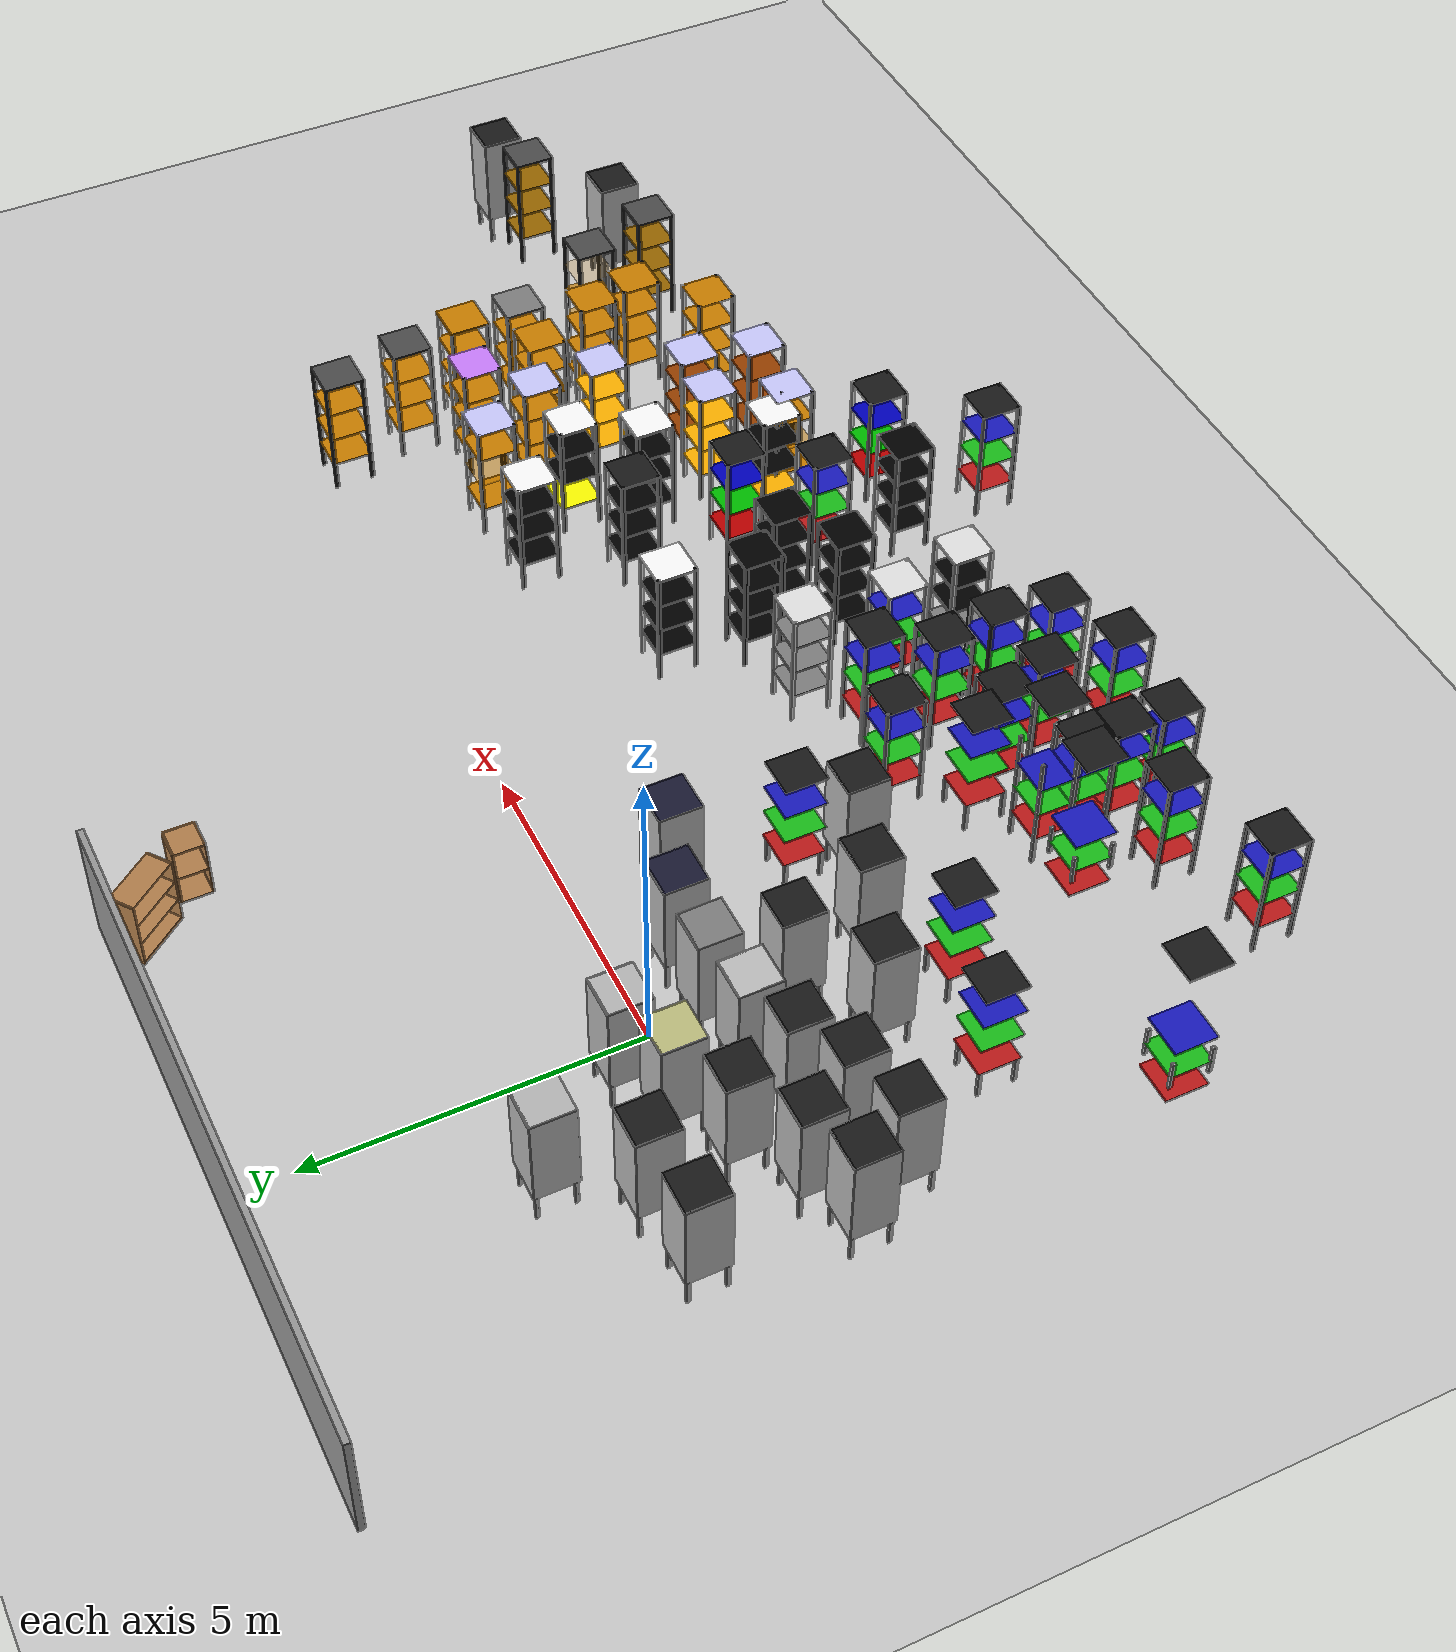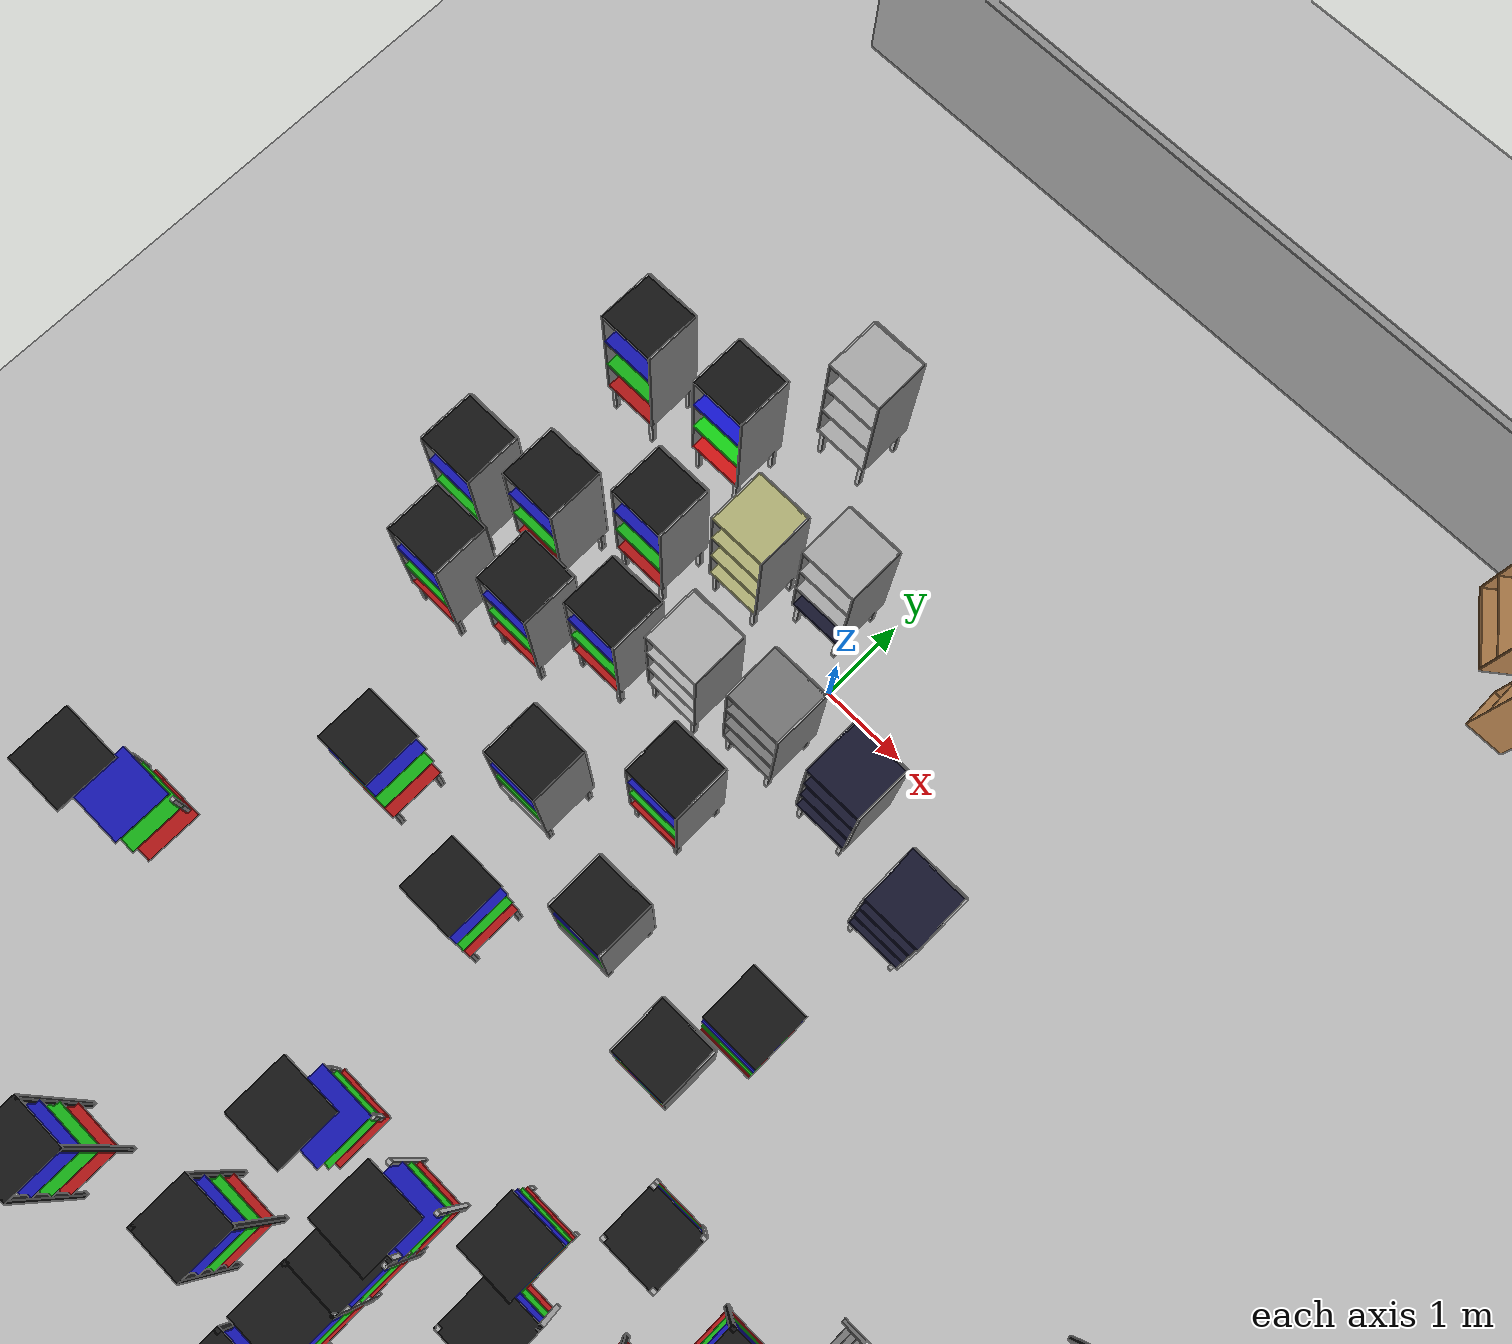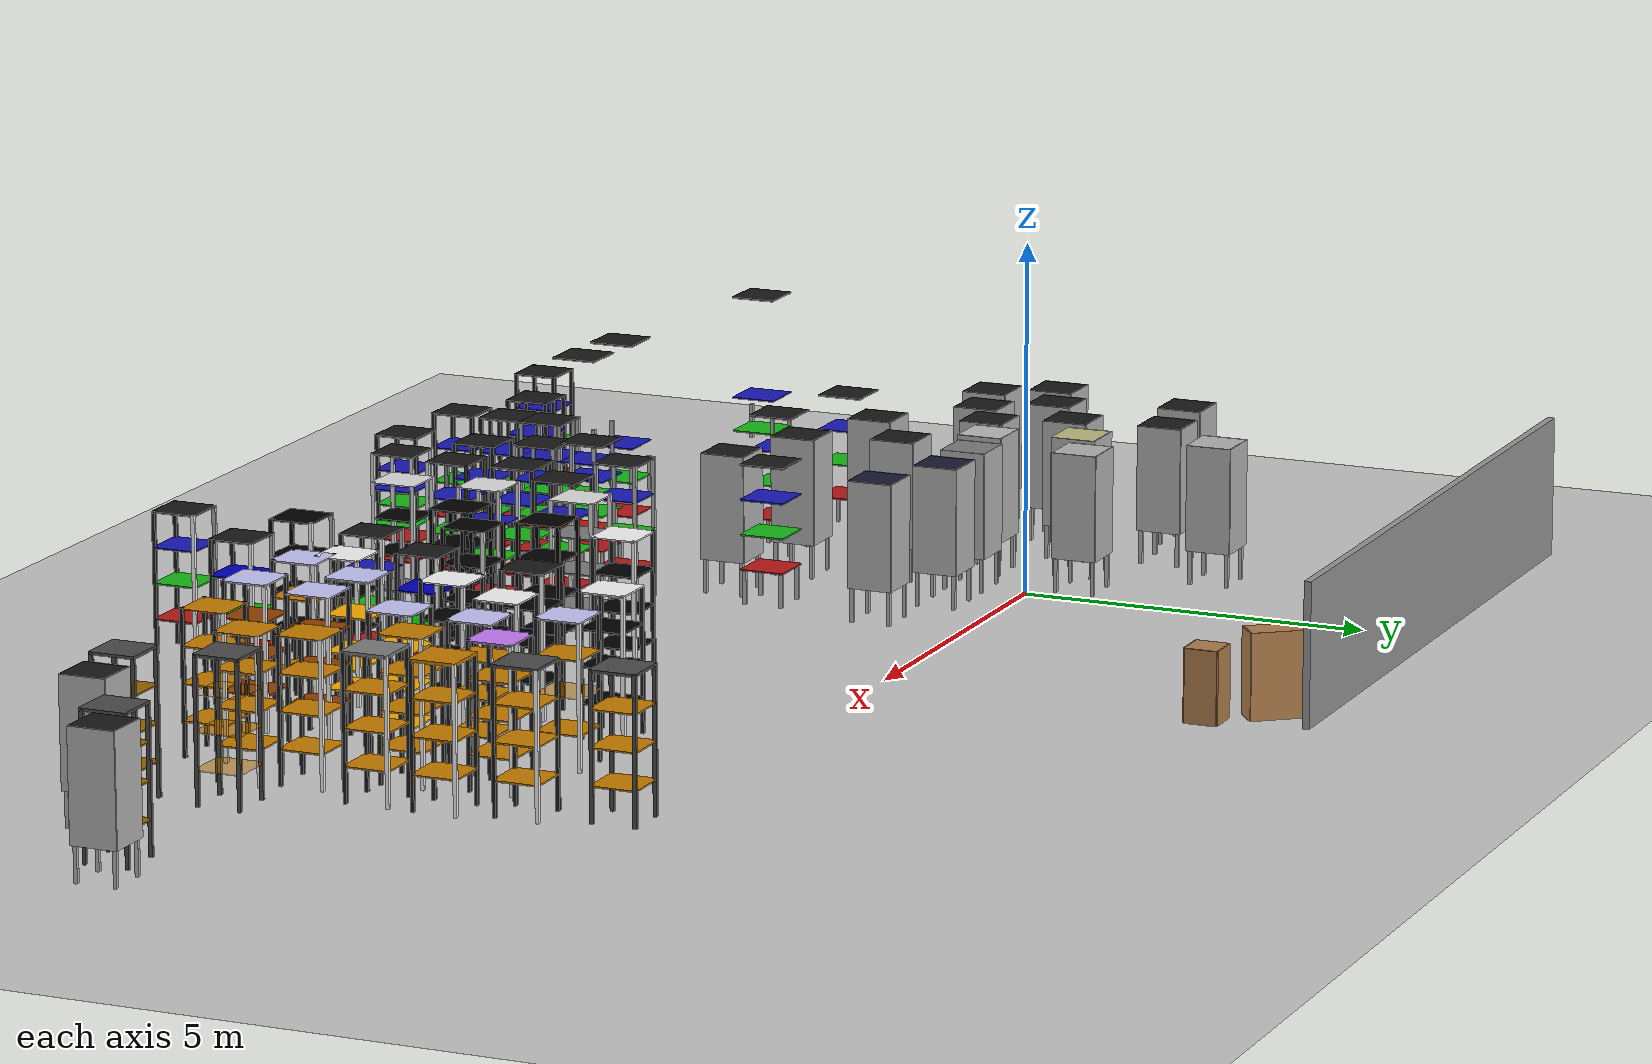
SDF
<sdf version="1.6">
 <world name="default">
  <light name="sun" type="directional">
   <pose>0 0 10 0 -0 0</pose>
   <diffuse>0.8 0.8 0.8 1</diffuse>
   <specular>0.2 0.2 0.2 1</specular>
   <attenuation>
    <range>1000</range>
    <constant>0.9</constant>
    <linear>0.01</linear>
    <quadratic>0.001</quadratic>
   </attenuation>
   <direction>-0.5 0.1 -0.9</direction>
  </light>
  <model name="ground_plane">
   <static>1</static>
   <link name="link">
    <collision name="collision">
     <geometry><plane><normal>0 0 1</normal><size>50 50</size></plane></geometry>
     <surface><friction><ode><mu>100</mu><mu2>50</mu2></ode></friction></surface>
    </collision>
    <visual name="visual">
     <cast_shadows>0</cast_shadows>
     <geometry><plane><normal>0 0 1</normal><size>100 100</size></plane></geometry>
     <material>
      <script><uri>file://media/materials/scripts/gazebo.material</uri><name>Gazebo/Grey</name></script>
     </material>
    </visual>
    <velocity_decay><linear>0</linear><angular>0</angular></velocity_decay>
   </link>
  </model>
  <physics name="default_physics" default="0" type="ode">
   <max_step_size>0.001</max_step_size>
   <real_time_factor>1</real_time_factor>
   <real_time_update_rate>1000</real_time_update_rate>
  </physics>
  <scene><ambient>0.4 0.4 0.4 1</ambient><background>0.7 0.7 0.7 1</background><shadows>0</shadows></scene>
  <model name="grey_wall_2">
   <static>1</static>
   <link name="link">
    <pose>0 6 1 0 -0 0</pose>
    <collision name="collision"><geometry><box><size>10 0.1 2</size></box></geometry></collision>
    <visual name="visual">
     <cast_shadows>0</cast_shadows>
     <geometry><box><size>10 0.1 2</size></box></geometry>
     <material>
      <script>
       <uri>model://grey_wall/materials/scripts</uri>
       <uri>model://grey_wall/materials/textures</uri>
       <name>vrc/grey_wall</name>
      </script>
     </material>
    </visual>
    <velocity_decay><linear>0</linear><angular>0</angular></velocity_decay>
   </link>
  </model>
  <spherical_coordinates>
   <surface_model>EARTH_WGS84</surface_model>
   <latitude_deg>0</latitude_deg>
   <longitude_deg>0</longitude_deg>
   <elevation>0</elevation>
   <heading_deg>0</heading_deg>
  </spherical_coordinates>
  <model name="bookshelf_2">
   <static>1</static>
   <link name="link">
    <inertial><mass>1</mass></inertial>
    <collision name="back">
     <pose>0 0.005 0.6 0 -0 0</pose>
     <geometry><box><size>0.9 0.01 1.2</size></box></geometry>
    </collision>
    <visual name="visual1">
     <pose>0 0.005 0.6 0 -0 0</pose>
     <geometry><box><size>0.9 0.01 1.2</size></box></geometry>
     <material>
      <script><uri>file://media/materials/scripts/gazebo.material</uri><name>Gazebo/Wood</name></script>
     </material>
    </visual>
    <collision name="left_side">
     <pose>0.45 -0.195 0.6 0 -0 0</pose>
     <geometry><box><size>0.02 0.4 1.2</size></box></geometry>
    </collision>
    <visual name="visual2">
     <pose>0.45 -0.195 0.6 0 -0 0</pose>
     <geometry><box><size>0.02 0.4 1.2</size></box></geometry>
     <material>
      <script><uri>file://media/materials/scripts/gazebo.material</uri><name>Gazebo/Wood</name></script>
     </material>
    </visual>
    <collision name="right_side">
     <pose>-0.45 -0.195 0.6 0 -0 0</pose>
     <geometry><box><size>0.02 0.4 1.2</size></box></geometry>
    </collision>
    <visual name="visual3">
     <pose>-0.45 -0.195 0.6 0 -0 0</pose>
     <geometry><box><size>0.02 0.4 1.2</size></box></geometry>
     <material>
      <script><uri>file://media/materials/scripts/gazebo.material</uri><name>Gazebo/Wood</name></script>
     </material>
    </visual>
    <collision name="bottom">
     <pose>0 -0.195 0.03 0 -0 0</pose>
     <geometry><box><size>0.88 0.4 0.06</size></box></geometry>
    </collision>
    <visual name="visual4">
     <pose>0 -0.195 0.03 0 -0 0</pose>
     <geometry><box><size>0.88 0.4 0.06</size></box></geometry>
     <material>
      <script><uri>file://media/materials/scripts/gazebo.material</uri><name>Gazebo/Wood</name></script>
     </material>
    </visual>
    <collision name="top">
     <pose>0 -0.195 1.19 0 -0 0</pose>
     <geometry><box><size>0.88 0.4 0.02</size></box></geometry>
    </collision>
    <visual name="visual5">
     <pose>0 -0.195 1.19 0 -0 0</pose>
     <geometry><box><size>0.88 0.4 0.02</size></box></geometry>
     <material>
      <script><uri>file://media/materials/scripts/gazebo.material</uri><name>Gazebo/Wood</name></script>
     </material>
    </visual>
    <collision name="low_shelf">
     <pose>0 -0.195 0.43 0 -0 0</pose>
     <geometry><box><size>0.88 0.4 0.02</size></box></geometry>
    </collision>
    <visual name="visual6">
     <pose>0 -0.195 0.43 0 -0 0</pose>
     <geometry><box><size>0.88 0.4 0.02</size></box></geometry>
     <material>
      <script><uri>file://media/materials/scripts/gazebo.material</uri><name>Gazebo/Wood</name></script>
     </material>
    </visual>
    <collision name="high_shelf">
     <pose>0 -0.195 0.8 0 -0 0</pose>
     <geometry><box><size>0.88 0.4 0.02</size></box></geometry>
    </collision>
    <visual name="visual7">
     <pose>0 -0.195 0.8 0 -0 0</pose>
     <geometry><box><size>0.88 0.4 0.02</size></box></geometry>
     <material>
      <script><uri>file://media/materials/scripts/gazebo.material</uri><name>Gazebo/Wood</name></script>
     </material>
    </visual>
    <velocity_decay><linear>0</linear><angular>0</angular></velocity_decay>
   </link>
   <pose>4.65383 5.55808 0 0 0 -0.917052</pose>
  </model>
  <model name="cabinet_1">
   <static>1</static>
   <link name="cabinet_bottom_plate">
    <inertial>
     <pose>0 0 -1 0 -0 0</pose>
     <inertia><ixx>2.05</ixx><ixy>0</ixy><ixz>0</ixz><iyy>2.05</iyy><iyz>0</iyz><izz>2.05</izz></inertia>
     <mass>25</mass>
    </inertial>
    <collision name="cabinet_bottom_plate_geom">
     <pose>0 0 0.01 0 -0 0</pose>
     <geometry><box><size>0.45 0.45 0.02</size></box></geometry>
    </collision>
    <visual name="cabinet_bottom_plate_geom_visual">
     <pose>0 0 0.01 0 -0 0</pose>
     <geometry><box><size>0.45 0.45 0.02</size></box></geometry>
     <material>
      <script><uri>file://media/materials/scripts/gazebo.material</uri><name>Gazebo/Wood</name></script>
     </material>
    </visual>
    <collision name="cabinet_bottom_plate_geom_cabinet_back_plate">
     <pose>0.235 0 0.51 0 -0 0</pose>
     <geometry><box><size>0.02 0.45 1.02</size></box></geometry>
    </collision>
    <visual name="cabinet_bottom_plate_geom_cabinet_back_plate_visual">
     <pose>0.235 0 0.51 0 -0 0</pose>
     <geometry><box><size>0.02 0.45 1.02</size></box></geometry>
     <material>
      <script><uri>file://media/materials/scripts/gazebo.material</uri><name>Gazebo/Wood</name></script>
     </material>
    </visual>
    <collision name="cabinet_bottom_plate_geom_cabinet_left_plate">
     <pose>0 0.235 0.51 0 -0 0</pose>
     <geometry><box><size>0.45 0.02 1.02</size></box></geometry>
    </collision>
    <visual name="cabinet_bottom_plate_geom_cabinet_left_plate_visual">
     <pose>0 0.235 0.51 0 -0 0</pose>
     <geometry><box><size>0.45 0.02 1.02</size></box></geometry>
     <material>
      <script><uri>file://media/materials/scripts/gazebo.material</uri><name>Gazebo/Wood</name></script>
     </material>
    </visual>
    <collision name="cabinet_bottom_plate_geom_cabinet_middle_plate">
     <pose>0 0 0.51 0 -0 0</pose>
     <geometry><box><size>0.45 0.45 0.02</size></box></geometry>
    </collision>
    <visual name="cabinet_bottom_plate_geom_cabinet_middle_plate_visual">
     <pose>0 0 0.51 0 -0 0</pose>
     <geometry><box><size>0.45 0.45 0.02</size></box></geometry>
     <material>
      <script><uri>file://media/materials/scripts/gazebo.material</uri><name>Gazebo/Wood</name></script>
     </material>
    </visual>
    <collision name="cabinet_bottom_plate_geom_cabinet_right_plate">
     <pose>0 -0.235 0.51 0 -0 0</pose>
     <geometry><box><size>0.45 0.02 1.02</size></box></geometry>
    </collision>
    <visual name="cabinet_bottom_plate_geom_cabinet_right_plate_visual">
     <pose>0 -0.235 0.51 0 -0 0</pose>
     <geometry><box><size>0.45 0.02 1.02</size></box></geometry>
     <material>
      <script><uri>file://media/materials/scripts/gazebo.material</uri><name>Gazebo/Wood</name></script>
     </material>
    </visual>
    <collision name="cabinet_bottom_plate_geom_cabinet_top_plate">
     <pose>0 0 1.01 0 -0 0</pose>
     <geometry><box><size>0.45 0.45 0.02</size></box></geometry>
    </collision>
    <visual name="cabinet_bottom_plate_geom_cabinet_top_plate_visual">
     <pose>0 0 1.01 0 -0 0</pose>
     <geometry><box><size>0.45 0.45 0.02</size></box></geometry>
     <material>
      <script><uri>file://media/materials/scripts/gazebo.material</uri><name>Gazebo/Wood</name></script>
     </material>
    </visual>
    <velocity_decay><linear>0</linear><angular>0</angular></velocity_decay>
   </link>
   <pose>5.10985 4.64944 0 0 -0 0</pose>
  </model>
  <gravity>0 0 -9.8</gravity>
  <magnetic_field>6e-06 2.3e-05 -4.2e-05</magnetic_field>
  <atmosphere type="adiabatic"/>
  <model name="warehouse_shelf">
   <static>1</static>
   <pose>-1.67621 2.19 0 0 -0 0</pose>
   <link name="main_block">
    <pose>0 0 1.255 0 -0 0</pose>
    <collision name="collision"><geometry><box><size>0.65 0.65 1.51</size></box></geometry></collision>
   </link>
   <link name="leg_1">
    <pose>0.275 0.275 0.25 0 -0 0</pose>
    <collision name="collision"><geometry><box><size>0.05 0.05 0.5</size></box></geometry></collision>
    <visual name="visual"><geometry><box><size>0.05 0.05 0.5</size></box></geometry></visual>
   </link>
   <link name="leg_2">
    <pose>-0.275 0.275 0.25 0 -0 0</pose>
    <collision name="collision"><geometry><box><size>0.05 0.05 0.5</size></box></geometry></collision>
    <visual name="visual"><geometry><box><size>0.05 0.05 0.5</size></box></geometry></visual>
   </link>
   <link name="leg_3">
    <pose>-0.275 -0.275 0.25 0 -0 0</pose>
    <collision name="collision"><geometry><box><size>0.05 0.05 0.5</size></box></geometry></collision>
    <visual name="visual"><geometry><box><size>0.05 0.05 0.5</size></box></geometry></visual>
   </link>
   <link name="leg_4">
    <pose>0.275 -0.275 0.25 0 -0 0</pose>
    <collision name="collision"><geometry><box><size>0.05 0.05 0.5</size></box></geometry></collision>
    <visual name="visual"><geometry><box><size>0.05 0.05 0.5</size></box></geometry></visual>
   </link>
   <link name="shelf_0">
    <pose>0 0 0.5 0 -0 0</pose>
    <visual name="visual"><geometry><box><size>0.648 0.648 0.02</size></box></geometry></visual>
   </link>
   <link name="shelf_1">
    <pose>0 0 1 0 -0 0</pose>
    <visual name="visual"><geometry><box><size>0.648 0.648 0.02</size></box></geometry></visual>
   </link>
   <link name="shelf_2">
    <pose>0 0 1.5 0 -0 0</pose>
    <visual name="visual"><geometry><box><size>0.648 0.648 0.02</size></box></geometry></visual>
   </link>
   <link name="shelf_top">
    <pose>0 0 2 0 -0 0</pose>
    <visual name="visual"><geometry><box><size>0.648 0.648 0.02</size></box></geometry></visual>
   </link>
   <link name="side_left">
    <pose>0.324 0 1.25 0 -0 0</pose>
    <visual name="visual"><geometry><box><size>0.02 0.65 1.52</size></box></geometry></visual>
   </link>
   <link name="side_right">
    <pose>-0.324 0 1.25 0 -0 0</pose>
    <visual name="visual"><geometry><box><size>0.02 0.65 1.52</size></box></geometry></visual>
   </link>
   <link name="side_back">
    <pose>0 0.324 1.25 0 -0 0</pose>
    <visual name="visual"><geometry><box><size>0.65 0.02 1.52</size></box></geometry></visual>
   </link>
  </model>
  <model name="warehouse_shelf_0">
   <static>1</static>
   <pose>-0.53273 0.621945 0 0 -0 0</pose>
   <link name="main_block">
    <pose>0 0 1.255 0 -0 0</pose>
    <collision name="collision"><geometry><box><size>0.65 0.65 1.51</size></box></geometry></collision>
   </link>
   <link name="leg_1">
    <pose>0.275 0.275 0.25 0 -0 0</pose>
    <collision name="collision"><geometry><box><size>0.05 0.05 0.5</size></box></geometry></collision>
    <visual name="visual"><geometry><box><size>0.05 0.05 0.5</size></box></geometry></visual>
   </link>
   <link name="leg_2">
    <pose>-0.275 0.275 0.25 0 -0 0</pose>
    <collision name="collision"><geometry><box><size>0.05 0.05 0.5</size></box></geometry></collision>
    <visual name="visual"><geometry><box><size>0.05 0.05 0.5</size></box></geometry></visual>
   </link>
   <link name="leg_3">
    <pose>-0.275 -0.275 0.25 0 -0 0</pose>
    <collision name="collision"><geometry><box><size>0.05 0.05 0.5</size></box></geometry></collision>
    <visual name="visual"><geometry><box><size>0.05 0.05 0.5</size></box></geometry></visual>
   </link>
   <link name="leg_4">
    <pose>0.275 -0.275 0.25 0 -0 0</pose>
    <collision name="collision"><geometry><box><size>0.05 0.05 0.5</size></box></geometry></collision>
    <visual name="visual"><geometry><box><size>0.05 0.05 0.5</size></box></geometry></visual>
   </link>
   <link name="shelf_0">
    <pose>0 0 0.5 0 -0 0</pose>
    <visual name="visual">
     <geometry><box><size>0.648 0.648 0.02</size></box></geometry>
     <material>
      <ambient>0.1 0.1 0.1 1</ambient>
      <diffuse>0.1 0.1 0.2 1</diffuse>
      <specular>0 0 0 0</specular>
      <emissive>0 0 0 1</emissive>
     </material>
    </visual>
   </link>
   <link name="shelf_1">
    <pose>0 0 1 0 -0 0</pose>
    <visual name="visual"><geometry><box><size>0.648 0.648 0.02</size></box></geometry></visual>
   </link>
   <link name="shelf_2">
    <pose>0 0 1.5 0 -0 0</pose>
    <visual name="visual"><geometry><box><size>0.648 0.648 0.02</size></box></geometry></visual>
   </link>
   <link name="shelf_top">
    <pose>0 0 2 0 -0 0</pose>
    <visual name="visual"><geometry><box><size>0.648 0.648 0.02</size></box></geometry></visual>
   </link>
   <link name="side_left">
    <pose>0.324 0 1.25 0 -0 0</pose>
    <visual name="visual"><geometry><box><size>0.02 0.65 1.52</size></box></geometry></visual>
   </link>
   <link name="side_right">
    <pose>-0.324 0 1.25 0 -0 0</pose>
    <visual name="visual"><geometry><box><size>0.02 0.65 1.52</size></box></geometry></visual>
   </link>
   <link name="side_back">
    <pose>0 0.324 1.25 0 -0 0</pose>
    <visual name="visual"><geometry><box><size>0.65 0.02 1.52</size></box></geometry></visual>
   </link>
  </model>
  <model name="warehouse_shelf_1">
   <static>1</static>
   <pose>0.940142 -0.856452 0 0 -0 0</pose>
   <link name="main_block">
    <pose>0 0 1.255 0 -0 0</pose>
    <collision name="collision"><geometry><box><size>0.65 0.65 1.51</size></box></geometry></collision>
   </link>
   <link name="leg_1">
    <pose>0.275 0.275 0.25 0 -0 0</pose>
    <collision name="collision"><geometry><box><size>0.05 0.05 0.5</size></box></geometry></collision>
    <visual name="visual"><geometry><box><size>0.05 0.05 0.5</size></box></geometry></visual>
   </link>
   <link name="leg_2">
    <pose>-0.275 0.275 0.25 0 -0 0</pose>
    <collision name="collision"><geometry><box><size>0.05 0.05 0.5</size></box></geometry></collision>
    <visual name="visual"><geometry><box><size>0.05 0.05 0.5</size></box></geometry></visual>
   </link>
   <link name="leg_3">
    <pose>-0.275 -0.275 0.25 0 -0 0</pose>
    <collision name="collision"><geometry><box><size>0.05 0.05 0.5</size></box></geometry></collision>
    <visual name="visual"><geometry><box><size>0.05 0.05 0.5</size></box></geometry></visual>
   </link>
   <link name="leg_4">
    <pose>0.275 -0.275 0.25 0 -0 0</pose>
    <collision name="collision"><geometry><box><size>0.05 0.05 0.5</size></box></geometry></collision>
    <visual name="visual"><geometry><box><size>0.05 0.05 0.5</size></box></geometry></visual>
   </link>
   <link name="shelf_0">
    <pose>0 0 0.5 0 -0 0</pose>
    <visual name="visual">
     <geometry><box><size>0.648 0.648 0.02</size></box></geometry>
     <material>
      <ambient>0.1 0.1 0.1 1</ambient>
      <diffuse>0.1 0.1 0.2 1</diffuse>
      <specular>0 0 0 0</specular>
      <emissive>0 0 0 1</emissive>
     </material>
    </visual>
   </link>
   <link name="shelf_1">
    <pose>0 0 1 0 -0 0</pose>
    <visual name="visual">
     <geometry><box><size>0.648 0.648 0.02</size></box></geometry>
     <material>
      <ambient>0.1 0.1 0.1 1</ambient>
      <diffuse>0.1 0.1 0.2 1</diffuse>
      <specular>0 0 0 0</specular>
      <emissive>0 0 0 1</emissive>
     </material>
    </visual>
   </link>
   <link name="shelf_2">
    <pose>0 0 1.5 0 -0 0</pose>
    <visual name="visual">
     <geometry><box><size>0.648 0.648 0.02</size></box></geometry>
     <material>
      <ambient>0.1 0.1 0.1 1</ambient>
      <diffuse>0.1 0.1 0.2 1</diffuse>
      <specular>0 0 0 0</specular>
      <emissive>0 0 0 1</emissive>
     </material>
    </visual>
   </link>
   <link name="shelf_top">
    <pose>0 0 2 0 -0 0</pose>
    <visual name="visual">
     <geometry><box><size>0.648 0.648 0.02</size></box></geometry>
     <material>
      <ambient>0.1 0.1 0.1 1</ambient>
      <diffuse>0.1 0.1 0.2 1</diffuse>
      <specular>0 0 0 0</specular>
      <emissive>0 0 0 1</emissive>
     </material>
    </visual>
   </link>
   <link name="side_left">
    <pose>0.324 0 1.25 0 -0 0</pose>
    <visual name="visual"><geometry><box><size>0.02 0.65 1.52</size></box></geometry></visual>
   </link>
   <link name="side_right">
    <pose>-0.324 0 1.25 0 -0 0</pose>
    <visual name="visual"><geometry><box><size>0.02 0.65 1.52</size></box></geometry></visual>
   </link>
   <link name="side_back">
    <pose>0 0.324 1.25 0 -0 0</pose>
    <visual name="visual"><geometry><box><size>0.65 0.02 1.52</size></box></geometry></visual>
   </link>
  </model>
  <model name="warehouse_shelf_2">
   <static>1</static>
   <pose>2.10777 -1.33908 0 0 -0 0</pose>
   <link name="main_block">
    <pose>0 0 1.255 0 -0 0</pose>
    <collision name="collision"><geometry><box><size>0.65 0.65 1.51</size></box></geometry></collision>
   </link>
   <link name="leg_1">
    <pose>0.275 0.275 0.25 0 -0 0</pose>
    <collision name="collision"><geometry><box><size>0.05 0.05 0.5</size></box></geometry></collision>
    <visual name="visual"><geometry><box><size>0.05 0.05 0.5</size></box></geometry></visual>
   </link>
   <link name="leg_2">
    <pose>-0.275 0.275 0.25 0 -0 0</pose>
    <collision name="collision"><geometry><box><size>0.05 0.05 0.5</size></box></geometry></collision>
    <visual name="visual"><geometry><box><size>0.05 0.05 0.5</size></box></geometry></visual>
   </link>
   <link name="leg_3">
    <pose>-0.275 -0.275 0.25 0 -0 0</pose>
    <collision name="collision"><geometry><box><size>0.05 0.05 0.5</size></box></geometry></collision>
    <visual name="visual"><geometry><box><size>0.05 0.05 0.5</size></box></geometry></visual>
   </link>
   <link name="leg_4">
    <pose>0.275 -0.275 0.25 0 -0 0</pose>
    <collision name="collision"><geometry><box><size>0.05 0.05 0.5</size></box></geometry></collision>
    <visual name="visual"><geometry><box><size>0.05 0.05 0.5</size></box></geometry></visual>
   </link>
   <link name="shelf_0">
    <pose>0 0 0.5 0 -0 0</pose>
    <visual name="visual">
     <geometry><box><size>0.648 0.648 0.02</size></box></geometry>
     <material>
      <ambient>0.1 0.1 0.1 1</ambient>
      <diffuse>0.1 0.1 0.2 1</diffuse>
      <specular>0 0 0 0</specular>
      <emissive>0 0 0 1</emissive>
     </material>
    </visual>
   </link>
   <link name="shelf_1">
    <pose>0 0 1 0 -0 0</pose>
    <visual name="visual">
     <geometry><box><size>0.648 0.648 0.02</size></box></geometry>
     <material>
      <ambient>0.9 0.1 0.1 1</ambient>
      <diffuse>0.1 0.1 0.2 1</diffuse>
      <specular>0 0 0 0</specular>
      <emissive>0 0 0 1</emissive>
     </material>
    </visual>
   </link>
   <link name="shelf_2">
    <pose>0 0 1.5 0 -0 0</pose>
    <visual name="visual">
     <geometry><box><size>0.648 0.648 0.02</size></box></geometry>
     <material>
      <ambient>0.9 0.9 0.1 1</ambient>
      <diffuse>0.1 0.1 0.2 1</diffuse>
      <specular>0 0 0 0</specular>
      <emissive>0 0 0 1</emissive>
     </material>
    </visual>
   </link>
   <link name="shelf_top">
    <pose>0 0 2 0 -0 0</pose>
    <visual name="visual">
     <geometry><box><size>0.648 0.648 0.02</size></box></geometry>
     <material>
      <ambient>0.1 0.1 0.1 1</ambient>
      <diffuse>0.1 0.1 0.2 1</diffuse>
      <specular>0 0 0 0</specular>
      <emissive>0 0 0 1</emissive>
     </material>
    </visual>
   </link>
   <link name="side_left">
    <pose>0.324 0 1.25 0 -0 0</pose>
    <visual name="visual"><geometry><box><size>0.02 0.65 1.52</size></box></geometry></visual>
   </link>
   <link name="side_right">
    <pose>-0.324 0 1.25 0 -0 0</pose>
    <visual name="visual"><geometry><box><size>0.02 0.65 1.52</size></box></geometry></visual>
   </link>
   <link name="side_back">
    <pose>0 0.324 1.25 0 -0 0</pose>
    <visual name="visual"><geometry><box><size>0.65 0.02 1.52</size></box></geometry></visual>
   </link>
  </model>
  <model name="warehouse_shelf_3">
   <static>1</static>
   <pose>-2.48312 1.13483 0 0 -0 0</pose>
   <link name="main_block">
    <pose>0 0 1.255 0 -0 0</pose>
    <collision name="collision"><geometry><box><size>0.65 0.65 1.51</size></box></geometry></collision>
   </link>
   <link name="leg_1">
    <pose>0.275 0.275 0.25 0 -0 0</pose>
    <collision name="collision"><geometry><box><size>0.05 0.05 0.5</size></box></geometry></collision>
    <visual name="visual"><geometry><box><size>0.05 0.05 0.5</size></box></geometry></visual>
   </link>
   <link name="leg_2">
    <pose>-0.275 0.275 0.25 0 -0 0</pose>
    <collision name="collision"><geometry><box><size>0.05 0.05 0.5</size></box></geometry></collision>
    <visual name="visual"><geometry><box><size>0.05 0.05 0.5</size></box></geometry></visual>
   </link>
   <link name="leg_3">
    <pose>-0.275 -0.275 0.25 0 -0 0</pose>
    <collision name="collision"><geometry><box><size>0.05 0.05 0.5</size></box></geometry></collision>
    <visual name="visual"><geometry><box><size>0.05 0.05 0.5</size></box></geometry></visual>
   </link>
   <link name="leg_4">
    <pose>0.275 -0.275 0.25 0 -0 0</pose>
    <collision name="collision"><geometry><box><size>0.05 0.05 0.5</size></box></geometry></collision>
    <visual name="visual"><geometry><box><size>0.05 0.05 0.5</size></box></geometry></visual>
   </link>
   <link name="shelf_0">
    <pose>0 0 0.5 0 -0 0</pose>
    <visual name="visual">
     <geometry><box><size>0.648 0.648 0.02</size></box></geometry>
     <material>
      <ambient>0.9 0.1 0.1 1</ambient>
      <diffuse>0.9 0.1 0.1 1</diffuse>
      <specular>0 0 0 0</specular>
      <emissive>0 0 0 1</emissive>
     </material>
    </visual>
   </link>
   <link name="shelf_1">
    <pose>0 0 1 0 -0 0</pose>
    <visual name="visual">
     <geometry><box><size>0.648 0.648 0.02</size></box></geometry>
     <material>
      <ambient>0.1 0.9 0.1 1</ambient>
      <diffuse>0.1 0.9 0.1 1</diffuse>
      <specular>0 0 0 0</specular>
      <emissive>0 0 0 1</emissive>
     </material>
    </visual>
   </link>
   <link name="shelf_2">
    <pose>0 0 1.5 0 -0 0</pose>
    <visual name="visual">
     <geometry><box><size>0.648 0.648 0.02</size></box></geometry>
     <material>
      <ambient>0.1 0.1 0.9 1</ambient>
      <diffuse>0.1 0.1 0.9 1</diffuse>
      <specular>0 0 0 0</specular>
      <emissive>0 0 0 1</emissive>
     </material>
    </visual>
   </link>
   <link name="shelf_top">
    <pose>0 0 2 0 -0 0</pose>
    <visual name="visual">
     <geometry><box><size>0.648 0.648 0.02</size></box></geometry>
     <material>
      <ambient>0.1 0.1 0.1 1</ambient>
      <diffuse>0.1 0.1 0.1 1</diffuse>
      <specular>0 0 0 0</specular>
      <emissive>0 0 0 1</emissive>
     </material>
    </visual>
   </link>
   <link name="side_left">
    <pose>0.324 0 1.25 0 -0 0</pose>
    <visual name="visual"><geometry><box><size>0.02 0.65 1.52</size></box></geometry></visual>
   </link>
   <link name="side_right">
    <pose>-0.324 0 1.25 0 -0 0</pose>
    <visual name="visual"><geometry><box><size>0.02 0.65 1.52</size></box></geometry></visual>
   </link>
   <link name="side_back">
    <pose>0 0.324 1.25 0 -0 0</pose>
    <visual name="visual"><geometry><box><size>0.65 0.02 1.52</size></box></geometry></visual>
   </link>
  </model>
  <model name="warehouse_shelf_4">
   <static>1</static>
   <pose>-0.069342 -0.862017 0 0 -0 0</pose>
   <link name="main_block">
    <pose>0 0 1.255 0 -0 0</pose>
    <collision name="collision"><geometry><box><size>0.65 0.65 1.51</size></box></geometry></collision>
   </link>
   <link name="leg_1">
    <pose>0.275 0.275 0.25 0 -0 0</pose>
    <collision name="collision"><geometry><box><size>0.05 0.05 0.5</size></box></geometry></collision>
    <visual name="visual"><geometry><box><size>0.05 0.05 0.5</size></box></geometry></visual>
   </link>
   <link name="leg_2">
    <pose>-0.275 0.275 0.25 0 -0 0</pose>
    <collision name="collision"><geometry><box><size>0.05 0.05 0.5</size></box></geometry></collision>
    <visual name="visual"><geometry><box><size>0.05 0.05 0.5</size></box></geometry></visual>
   </link>
   <link name="leg_3">
    <pose>-0.275 -0.275 0.25 0 -0 0</pose>
    <collision name="collision"><geometry><box><size>0.05 0.05 0.5</size></box></geometry></collision>
    <visual name="visual"><geometry><box><size>0.05 0.05 0.5</size></box></geometry></visual>
   </link>
   <link name="leg_4">
    <pose>0.275 -0.275 0.25 0 -0 0</pose>
    <collision name="collision"><geometry><box><size>0.05 0.05 0.5</size></box></geometry></collision>
    <visual name="visual"><geometry><box><size>0.05 0.05 0.5</size></box></geometry></visual>
   </link>
   <link name="shelf_0">
    <pose>0 0 0.5 0 -0 0</pose>
    <visual name="visual">
     <geometry><box><size>0.648 0.648 0.02</size></box></geometry>
     <material>
      <ambient>0.9 0.1 0.1 1</ambient>
      <diffuse>0.5 0.5 0.5 1</diffuse>
      <specular>0 0 0 0</specular>
      <emissive>0 0 0 1</emissive>
     </material>
    </visual>
   </link>
   <link name="shelf_1">
    <pose>0 0 1 0 -0 0</pose>
    <visual name="visual">
     <geometry><box><size>0.648 0.648 0.02</size></box></geometry>
     <material>
      <ambient>0.1 0.9 0.1 1</ambient>
      <diffuse>0.5 0.5 0.5 1</diffuse>
      <specular>0 0 0 0</specular>
      <emissive>0 0 0 1</emissive>
     </material>
    </visual>
   </link>
   <link name="shelf_2">
    <pose>0 0 1.5 0 -0 0</pose>
    <visual name="visual">
     <geometry><box><size>0.648 0.648 0.02</size></box></geometry>
     <material>
      <ambient>0.1 0.1 0.9 1</ambient>
      <diffuse>0.5 0.5 0.5 1</diffuse>
      <specular>0 0 0 0</specular>
      <emissive>0 0 0 1</emissive>
     </material>
    </visual>
   </link>
   <link name="shelf_top">
    <pose>0 0 2 0 -0 0</pose>
    <visual name="visual">
     <geometry><box><size>0.648 0.648 0.02</size></box></geometry>
     <material>
      <ambient>0.1 0.1 0.1 1</ambient>
      <diffuse>0.5 0.5 0.5 1</diffuse>
      <specular>0 0 0 0</specular>
      <emissive>0 0 0 1</emissive>
     </material>
    </visual>
   </link>
   <link name="side_left">
    <pose>0.324 0 1.25 0 -0 0</pose>
    <visual name="visual"><geometry><box><size>0.02 0.65 1.52</size></box></geometry></visual>
   </link>
   <link name="side_right">
    <pose>-0.324 0 1.25 0 -0 0</pose>
    <visual name="visual"><geometry><box><size>0.02 0.65 1.52</size></box></geometry></visual>
   </link>
   <link name="side_back">
    <pose>0 0.324 1.25 0 -0 0</pose>
    <visual name="visual"><geometry><box><size>0.65 0.02 1.52</size></box></geometry></visual>
   </link>
  </model>
  <model name="warehouse_shelf_5">
   <static>1</static>
   <pose>-1.37464 0.269454 0 0 -0 0</pose>
   <link name="main_block">
    <pose>0 0 1.255 0 -0 0</pose>
    <collision name="collision"><geometry><box><size>0.65 0.65 1.51</size></box></geometry></collision>
   </link>
   <link name="leg_1">
    <pose>0.275 0.275 0.25 0 -0 0</pose>
    <collision name="collision"><geometry><box><size>0.05 0.05 0.5</size></box></geometry></collision>
    <visual name="visual"><geometry><box><size>0.05 0.05 0.5</size></box></geometry></visual>
   </link>
   <link name="leg_2">
    <pose>-0.275 0.275 0.25 0 -0 0</pose>
    <collision name="collision"><geometry><box><size>0.05 0.05 0.5</size></box></geometry></collision>
    <visual name="visual"><geometry><box><size>0.05 0.05 0.5</size></box></geometry></visual>
   </link>
   <link name="leg_3">
    <pose>-0.275 -0.275 0.25 0 -0 0</pose>
    <collision name="collision"><geometry><box><size>0.05 0.05 0.5</size></box></geometry></collision>
    <visual name="visual"><geometry><box><size>0.05 0.05 0.5</size></box></geometry></visual>
   </link>
   <link name="leg_4">
    <pose>0.275 -0.275 0.25 0 -0 0</pose>
    <collision name="collision"><geometry><box><size>0.05 0.05 0.5</size></box></geometry></collision>
    <visual name="visual"><geometry><box><size>0.05 0.05 0.5</size></box></geometry></visual>
   </link>
   <link name="shelf_0">
    <pose>0 0 0.5 0 -0 0</pose>
    <visual name="visual">
     <geometry><box><size>0.648 0.648 0.02</size></box></geometry>
     <material>
      <ambient>0.9 0.1 0.1 1</ambient>
      <diffuse>0.75 0.75 0.5 1</diffuse>
      <specular>0 0 0 0</specular>
      <emissive>0 0 0 1</emissive>
     </material>
    </visual>
   </link>
   <link name="shelf_1">
    <pose>0 0 1 0 -0 0</pose>
    <visual name="visual">
     <geometry><box><size>0.648 0.648 0.02</size></box></geometry>
     <material>
      <ambient>0.1 0.9 0.1 1</ambient>
      <diffuse>0.75 0.75 0.5 1</diffuse>
      <specular>0 0 0 0</specular>
      <emissive>0 0 0 1</emissive>
     </material>
    </visual>
   </link>
   <link name="shelf_2">
    <pose>0 0 1.5 0 -0 0</pose>
    <visual name="visual">
     <geometry><box><size>0.648 0.648 0.02</size></box></geometry>
     <material>
      <ambient>0.1 0.1 0.9 1</ambient>
      <diffuse>0.75 0.75 0.5 1</diffuse>
      <specular>0 0 0 0</specular>
      <emissive>0 0 0 1</emissive>
     </material>
    </visual>
   </link>
   <link name="shelf_top">
    <pose>0 0 2 0 -0 0</pose>
    <visual name="visual">
     <geometry><box><size>0.648 0.648 0.02</size></box></geometry>
     <material>
      <ambient>0.1 0.1 0.1 1</ambient>
      <diffuse>0.75 0.75 0.5 1</diffuse>
      <specular>0 0 0 0</specular>
      <emissive>0 0 0 1</emissive>
     </material>
    </visual>
   </link>
   <link name="side_left">
    <pose>0.324 0 1.25 0 -0 0</pose>
    <visual name="visual"><geometry><box><size>0.02 0.65 1.52</size></box></geometry></visual>
   </link>
   <link name="side_right">
    <pose>-0.324 0 1.25 0 -0 0</pose>
    <visual name="visual"><geometry><box><size>0.02 0.65 1.52</size></box></geometry></visual>
   </link>
   <link name="side_back">
    <pose>0 0.324 1.25 0 -0 0</pose>
    <visual name="visual"><geometry><box><size>0.65 0.02 1.52</size></box></geometry></visual>
   </link>
  </model>
  <model name="warehouse_shelf_6">
   <static>1</static>
   <pose>-0.995623 -0.99425 0 0 -0 0</pose>
   <link name="main_block">
    <pose>0 0 1.255 0 -0 0</pose>
    <collision name="collision"><geometry><box><size>0.65 0.65 1.51</size></box></geometry></collision>
   </link>
   <link name="leg_1">
    <pose>0.275 0.275 0.25 0 -0 0</pose>
    <collision name="collision"><geometry><box><size>0.05 0.05 0.5</size></box></geometry></collision>
    <visual name="visual"><geometry><box><size>0.05 0.05 0.5</size></box></geometry></visual>
   </link>
   <link name="leg_2">
    <pose>-0.275 0.275 0.25 0 -0 0</pose>
    <collision name="collision"><geometry><box><size>0.05 0.05 0.5</size></box></geometry></collision>
    <visual name="visual"><geometry><box><size>0.05 0.05 0.5</size></box></geometry></visual>
   </link>
   <link name="leg_3">
    <pose>-0.275 -0.275 0.25 0 -0 0</pose>
    <collision name="collision"><geometry><box><size>0.05 0.05 0.5</size></box></geometry></collision>
    <visual name="visual"><geometry><box><size>0.05 0.05 0.5</size></box></geometry></visual>
   </link>
   <link name="leg_4">
    <pose>0.275 -0.275 0.25 0 -0 0</pose>
    <collision name="collision"><geometry><box><size>0.05 0.05 0.5</size></box></geometry></collision>
    <visual name="visual"><geometry><box><size>0.05 0.05 0.5</size></box></geometry></visual>
   </link>
   <link name="shelf_0">
    <pose>0 0 0.5 0 -0 0</pose>
    <visual name="visual">
     <geometry><box><size>0.648 0.648 0.02</size></box></geometry>
     <material>
      <ambient>0.9 0.1 0.1 1</ambient>
      <diffuse>0.75 0.75 0.75 1</diffuse>
      <specular>0 0 0 0</specular>
      <emissive>0 0 0 1</emissive>
     </material>
    </visual>
   </link>
   <link name="shelf_1">
    <pose>0 0 1 0 -0 0</pose>
    <visual name="visual">
     <geometry><box><size>0.648 0.648 0.02</size></box></geometry>
     <material>
      <ambient>0.1 0.9 0.1 1</ambient>
      <diffuse>0.75 0.75 0.75 1</diffuse>
      <specular>0 0 0 0</specular>
      <emissive>0 0 0 1</emissive>
     </material>
    </visual>
   </link>
   <link name="shelf_2">
    <pose>0 0 1.5 0 -0 0</pose>
    <visual name="visual">
     <geometry><box><size>0.648 0.648 0.02</size></box></geometry>
     <material>
      <ambient>0.1 0.1 0.9 1</ambient>
      <diffuse>0.75 0.75 0.75 1</diffuse>
      <specular>0 0 0 0</specular>
      <emissive>0 0 0 1</emissive>
     </material>
    </visual>
   </link>
   <link name="shelf_top">
    <pose>0 0 2 0 -0 0</pose>
    <visual name="visual">
     <geometry><box><size>0.648 0.648 0.02</size></box></geometry>
     <material>
      <ambient>0.1 0.1 0.1 1</ambient>
      <diffuse>0.75 0.75 0.75 1</diffuse>
      <specular>0 0 0 0</specular>
      <emissive>0 0 0 1</emissive>
     </material>
    </visual>
   </link>
   <link name="side_left">
    <pose>0.324 0 1.25 0 -0 0</pose>
    <visual name="visual"><geometry><box><size>0.02 0.65 1.52</size></box></geometry></visual>
   </link>
   <link name="side_right">
    <pose>-0.324 0 1.25 0 -0 0</pose>
    <visual name="visual"><geometry><box><size>0.02 0.65 1.52</size></box></geometry></visual>
   </link>
   <link name="side_back">
    <pose>0 0.324 1.25 0 -0 0</pose>
    <visual name="visual"><geometry><box><size>0.65 0.02 1.52</size></box></geometry></visual>
   </link>
  </model>
  <model name="warehouse_shelf_7">
   <static>1</static>
   <pose>-2.24187 -0.20564 0 0 -0 0</pose>
   <link name="main_block">
    <pose>0 0 1.255 0 -0 0</pose>
    <collision name="collision"><geometry><box><size>0.65 0.65 1.51</size></box></geometry></collision>
   </link>
   <link name="leg_1">
    <pose>0.275 0.275 0.25 0 -0 0</pose>
    <collision name="collision"><geometry><box><size>0.05 0.05 0.5</size></box></geometry></collision>
    <visual name="visual"><geometry><box><size>0.05 0.05 0.5</size></box></geometry></visual>
   </link>
   <link name="leg_2">
    <pose>-0.275 0.275 0.25 0 -0 0</pose>
    <collision name="collision"><geometry><box><size>0.05 0.05 0.5</size></box></geometry></collision>
    <visual name="visual"><geometry><box><size>0.05 0.05 0.5</size></box></geometry></visual>
   </link>
   <link name="leg_3">
    <pose>-0.275 -0.275 0.25 0 -0 0</pose>
    <collision name="collision"><geometry><box><size>0.05 0.05 0.5</size></box></geometry></collision>
    <visual name="visual"><geometry><box><size>0.05 0.05 0.5</size></box></geometry></visual>
   </link>
   <link name="leg_4">
    <pose>0.275 -0.275 0.25 0 -0 0</pose>
    <collision name="collision"><geometry><box><size>0.05 0.05 0.5</size></box></geometry></collision>
    <visual name="visual"><geometry><box><size>0.05 0.05 0.5</size></box></geometry></visual>
   </link>
   <link name="shelf_0">
    <pose>0 0 0.5 0 -0 0</pose>
    <visual name="visual">
     <geometry><box><size>0.648 0.648 0.02</size></box></geometry>
     <material>
      <ambient>0.9 0.1 0.1 1</ambient>
      <diffuse>0.75 0.1 0.1 1</diffuse>
      <specular>0 0 0 0</specular>
      <emissive>0 0 0 1</emissive>
     </material>
    </visual>
   </link>
   <link name="shelf_1">
    <pose>0 0 1 0 -0 0</pose>
    <visual name="visual">
     <geometry><box><size>0.648 0.648 0.02</size></box></geometry>
     <material>
      <ambient>0.1 0.9 0.1 1</ambient>
      <diffuse>0.1 0.75 0.1 1</diffuse>
      <specular>0 0 0 0</specular>
      <emissive>0 0 0 1</emissive>
     </material>
    </visual>
   </link>
   <link name="shelf_2">
    <pose>0 0 1.5 0 -0 0</pose>
    <visual name="visual">
     <geometry><box><size>0.648 0.648 0.02</size></box></geometry>
     <material>
      <ambient>0.1 0.1 0.9 1</ambient>
      <diffuse>0.1 0.1 0.75 1</diffuse>
      <specular>0 0 0 0</specular>
      <emissive>0 0 0 1</emissive>
     </material>
    </visual>
   </link>
   <link name="shelf_top">
    <pose>0 0 2 0 -0 0</pose>
    <visual name="visual">
     <geometry><box><size>0.648 0.648 0.02</size></box></geometry>
     <material>
      <ambient>0.1 0.1 0.1 1</ambient>
      <diffuse>0.1 0.1 0.1 1</diffuse>
      <specular>0 0 0 0</specular>
      <emissive>0 0 0 1</emissive>
     </material>
    </visual>
   </link>
   <link name="side_left">
    <pose>0.324 0 1.25 0 -0 0</pose>
    <visual name="visual"><geometry><box><size>0.02 0.65 1.52</size></box></geometry></visual>
   </link>
   <link name="side_right">
    <pose>-0.324 0 1.25 0 -0 0</pose>
    <visual name="visual"><geometry><box><size>0.02 0.65 1.52</size></box></geometry></visual>
   </link>
   <link name="side_back">
    <pose>0 0.324 1.25 0 -0 0</pose>
    <visual name="visual"><geometry><box><size>0.65 0.02 1.52</size></box></geometry></visual>
   </link>
  </model>
  <model name="warehouse_shelf_9">
   <static>1</static>
   <pose>-3.59907 1.00035 0 0 -0 0</pose>
   <link name="main_block">
    <pose>0 0 1.255 0 -0 0</pose>
    <collision name="collision"><geometry><box><size>0.65 0.65 1.51</size></box></geometry></collision>
   </link>
   <link name="leg_1">
    <pose>0.275 0.275 0.25 0 -0 0</pose>
    <collision name="collision"><geometry><box><size>0.05 0.05 0.5</size></box></geometry></collision>
    <visual name="visual"><geometry><box><size>0.05 0.05 0.5</size></box></geometry></visual>
   </link>
   <link name="leg_2">
    <pose>-0.275 0.275 0.25 0 -0 0</pose>
    <collision name="collision"><geometry><box><size>0.05 0.05 0.5</size></box></geometry></collision>
    <visual name="visual"><geometry><box><size>0.05 0.05 0.5</size></box></geometry></visual>
   </link>
   <link name="leg_3">
    <pose>-0.275 -0.275 0.25 0 -0 0</pose>
    <collision name="collision"><geometry><box><size>0.05 0.05 0.5</size></box></geometry></collision>
    <visual name="visual"><geometry><box><size>0.05 0.05 0.5</size></box></geometry></visual>
   </link>
   <link name="leg_4">
    <pose>0.275 -0.275 0.25 0 -0 0</pose>
    <collision name="collision"><geometry><box><size>0.05 0.05 0.5</size></box></geometry></collision>
    <visual name="visual"><geometry><box><size>0.05 0.05 0.5</size></box></geometry></visual>
   </link>
   <link name="shelf_0">
    <pose>0 0 0.5 0 -0 0</pose>
    <visual name="visual">
     <geometry><box><size>0.648 0.648 0.02</size></box></geometry>
     <material>
      <ambient>0.9 0.1 0.1 1</ambient>
      <diffuse>0.75 0.1 0.1 1</diffuse>
      <specular>0 0 0 0</specular>
      <emissive>0 0 0 1</emissive>
     </material>
    </visual>
   </link>
   <link name="shelf_1">
    <pose>0 0 1 0 -0 0</pose>
    <visual name="visual">
     <geometry><box><size>0.648 0.648 0.02</size></box></geometry>
     <material>
      <ambient>0.1 0.9 0.1 1</ambient>
      <diffuse>0.1 0.75 0.1 1</diffuse>
      <specular>1 1 1 0</specular>
      <emissive>0 0 0 1</emissive>
     </material>
    </visual>
   </link>
   <link name="shelf_2">
    <pose>0 0 1.5 0 -0 0</pose>
    <visual name="visual">
     <geometry><box><size>0.648 0.648 0.02</size></box></geometry>
     <material>
      <ambient>0.1 0.1 0.9 1</ambient>
      <diffuse>0.1 0.1 0.75 1</diffuse>
      <specular>0 0 0 0</specular>
      <emissive>0 0 0 1</emissive>
     </material>
    </visual>
   </link>
   <link name="shelf_top">
    <pose>0 0 2 0 -0 0</pose>
    <visual name="visual">
     <geometry><box><size>0.648 0.648 0.02</size></box></geometry>
     <material>
      <ambient>0.1 0.1 0.1 1</ambient>
      <diffuse>0.1 0.1 0.1 1</diffuse>
      <specular>0 0 0 0</specular>
      <emissive>0 0 0 1</emissive>
     </material>
    </visual>
   </link>
   <link name="side_left">
    <pose>0.324 0 1.25 0 -0 0</pose>
    <visual name="visual"><geometry><box><size>0.02 0.65 1.52</size></box></geometry></visual>
   </link>
   <link name="side_right">
    <pose>-0.324 0 1.25 0 -0 0</pose>
    <visual name="visual"><geometry><box><size>0.02 0.65 1.52</size></box></geometry></visual>
   </link>
   <link name="side_back">
    <pose>0 0.324 1.25 0 -0 0</pose>
    <visual name="visual"><geometry><box><size>0.65 0.02 1.52</size></box></geometry></visual>
   </link>
  </model>
  <model name="warehouse_shelf_8">
   <static>1</static>
   <pose>-0.228834 -2.00958 0 0 -0 0</pose>
   <link name="main_block">
    <pose>0 0 1.255 0 -0 0</pose>
    <collision name="collision"><geometry><box><size>0.65 0.65 1.51</size></box></geometry></collision>
   </link>
   <link name="leg_1">
    <pose>0.275 0.275 0.25 0 -0 0</pose>
    <collision name="collision"><geometry><box><size>0.05 0.05 0.5</size></box></geometry></collision>
    <visual name="visual"><geometry><box><size>0.05 0.05 0.5</size></box></geometry></visual>
   </link>
   <link name="leg_2">
    <pose>-0.275 0.275 0.25 0 -0 0</pose>
    <collision name="collision"><geometry><box><size>0.05 0.05 0.5</size></box></geometry></collision>
    <visual name="visual"><geometry><box><size>0.05 0.05 0.5</size></box></geometry></visual>
   </link>
   <link name="leg_3">
    <pose>-0.275 -0.275 0.25 0 -0 0</pose>
    <collision name="collision"><geometry><box><size>0.05 0.05 0.5</size></box></geometry></collision>
    <visual name="visual"><geometry><box><size>0.05 0.05 0.5</size></box></geometry></visual>
   </link>
   <link name="leg_4">
    <pose>0.275 -0.275 0.25 0 -0 0</pose>
    <collision name="collision"><geometry><box><size>0.05 0.05 0.5</size></box></geometry></collision>
    <visual name="visual"><geometry><box><size>0.05 0.05 0.5</size></box></geometry></visual>
   </link>
   <link name="shelf_0">
    <pose>0 0 0.5 0 -0 0</pose>
    <visual name="visual">
     <geometry><box><size>0.648 0.648 0.02</size></box></geometry>
     <material>
      <ambient>0.9 0.1 0.1 1</ambient>
      <diffuse>0.75 0.1 0.1 1</diffuse>
      <specular>0 0 0 0</specular>
      <emissive>0 0 0 1</emissive>
     </material>
    </visual>
   </link>
   <link name="shelf_1">
    <pose>0 0 1 0 -0 0</pose>
    <visual name="visual">
     <geometry><box><size>0.648 0.648 0.02</size></box></geometry>
     <material>
      <ambient>0.1 0.9 0.1 1</ambient>
      <diffuse>0.1 0.75 0.1 1</diffuse>
      <specular>1 1 1 0</specular>
      <emissive>0 0 0 1</emissive>
     </material>
    </visual>
   </link>
   <link name="shelf_2">
    <pose>0 0 1.5 0 -0 0</pose>
    <visual name="visual">
     <geometry><box><size>0.648 0.648 0.02</size></box></geometry>
     <material>
      <ambient>0.1 0.1 0.9 1</ambient>
      <diffuse>0.1 0.1 0.75 1</diffuse>
      <specular>0 0 0 0</specular>
      <emissive>0 0 0 1</emissive>
     </material>
    </visual>
   </link>
   <link name="shelf_top">
    <pose>0 0 2 0 -0 0</pose>
    <visual name="visual">
     <geometry><box><size>0.648 0.648 0.02</size></box></geometry>
     <material>
      <ambient>0.1 0.1 0.1 1</ambient>
      <diffuse>0.1 0.1 0.1 1</diffuse>
      <specular>0 0 0 0</specular>
      <emissive>0 0 0 1</emissive>
     </material>
    </visual>
   </link>
   <link name="side_left">
    <pose>0.324 0 1.25 0 -0 0</pose>
    <visual name="visual"><geometry><box><size>0.02 0.65 1.52</size></box></geometry></visual>
   </link>
   <link name="side_right">
    <pose>-0.324 0 1.25 0 -0 0</pose>
    <visual name="visual"><geometry><box><size>0.02 0.65 1.52</size></box></geometry></visual>
   </link>
   <link name="side_back">
    <pose>0 0.324 1.25 0 -0 0</pose>
    <visual name="visual"><geometry><box><size>0.65 0.02 1.52</size></box></geometry></visual>
   </link>
  </model>
  <model name="warehouse_shelf_10">
   <static>1</static>
   <pose>-1.7646 -1.29171 0 0 -0 0</pose>
   <link name="main_block">
    <pose>0 0 1.255 0 -0 0</pose>
    <collision name="collision"><geometry><box><size>0.65 0.65 1.51</size></box></geometry></collision>
   </link>
   <link name="leg_1">
    <pose>0.275 0.275 0.25 0 -0 0</pose>
    <collision name="collision"><geometry><box><size>0.05 0.05 0.5</size></box></geometry></collision>
    <visual name="visual"><geometry><box><size>0.05 0.05 0.5</size></box></geometry></visual>
   </link>
   <link name="leg_2">
    <pose>-0.275 0.275 0.25 0 -0 0</pose>
    <collision name="collision"><geometry><box><size>0.05 0.05 0.5</size></box></geometry></collision>
    <visual name="visual"><geometry><box><size>0.05 0.05 0.5</size></box></geometry></visual>
   </link>
   <link name="leg_3">
    <pose>-0.275 -0.275 0.25 0 -0 0</pose>
    <collision name="collision"><geometry><box><size>0.05 0.05 0.5</size></box></geometry></collision>
    <visual name="visual"><geometry><box><size>0.05 0.05 0.5</size></box></geometry></visual>
   </link>
   <link name="leg_4">
    <pose>0.275 -0.275 0.25 0 -0 0</pose>
    <collision name="collision"><geometry><box><size>0.05 0.05 0.5</size></box></geometry></collision>
    <visual name="visual"><geometry><box><size>0.05 0.05 0.5</size></box></geometry></visual>
   </link>
   <link name="shelf_0">
    <pose>0 0 0.5 0 -0 0</pose>
    <visual name="visual">
     <geometry><box><size>0.648 0.648 0.02</size></box></geometry>
     <material>
      <ambient>0.9 0.1 0.1 1</ambient>
      <diffuse>0.75 0.1 0.1 1</diffuse>
      <emissive>0 0 0 1</emissive>
     </material>
    </visual>
   </link>
   <link name="shelf_1">
    <pose>0 0 1 0 -0 0</pose>
    <visual name="visual">
     <geometry><box><size>0.648 0.648 0.02</size></box></geometry>
     <material>
      <ambient>0.1 0.9 0.1 1</ambient>
      <diffuse>0.1 0.75 0.1 1</diffuse>
      <emissive>0 0 0 1</emissive>
     </material>
    </visual>
   </link>
   <link name="shelf_2">
    <pose>0 0 1.5 0 -0 0</pose>
    <visual name="visual">
     <geometry><box><size>0.648 0.648 0.02</size></box></geometry>
     <material>
      <ambient>0.1 0.1 0.9 1</ambient>
      <diffuse>0.1 0.1 0.75 1</diffuse>
      <emissive>0 0 0 1</emissive>
     </material>
    </visual>
   </link>
   <link name="shelf_top">
    <pose>0 0 2 0 -0 0</pose>
    <visual name="visual">
     <geometry><box><size>0.648 0.648 0.02</size></box></geometry>
     <material>
      <ambient>0.1 0.1 0.1 1</ambient>
      <diffuse>0.1 0.1 0.1 1</diffuse>
      <emissive>0 0 0 1</emissive>
     </material>
    </visual>
   </link>
   <link name="side_left">
    <pose>0.324 0 1.25 0 -0 0</pose>
    <visual name="visual"><geometry><box><size>0.02 0.65 1.52</size></box></geometry></visual>
   </link>
   <link name="side_right">
    <pose>-0.324 0 1.25 0 -0 0</pose>
    <visual name="visual"><geometry><box><size>0.02 0.65 1.52</size></box></geometry></visual>
   </link>
   <link name="side_back">
    <pose>0 0.324 1.25 0 -0 0</pose>
    <visual name="visual"><geometry><box><size>0.65 0.02 1.52</size></box></geometry></visual>
   </link>
  </model>
  <model name="warehouse_shelf_11">
   <static>1</static>
   <pose>-3.09725 -0.803615 0 0 -0 0</pose>
   <link name="main_block">
    <pose>0 0 1.255 0 -0 0</pose>
    <collision name="collision"><geometry><box><size>0.65 0.65 1.51</size></box></geometry></collision>
   </link>
   <link name="leg_1">
    <pose>0.275 0.275 0.25 0 -0 0</pose>
    <collision name="collision"><geometry><box><size>0.05 0.05 0.5</size></box></geometry></collision>
    <visual name="visual"><geometry><box><size>0.05 0.05 0.5</size></box></geometry></visual>
   </link>
   <link name="leg_2">
    <pose>-0.275 0.275 0.25 0 -0 0</pose>
    <collision name="collision"><geometry><box><size>0.05 0.05 0.5</size></box></geometry></collision>
    <visual name="visual"><geometry><box><size>0.05 0.05 0.5</size></box></geometry></visual>
   </link>
   <link name="leg_3">
    <pose>-0.275 -0.275 0.25 0 -0 0</pose>
    <collision name="collision"><geometry><box><size>0.05 0.05 0.5</size></box></geometry></collision>
    <visual name="visual"><geometry><box><size>0.05 0.05 0.5</size></box></geometry></visual>
   </link>
   <link name="leg_4">
    <pose>0.275 -0.275 0.25 0 -0 0</pose>
    <collision name="collision"><geometry><box><size>0.05 0.05 0.5</size></box></geometry></collision>
    <visual name="visual"><geometry><box><size>0.05 0.05 0.5</size></box></geometry></visual>
   </link>
   <link name="shelf_0">
    <pose>0 0 0.5 0 -0 0</pose>
    <visual name="visual">
     <geometry><box><size>0.648 0.648 0.02</size></box></geometry>
     <material>
      <ambient>0.9 0.1 0.1 1</ambient>
      <diffuse>0.75 0.1 0.1 1</diffuse>
      <emissive>0 0 0 1</emissive>
     </material>
    </visual>
   </link>
   <link name="shelf_1">
    <pose>0 0 1 0 -0 0</pose>
    <visual name="visual">
     <geometry><box><size>0.648 0.648 0.02</size></box></geometry>
     <material>
      <ambient>0.1 0.9 0.1 1</ambient>
      <diffuse>0.1 0.75 0.1 1</diffuse>
      <emissive>0 0 0 0</emissive>
     </material>
    </visual>
   </link>
   <link name="shelf_2">
    <pose>0 0 1.5 0 -0 0</pose>
    <visual name="visual">
     <geometry><box><size>0.648 0.648 0.02</size></box></geometry>
     <material>
      <ambient>0.1 0.1 0.9 1</ambient>
      <diffuse>0.1 0.1 0.75 1</diffuse>
      <emissive>0 0 0 0</emissive>
     </material>
    </visual>
   </link>
   <link name="shelf_top">
    <pose>0 0 2 0 -0 0</pose>
    <visual name="visual">
     <geometry><box><size>0.648 0.648 0.02</size></box></geometry>
     <material>
      <ambient>0.1 0.1 0.1 1</ambient>
      <diffuse>0.1 0.1 0.1 1</diffuse>
      <emissive>0 0 0 0</emissive>
     </material>
    </visual>
   </link>
   <link name="side_left">
    <pose>0.324 0 1.25 0 -0 0</pose>
    <visual name="visual"><geometry><box><size>0.02 0.65 1.52</size></box></geometry></visual>
   </link>
   <link name="side_right">
    <pose>-0.324 0 1.25 0 -0 0</pose>
    <visual name="visual"><geometry><box><size>0.02 0.65 1.52</size></box></geometry></visual>
   </link>
   <link name="side_back">
    <pose>0 0.324 1.25 0 -0 0</pose>
    <visual name="visual"><geometry><box><size>0.65 0.02 1.52</size></box></geometry></visual>
   </link>
  </model>
  <model name="warehouse_shelf_12">
   <static>1</static>
   <pose>-2.52481 -1.6935 0 0 -0 0</pose>
   <link name="main_block">
    <pose>0 0 1.255 0 -0 0</pose>
    <collision name="collision"><geometry><box><size>0.65 0.65 1.51</size></box></geometry></collision>
   </link>
   <link name="leg_1">
    <pose>0.275 0.275 0.25 0 -0 0</pose>
    <collision name="collision"><geometry><box><size>0.05 0.05 0.5</size></box></geometry></collision>
    <visual name="visual"><geometry><box><size>0.05 0.05 0.5</size></box></geometry></visual>
   </link>
   <link name="leg_2">
    <pose>-0.275 0.275 0.25 0 -0 0</pose>
    <collision name="collision"><geometry><box><size>0.05 0.05 0.5</size></box></geometry></collision>
    <visual name="visual"><geometry><box><size>0.05 0.05 0.5</size></box></geometry></visual>
   </link>
   <link name="leg_3">
    <pose>-0.275 -0.275 0.25 0 -0 0</pose>
    <collision name="collision"><geometry><box><size>0.05 0.05 0.5</size></box></geometry></collision>
    <visual name="visual"><geometry><box><size>0.05 0.05 0.5</size></box></geometry></visual>
   </link>
   <link name="leg_4">
    <pose>0.275 -0.275 0.25 0 -0 0</pose>
    <collision name="collision"><geometry><box><size>0.05 0.05 0.5</size></box></geometry></collision>
    <visual name="visual"><geometry><box><size>0.05 0.05 0.5</size></box></geometry></visual>
   </link>
   <link name="shelf_0">
    <pose>0 0 0.5 0 -0 0</pose>
    <visual name="visual">
     <geometry><box><size>0.648 0.648 0.02</size></box></geometry>
     <material>
      <ambient>0.9 0.1 0.1 1</ambient>
      <diffuse>0.75 0.1 0.1 1</diffuse>
      <emissive>0 0 0 1</emissive>
     </material>
    </visual>
   </link>
   <link name="shelf_1">
    <pose>0 0 1 0 -0 0</pose>
    <visual name="visual">
     <geometry><box><size>0.648 0.648 0.02</size></box></geometry>
     <material>
      <ambient>0.1 0.9 0.1 1</ambient>
      <diffuse>0.1 0.75 0.1 1</diffuse>
      <emissive>0 0 0 1</emissive>
     </material>
    </visual>
   </link>
   <link name="shelf_2">
    <pose>0 0 1.5 0 -0 0</pose>
    <visual name="visual">
     <geometry><box><size>0.648 0.648 0.02</size></box></geometry>
     <material>
      <ambient>0.1 0.1 0.9 1</ambient>
      <diffuse>0.1 0.1 0.75 1</diffuse>
      <emissive>0 0 0 0</emissive>
     </material>
    </visual>
   </link>
   <link name="shelf_top">
    <pose>0 0 2 0 -0 0</pose>
    <visual name="visual">
     <geometry><box><size>0.648 0.648 0.02</size></box></geometry>
     <material>
      <ambient>0.1 0.1 0.1 1</ambient>
      <diffuse>0.1 0.1 0.1 1</diffuse>
      <emissive>0 0 0 0</emissive>
     </material>
    </visual>
   </link>
   <link name="side_left">
    <pose>0.324 0 1.25 0 -0 0</pose>
    <visual name="visual"><geometry><box><size>0.02 0.65 1.52</size></box></geometry></visual>
   </link>
   <link name="side_right">
    <pose>-0.324 0 1.25 0 -0 0</pose>
    <visual name="visual"><geometry><box><size>0.02 0.65 1.52</size></box></geometry></visual>
   </link>
   <link name="side_back">
    <pose>0 0.324 1.25 0 -0 0</pose>
    <visual name="visual"><geometry><box><size>0.65 0.02 1.52</size></box></geometry></visual>
   </link>
  </model>
  <model name="warehouse_shelf_13">
   <static>1</static>
   <pose>-1.25921 -2.79718 0 0 -0 0</pose>
   <link name="main_block">
    <pose>0 0 1.255 0 -0 0</pose>
    <collision name="collision"><geometry><box><size>0.65 0.65 1.51</size></box></geometry></collision>
   </link>
   <link name="leg_1">
    <pose>0.275 0.275 0.25 0 -0 0</pose>
    <collision name="collision"><geometry><box><size>0.05 0.05 0.5</size></box></geometry></collision>
    <visual name="visual"><geometry><box><size>0.05 0.05 0.5</size></box></geometry></visual>
   </link>
   <link name="leg_2">
    <pose>-0.275 0.275 0.25 0 -0 0</pose>
    <collision name="collision"><geometry><box><size>0.05 0.05 0.5</size></box></geometry></collision>
    <visual name="visual"><geometry><box><size>0.05 0.05 0.5</size></box></geometry></visual>
   </link>
   <link name="leg_3">
    <pose>-0.275 -0.275 0.25 0 -0 0</pose>
    <collision name="collision"><geometry><box><size>0.05 0.05 0.5</size></box></geometry></collision>
    <visual name="visual"><geometry><box><size>0.05 0.05 0.5</size></box></geometry></visual>
   </link>
   <link name="leg_4">
    <pose>0.275 -0.275 0.25 0 -0 0</pose>
    <collision name="collision"><geometry><box><size>0.05 0.05 0.5</size></box></geometry></collision>
    <visual name="visual"><geometry><box><size>0.05 0.05 0.5</size></box></geometry></visual>
   </link>
   <link name="shelf_0">
    <pose>0 0 0.5 0 -0 0</pose>
    <visual name="visual">
     <geometry><box><size>0.648 0.648 0.02</size></box></geometry>
     <material><ambient>0.9 0.1 0.1 1</ambient><diffuse>0.75 0.75 0.75 1</diffuse></material>
    </visual>
   </link>
   <link name="shelf_1">
    <pose>0 0 1 0 -0 0</pose>
    <visual name="visual">
     <geometry><box><size>0.648 0.648 0.02</size></box></geometry>
     <material><ambient>0.1 0.9 0.1 1</ambient><diffuse>0.1 0.75 0.1 1</diffuse></material>
    </visual>
   </link>
   <link name="shelf_2">
    <pose>0 0 1.5 0 -0 0</pose>
    <visual name="visual">
     <geometry><box><size>0.648 0.648 0.02</size></box></geometry>
     <material><ambient>0.1 0.1 0.9 1</ambient><diffuse>0.1 0.1 0.75 1</diffuse></material>
    </visual>
   </link>
   <link name="shelf_top">
    <pose>0 0 2 0 -0 0</pose>
    <visual name="visual">
     <geometry><box><size>0.648 0.648 0.02</size></box></geometry>
     <material><ambient>0.1 0.1 0.1 1</ambient><diffuse>0.1 0.1 0.1 1</diffuse></material>
    </visual>
   </link>
   <link name="side_left">
    <pose>0.324 0 1.25 0 -0 0</pose>
    <visual name="visual"><geometry><box><size>0.02 0.65 1.52</size></box></geometry></visual>
   </link>
   <link name="side_right">
    <pose>-0.324 0 1.25 0 -0 0</pose>
    <visual name="visual"><geometry><box><size>0.02 0.65 1.52</size></box></geometry></visual>
   </link>
   <link name="side_back">
    <pose>0 0.324 1.25 0 -0 0</pose>
    <visual name="visual"><geometry><box><size>0.65 0.02 1.52</size></box></geometry></visual>
   </link>
  </model>
  <model name="warehouse_shelf_14">
   <static>1</static>
   <pose>0.162209 -3.35207 0 0 -0 0</pose>
   <link name="main_block">
    <pose>0 0 1.255 0 -0 0</pose>
    <collision name="collision"><geometry><box><size>0.65 0.65 1.51</size></box></geometry></collision>
   </link>
   <link name="leg_1">
    <pose>0.275 0.275 0.25 0 -0 0</pose>
    <collision name="collision"><geometry><box><size>0.05 0.05 0.5</size></box></geometry></collision>
    <visual name="visual"><geometry><box><size>0.05 0.05 0.5</size></box></geometry></visual>
   </link>
   <link name="leg_2">
    <pose>-0.275 0.275 0.25 0 -0 0</pose>
    <collision name="collision"><geometry><box><size>0.05 0.05 0.5</size></box></geometry></collision>
    <visual name="visual"><geometry><box><size>0.05 0.05 0.5</size></box></geometry></visual>
   </link>
   <link name="leg_3">
    <pose>-0.275 -0.275 0.25 0 -0 0</pose>
    <collision name="collision"><geometry><box><size>0.05 0.05 0.5</size></box></geometry></collision>
    <visual name="visual"><geometry><box><size>0.05 0.05 0.5</size></box></geometry></visual>
   </link>
   <link name="leg_4">
    <pose>0.275 -0.275 0.25 0 -0 0</pose>
    <collision name="collision"><geometry><box><size>0.05 0.05 0.5</size></box></geometry></collision>
    <visual name="visual"><geometry><box><size>0.05 0.05 0.5</size></box></geometry></visual>
   </link>
   <link name="shelf_0">
    <pose>0 0 0.5 0 -0 0</pose>
    <visual name="visual">
     <geometry><box><size>0.648 0.648 0.02</size></box></geometry>
     <material><ambient>0.9 0.1 0.1 1</ambient><diffuse>0 0 0 1</diffuse></material>
    </visual>
   </link>
   <link name="shelf_1">
    <pose>0 0 1 0 -0 0</pose>
    <visual name="visual">
     <geometry><box><size>0.648 0.648 0.02</size></box></geometry>
     <material><ambient>0.1 0.9 0.1 1</ambient><diffuse>0.1 0.75 0.1 1</diffuse></material>
    </visual>
   </link>
   <link name="shelf_2">
    <pose>0 0 1.5 0 -0 0</pose>
    <visual name="visual">
     <geometry><box><size>0.648 0.648 0.02</size></box></geometry>
     <material><ambient>0.1 0.1 0.9 1</ambient><diffuse>0.1 0.1 0.75 1</diffuse></material>
    </visual>
   </link>
   <link name="shelf_top">
    <pose>0 0 2 0 -0 0</pose>
    <visual name="visual">
     <geometry><box><size>0.648 0.648 0.02</size></box></geometry>
     <material><ambient>0.1 0.1 0.1 1</ambient><diffuse>0.1 0.1 0.1 1</diffuse></material>
    </visual>
   </link>
   <link name="side_left">
    <pose>0.324 0 1.25 0 -0 0</pose>
    <visual name="visual"><geometry><box><size>0.02 0.65 1.52</size></box></geometry></visual>
   </link>
   <link name="side_right">
    <pose>-0.324 0 1.25 0 -0 0</pose>
    <visual name="visual"><geometry><box><size>0.02 0.65 1.52</size></box></geometry></visual>
   </link>
   <link name="side_back">
    <pose>0 0.324 1.25 0 -0 0</pose>
    <visual name="visual"><geometry><box><size>0.65 0.02 1.52</size></box></geometry></visual>
   </link>
  </model>
  <model name="warehouse_shelf_15">
   <static>1</static>
   <pose>-3.91034 -1.10504 0 0 -0 0</pose>
   <link name="main_block">
    <pose>0 0 1.255 0 -0 0</pose>
    <collision name="collision"><geometry><box><size>0.65 0.65 1.51</size></box></geometry></collision>
   </link>
   <link name="leg_1">
    <pose>0.275 0.275 0.25 0 -0 0</pose>
    <collision name="collision"><geometry><box><size>0.05 0.05 0.5</size></box></geometry></collision>
    <visual name="visual"><geometry><box><size>0.05 0.05 0.5</size></box></geometry></visual>
   </link>
   <link name="leg_2">
    <pose>-0.275 0.275 0.25 0 -0 0</pose>
    <collision name="collision"><geometry><box><size>0.05 0.05 0.5</size></box></geometry></collision>
    <visual name="visual"><geometry><box><size>0.05 0.05 0.5</size></box></geometry></visual>
   </link>
   <link name="leg_3">
    <pose>-0.275 -0.275 0.25 0 -0 0</pose>
    <collision name="collision"><geometry><box><size>0.05 0.05 0.5</size></box></geometry></collision>
    <visual name="visual"><geometry><box><size>0.05 0.05 0.5</size></box></geometry></visual>
   </link>
   <link name="leg_4">
    <pose>0.275 -0.275 0.25 0 -0 0</pose>
    <collision name="collision"><geometry><box><size>0.05 0.05 0.5</size></box></geometry></collision>
    <visual name="visual"><geometry><box><size>0.05 0.05 0.5</size></box></geometry></visual>
   </link>
   <link name="shelf_0">
    <pose>0 0 0.5 0 -0 0</pose>
    <visual name="visual">
     <geometry><box><size>0.648 0.648 0.02</size></box></geometry>
     <material><ambient>0.75 0.1 0.1 1</ambient><diffuse>0.75 0.1 0.1 1</diffuse></material>
    </visual>
   </link>
   <link name="shelf_1">
    <pose>0 0 1 0 -0 0</pose>
    <visual name="visual">
     <geometry><box><size>0.648 0.648 0.02</size></box></geometry>
     <material><ambient>0.1 0.75 0.1 1</ambient><diffuse>0.1 0.75 0.1 1</diffuse></material>
    </visual>
   </link>
   <link name="shelf_2">
    <pose>0 0 1.5 0 -0 0</pose>
    <visual name="visual">
     <geometry><box><size>0.648 0.648 0.02</size></box></geometry>
     <material><ambient>0.1 0.1 0.75 1</ambient><diffuse>0.1 0.1 0.75 1</diffuse></material>
    </visual>
   </link>
   <link name="shelf_top">
    <pose>0 0 2 0 -0 0</pose>
    <visual name="visual">
     <geometry><box><size>0.648 0.648 0.02</size></box></geometry>
     <material><ambient>0.1 0.1 0.1 1</ambient><diffuse>0.1 0.1 0.1 1</diffuse></material>
    </visual>
   </link>
   <link name="side_left">
    <pose>0.324 0 1.25 0 -0 0</pose>
    <visual name="visual"><geometry><box><size>0.02 0.65 1.52</size></box></geometry></visual>
   </link>
   <link name="side_right">
    <pose>-0.324 0 1.25 0 -0 0</pose>
    <visual name="visual"><geometry><box><size>0.02 0.65 1.52</size></box></geometry></visual>
   </link>
   <link name="side_back">
    <pose>0 0.324 1.25 0 -0 0</pose>
    <visual name="visual"><geometry><box><size>0.65 0.02 1.52</size></box></geometry></visual>
   </link>
  </model>
  <model name="warehouse_shelf_16">
   <static>1</static>
   <pose>1.82011 -3.08516 0 0 -0 0</pose>
   <link name="main_block">
    <pose>0 0 1.255 0 -0 0</pose>
    <collision name="collision"><geometry><box><size>0.65 0.65 1.51</size></box></geometry></collision>
   </link>
   <link name="leg_1">
    <pose>0.275 0.275 0.25 0 -0 0</pose>
    <collision name="collision"><geometry><box><size>0.05 0.05 0.5</size></box></geometry></collision>
    <visual name="visual"><geometry><box><size>0.05 0.05 0.5</size></box></geometry></visual>
   </link>
   <link name="leg_2">
    <pose>-0.275 0.275 0.25 0 -0 0</pose>
    <collision name="collision"><geometry><box><size>0.05 0.05 0.5</size></box></geometry></collision>
    <visual name="visual"><geometry><box><size>0.05 0.05 0.5</size></box></geometry></visual>
   </link>
   <link name="leg_3">
    <pose>-0.275 -0.275 0.25 0 -0 0</pose>
    <collision name="collision"><geometry><box><size>0.05 0.05 0.5</size></box></geometry></collision>
    <visual name="visual"><geometry><box><size>0.05 0.05 0.5</size></box></geometry></visual>
   </link>
   <link name="leg_4">
    <pose>0.275 -0.275 0.25 0 -0 0</pose>
    <collision name="collision"><geometry><box><size>0.05 0.05 0.5</size></box></geometry></collision>
    <visual name="visual"><geometry><box><size>0.05 0.05 0.5</size></box></geometry></visual>
   </link>
   <link name="shelf_0">
    <pose>0 0 0.5 0 -0 0</pose>
    <visual name="visual">
     <geometry><box><size>0.648 0.648 0.02</size></box></geometry>
     <material><ambient>0.75 0.1 0.1 1</ambient><diffuse>0.75 0.1 0.1 1</diffuse></material>
    </visual>
   </link>
   <link name="shelf_1">
    <pose>0 0 1 0 -0 0</pose>
    <visual name="visual">
     <geometry><box><size>0.648 0.648 0.02</size></box></geometry>
     <material><ambient>0.1 0.75 0.1 1</ambient><diffuse>0.1 0.75 0.1 1</diffuse></material>
    </visual>
   </link>
   <link name="shelf_2">
    <pose>0 0 1.5 0 -0 0</pose>
    <visual name="visual">
     <geometry><box><size>0.648 0.648 0.02</size></box></geometry>
     <material><ambient>0.1 0.1 0.75 1</ambient><diffuse>0.1 0.1 0.75 1</diffuse></material>
    </visual>
   </link>
   <link name="shelf_top">
    <pose>0 0 2 0 -0 0</pose>
    <visual name="visual">
     <geometry><box><size>0.648 0.648 0.02</size></box></geometry>
     <material><ambient>0.1 0.1 0.1 1</ambient><diffuse>0.1 0.1 0.1 1</diffuse></material>
    </visual>
   </link>
  </model>
  <model name="warehouse_shelf_17">
   <static>1</static>
   <pose>1.45479 -3.84981 0 0 -0 0</pose>
   <link name="main_block">
    <pose>0 0 1.255 0 -0 0</pose>
    <collision name="collision"><geometry><box><size>0.65 0.65 1.51</size></box></geometry></collision>
   </link>
   <link name="leg_1">
    <pose>0.275 0.275 0.25 0 -0 0</pose>
    <collision name="collision"><geometry><box><size>0.05 0.05 0.5</size></box></geometry></collision>
    <visual name="visual"><geometry><box><size>0.05 0.05 0.5</size></box></geometry></visual>
   </link>
   <link name="leg_2">
    <pose>-0.275 0.275 0.25 0 -0 0</pose>
    <collision name="collision"><geometry><box><size>0.05 0.05 0.5</size></box></geometry></collision>
    <visual name="visual"><geometry><box><size>0.05 0.05 0.5</size></box></geometry></visual>
   </link>
   <link name="leg_3">
    <pose>-0.275 -0.275 0.25 0 -0 0</pose>
    <collision name="collision"><geometry><box><size>0.05 0.05 0.5</size></box></geometry></collision>
    <visual name="visual"><geometry><box><size>0.05 0.05 0.5</size></box></geometry></visual>
   </link>
   <link name="leg_4">
    <pose>0.275 -0.275 0.25 0 -0 0</pose>
    <collision name="collision"><geometry><box><size>0.05 0.05 0.5</size></box></geometry></collision>
    <visual name="visual"><geometry><box><size>0.05 0.05 0.5</size></box></geometry></visual>
   </link>
   <link name="shelf_0">
    <pose>0 0 0.5 0 -0 0</pose>
    <visual name="visual">
     <geometry><box><size>0.648 0.648 0.02</size></box></geometry>
     <material><ambient>0.75 0.1 0.1 1</ambient><diffuse>0.75 0.1 0.1 1</diffuse></material>
    </visual>
   </link>
   <link name="shelf_1">
    <pose>0 0 1 0 -0 0</pose>
    <visual name="visual">
     <geometry><box><size>0.648 0.648 0.02</size></box></geometry>
     <material><ambient>0.1 0.75 0.1 1</ambient><diffuse>0.1 0.75 0.1 1</diffuse></material>
    </visual>
   </link>
   <link name="shelf_2">
    <pose>0 0 1.5 0 -0 0</pose>
    <visual name="visual">
     <geometry><box><size>0.648 0.648 0.02</size></box></geometry>
     <material><ambient>0.1 0.1 0.75 1</ambient><diffuse>0.1 0.1 0.75 1</diffuse></material>
    </visual>
   </link>
   <link name="shelf_top">
    <pose>0 0 2 0 -0 0</pose>
    <visual name="visual">
     <geometry><box><size>0.648 0.648 0.02</size></box></geometry>
     <material><ambient>0.1 0.1 0.1 1</ambient><diffuse>0.1 0.1 0.1 1</diffuse></material>
    </visual>
   </link>
   <link name="side_left">
    <pose>0.324 0 1.25 0 -0 0</pose>
    <visual name="visual"><geometry><box><size>0.02 0.65 1.52</size></box></geometry></visual>
   </link>
   <link name="side_right">
    <pose>-0.324 0 1.25 0 -0 0</pose>
    <visual name="visual"><geometry><box><size>0.02 0.65 1.52</size></box></geometry></visual>
   </link>
   <link name="side_back">
    <pose>0 0.324 1.25 0 -0 0</pose>
    <visual name="visual"><geometry><box><size>0.65 0.02 1.52</size></box></geometry></visual>
   </link>
  </model>
  <model name="warehouse_shelf_18">
   <static>1</static>
   <pose>-3.46115 -1.94901 0 0 -0 0</pose>
   <link name="main_block">
    <pose>0 0 1.255 0 -0 0</pose>
    <collision name="collision"><geometry><box><size>0.65 0.65 1.51</size></box></geometry></collision>
   </link>
   <link name="leg_1">
    <pose>0.275 0.275 0.25 0 -0 0</pose>
    <collision name="collision"><geometry><box><size>0.05 0.05 0.5</size></box></geometry></collision>
    <visual name="visual"><geometry><box><size>0.05 0.05 0.5</size></box></geometry></visual>
   </link>
   <link name="leg_2">
    <pose>-0.275 0.275 0.25 0 -0 0</pose>
    <collision name="collision"><geometry><box><size>0.05 0.05 0.5</size></box></geometry></collision>
    <visual name="visual"><geometry><box><size>0.05 0.05 0.5</size></box></geometry></visual>
   </link>
   <link name="leg_3">
    <pose>-0.275 -0.275 0.25 0 -0 0</pose>
    <collision name="collision"><geometry><box><size>0.05 0.05 0.5</size></box></geometry></collision>
    <visual name="visual"><geometry><box><size>0.05 0.05 0.5</size></box></geometry></visual>
   </link>
   <link name="leg_4">
    <pose>0.275 -0.275 0.25 0 -0 0</pose>
    <collision name="collision"><geometry><box><size>0.05 0.05 0.5</size></box></geometry></collision>
    <visual name="visual"><geometry><box><size>0.05 0.05 0.5</size></box></geometry></visual>
   </link>
   <link name="shelf_0">
    <pose>0 0 0.5 0 -0 0</pose>
    <visual name="visual">
     <geometry><box><size>0.648 0.648 0.02</size></box></geometry>
     <material><ambient>0.75 0.1 0.1 1</ambient><diffuse>0.75 0.1 0.1 1</diffuse></material>
    </visual>
   </link>
   <link name="shelf_1">
    <pose>0 0 1 0 -0 0</pose>
    <visual name="visual">
     <geometry><box><size>0.648 0.648 0.02</size></box></geometry>
     <material><ambient>0.1 0.75 0.1 1</ambient><diffuse>0.1 0.75 0.1 1</diffuse></material>
    </visual>
   </link>
   <link name="shelf_2">
    <pose>0 0 1.5 0 -0 0</pose>
    <visual name="visual">
     <geometry><box><size>0.648 0.648 0.02</size></box></geometry>
     <material><ambient>0.1 0.1 0.75 1</ambient><diffuse>0.1 0.1 0.75 1</diffuse></material>
    </visual>
   </link>
   <link name="shelf_top">
    <pose>0 0 2 0 -0 0</pose>
    <visual name="visual">
     <geometry><box><size>0.648 0.648 0.02</size></box></geometry>
     <material><ambient>0.1 0.1 0.1 1</ambient><diffuse>0.1 0.1 0.1 1</diffuse></material>
    </visual>
   </link>
   <link name="side_left">
    <pose>0.324 0 1.25 0 -0 0</pose>
    <visual name="visual"><geometry><box><size>0.02 0.65 1.52</size></box></geometry></visual>
   </link>
   <link name="side_right">
    <pose>-0.324 0 1.25 0 -0 0</pose>
    <visual name="visual"><geometry><box><size>0.02 0.65 1.52</size></box></geometry></visual>
   </link>
   <link name="side_back">
    <pose>0 0.324 1.25 0 -0 0</pose>
    <visual name="visual"><geometry><box><size>0.65 0.02 1.52</size></box></geometry></visual>
   </link>
  </model>
  <model name="warehouse_shelf_19">
   <static>1</static>
   <pose>-2.4316 -3.7612 0 0 -0 0</pose>
   <link name="main_block">
    <pose>0 0 1.255 0 -0 0</pose>
    <collision name="collision"><geometry><box><size>0.65 0.65 1.51</size></box></geometry></collision>
   </link>
   <link name="leg_1">
    <pose>0.275 0.275 0.25 0 -0 0</pose>
    <collision name="collision"><geometry><box><size>0.05 0.05 0.5</size></box></geometry></collision>
    <visual name="visual"><geometry><box><size>0.05 0.05 0.5</size></box></geometry></visual>
   </link>
   <link name="leg_2">
    <pose>-0.275 0.275 0.25 0 -0 0</pose>
    <collision name="collision"><geometry><box><size>0.05 0.05 0.5</size></box></geometry></collision>
    <visual name="visual"><geometry><box><size>0.05 0.05 0.5</size></box></geometry></visual>
   </link>
   <link name="leg_3">
    <pose>-0.275 -0.275 0.25 0 -0 0</pose>
    <collision name="collision"><geometry><box><size>0.05 0.05 0.5</size></box></geometry></collision>
    <visual name="visual"><geometry><box><size>0.05 0.05 0.5</size></box></geometry></visual>
   </link>
   <link name="leg_4">
    <pose>0.275 -0.275 0.25 0 -0 0</pose>
    <collision name="collision"><geometry><box><size>0.05 0.05 0.5</size></box></geometry></collision>
    <visual name="visual"><geometry><box><size>0.05 0.05 0.5</size></box></geometry></visual>
   </link>
   <link name="shelf_0">
    <pose>0 0 0.5 0 -0 0</pose>
    <visual name="visual">
     <geometry><box><size>0.648 0.648 0.02</size></box></geometry>
     <material><ambient>0.75 0.1 0.1 1</ambient><diffuse>0.75 0.1 0.1 1</diffuse></material>
    </visual>
   </link>
   <link name="shelf_1">
    <pose>0 0 1 0 -0 0</pose>
    <visual name="visual">
     <geometry><box><size>0.648 0.648 0.02</size></box></geometry>
     <material><ambient>0.1 0.75 0.1 1</ambient><diffuse>0.1 0.75 0.1 1</diffuse></material>
    </visual>
   </link>
   <link name="shelf_2">
    <pose>0 0 1.5 0 -0 0</pose>
    <visual name="visual">
     <geometry><box><size>0.648 0.648 0.02</size></box></geometry>
     <material><ambient>0.1 0.1 0.75 1</ambient><diffuse>0.1 0.1 0.75 1</diffuse></material>
    </visual>
   </link>
   <link name="shelf_top">
    <pose>0 0 2 0 -0 0</pose>
    <visual name="visual">
     <geometry><box><size>0.648 0.648 0.02</size></box></geometry>
     <material><ambient>0.1 0.1 0.1 1</ambient><diffuse>0.1 0.1 0.1 1</diffuse></material>
    </visual>
   </link>
  </model>
  <model name="warehouse_shelf_20">
   <static>1</static>
   <pose>-0.89725 -4.16883 0 0 -0 0</pose>
   <link name="main_block">
    <pose>0 0 1.255 0 -0 0</pose>
    <collision name="collision"><geometry><box><size>0.65 0.65 1.51</size></box></geometry></collision>
   </link>
   <link name="leg_1">
    <pose>0.295 0.295 0.25 0 -0 0</pose>
    <collision name="collision"><geometry><box><size>0.05 0.05 0.5</size></box></geometry></collision>
    <visual name="visual"><geometry><box><size>0.05 0.05 0.5</size></box></geometry></visual>
   </link>
   <link name="leg_2">
    <pose>-0.295 0.295 0.25 0 -0 0</pose>
    <collision name="collision"><geometry><box><size>0.05 0.05 0.5</size></box></geometry></collision>
    <visual name="visual"><geometry><box><size>0.05 0.05 0.5</size></box></geometry></visual>
   </link>
   <link name="leg_3">
    <pose>-0.295 -0.295 0.25 0 -0 0</pose>
    <collision name="collision"><geometry><box><size>0.05 0.05 0.5</size></box></geometry></collision>
    <visual name="visual"><geometry><box><size>0.05 0.05 0.5</size></box></geometry></visual>
   </link>
   <link name="leg_4">
    <pose>0.295 -0.295 0.25 0 -0 0</pose>
    <collision name="collision"><geometry><box><size>0.05 0.05 0.5</size></box></geometry></collision>
    <visual name="visual"><geometry><box><size>0.05 0.05 0.5</size></box></geometry></visual>
   </link>
   <link name="shelf_0">
    <pose>0 0 0.5 0 -0 0</pose>
    <visual name="visual">
     <geometry><box><size>0.648 0.648 0.02</size></box></geometry>
     <material><ambient>0.75 0.1 0.1 1</ambient><diffuse>0.75 0.1 0.1 1</diffuse></material>
    </visual>
   </link>
   <link name="shelf_1">
    <pose>0 0 1 0 -0 0</pose>
    <visual name="visual">
     <geometry><box><size>0.648 0.648 0.02</size></box></geometry>
     <material><ambient>0.1 0.75 0.1 1</ambient><diffuse>0.1 0.75 0.1 1</diffuse></material>
    </visual>
   </link>
   <link name="shelf_2">
    <pose>0 0 1.5 0 -0 0</pose>
    <visual name="visual">
     <geometry><box><size>0.648 0.648 0.02</size></box></geometry>
     <material><ambient>0.1 0.1 0.75 1</ambient><diffuse>0.1 0.1 0.75 1</diffuse></material>
    </visual>
   </link>
   <link name="shelf_top">
    <pose>0 0 2 0 -0 0</pose>
    <visual name="visual">
     <geometry><box><size>0.648 0.648 0.02</size></box></geometry>
     <material><ambient>0.1 0.1 0.1 1</ambient><diffuse>0.1 0.1 0.1 1</diffuse></material>
    </visual>
   </link>
  </model>
  <model name="warehouse_shelf_21">
   <static>1</static>
   <pose>1.6903 -5.89932 0 0 -0 0</pose>
   <link name="main_block">
    <pose>0 0 1.255 0 -0 0</pose>
    <collision name="collision"><geometry><box><size>0.65 0.65 1.51</size></box></geometry></collision>
   </link>
   <link name="leg_1">
    <pose>0.3 0.3 0.25 0 -0 0</pose>
    <collision name="collision"><geometry><box><size>0.05 0.05 0.5</size></box></geometry></collision>
    <visual name="visual"><geometry><box><size>0.05 0.05 0.5</size></box></geometry></visual>
   </link>
   <link name="leg_2">
    <pose>-0.3 0.3 0.25 0 -0 0</pose>
    <collision name="collision"><geometry><box><size>0.05 0.05 0.5</size></box></geometry></collision>
    <visual name="visual"><geometry><box><size>0.05 0.05 0.5</size></box></geometry></visual>
   </link>
   <link name="leg_3">
    <pose>-0.3 -0.3 0.25 0 -0 0</pose>
    <collision name="collision"><geometry><box><size>0.05 0.05 0.5</size></box></geometry></collision>
    <visual name="visual"><geometry><box><size>0.05 0.05 0.5</size></box></geometry></visual>
   </link>
   <link name="leg_4">
    <pose>-0.3 -0.3 0.25 0 -0 0</pose>
    <collision name="collision"><geometry><box><size>0.05 0.05 0.5</size></box></geometry></collision>
    <visual name="visual"><geometry><box><size>0.05 0.05 0.5</size></box></geometry></visual>
   </link>
   <link name="shelf_0">
    <pose>0 0 0.5 0 -0 0</pose>
    <visual name="visual">
     <geometry><box><size>0.648 0.648 0.02</size></box></geometry>
     <material><ambient>0.75 0.1 0.1 1</ambient><diffuse>0.75 0.1 0.1 1</diffuse></material>
    </visual>
   </link>
   <link name="shelf_1">
    <pose>0 0 1 0 -0 0</pose>
    <visual name="visual">
     <geometry><box><size>0.648 0.648 0.02</size></box></geometry>
     <material><ambient>0.1 0.75 0.1 1</ambient><diffuse>0.1 0.75 0.1 1</diffuse></material>
    </visual>
   </link>
   <link name="shelf_2">
    <pose>0 0 1.5 0 -0 0</pose>
    <visual name="visual">
     <geometry><box><size>0.648 0.648 0.02</size></box></geometry>
     <material><ambient>0.1 0.1 0.75 1</ambient><diffuse>0.1 0.1 0.75 1</diffuse></material>
    </visual>
   </link>
   <link name="shelf_top">
    <pose>0 0 2 0 -0 0</pose>
    <visual name="visual">
     <geometry><box><size>0.648 0.648 0.02</size></box></geometry>
     <material><ambient>0.1 0.1 0.1 1</ambient><diffuse>0.1 0.1 0.1 1</diffuse></material>
    </visual>
   </link>
  </model>
  <model name="warehouse_shelf_22">
   <static>1</static>
   <pose>-0.325574 -6.38622 0 0 -0 0</pose>
   <link name="main_block">
    <pose>0 0 1.25 0 -0 0</pose>
    <collision name="collision"><geometry><box><size>0.65 0.65 1.5</size></box></geometry></collision>
   </link>
   <link name="leg_1">
    <pose>0.3 0.3 1 0 -0 0</pose>
    <collision name="collision"><geometry><box><size>0.05 0.05 2</size></box></geometry></collision>
    <visual name="visual"><geometry><box><size>0.05 0.05 0.5</size></box></geometry></visual>
   </link>
   <link name="leg_2">
    <pose>-0.3 0.3 1 0 -0 0</pose>
    <collision name="collision"><geometry><box><size>0.05 0.05 2</size></box></geometry></collision>
    <visual name="visual"><geometry><box><size>0.05 0.05 0.5</size></box></geometry></visual>
   </link>
   <link name="leg_3">
    <pose>-0.3 -0.3 1 0 -0 0</pose>
    <collision name="collision"><geometry><box><size>0.05 0.05 2</size></box></geometry></collision>
    <visual name="visual"><geometry><box><size>0.05 0.05 0.5</size></box></geometry></visual>
   </link>
   <link name="leg_4">
    <pose>-0.3 -0.3 1 0 -0 0</pose>
    <collision name="collision"><geometry><box><size>0.05 0.05 2</size></box></geometry></collision>
    <visual name="visual"><geometry><box><size>0.05 0.05 0.5</size></box></geometry></visual>
   </link>
   <link name="shelf_0">
    <pose>0 0 0.48 0 -0 0</pose>
    <visual name="visual">
     <geometry><box><size>0.65 0.65 0.02</size></box></geometry>
     <material><ambient>0.75 0.1 0.1 1</ambient><diffuse>0.75 0.1 0.1 1</diffuse></material>
    </visual>
   </link>
   <link name="shelf_1">
    <pose>0 0 0.98 0 -0 0</pose>
    <visual name="visual">
     <geometry><box><size>0.65 0.65 0.02</size></box></geometry>
     <material><ambient>0.1 0.75 0.1 1</ambient><diffuse>0.1 0.75 0.1 1</diffuse></material>
    </visual>
   </link>
   <link name="shelf_2">
    <pose>0 0 1.48 0 -0 0</pose>
    <visual name="visual">
     <geometry><box><size>0.65 0.65 0.02</size></box></geometry>
     <material><ambient>0.1 0.1 0.75 1</ambient><diffuse>0.1 0.1 0.75 1</diffuse></material>
    </visual>
   </link>
   <link name="shelf_top">
    <pose>0 0 2.98 0 -0 0</pose>
    <visual name="visual">
     <geometry><box><size>0.65 0.65 0.02</size></box></geometry>
     <material><ambient>0.1 0.1 0.1 1</ambient><diffuse>0.1 0.1 0.1 1</diffuse></material>
    </visual>
   </link>
  </model>
  <model name="warehouse_shelf_23">
   <static>1</static>
   <pose>-3.82293 -5.74571 0 0 -0 0</pose>
   <link name="main_block">
    <pose>0 0 1.25 0 -0 0</pose>
    <collision name="collision"><geometry><box><size>0.65 0.65 1.5</size></box></geometry></collision>
   </link>
   <link name="leg_1">
    <pose>0.3 0.3 1 0 -0 0</pose>
    <collision name="collision"><geometry><box><size>0.05 0.05 2</size></box></geometry></collision>
    <visual name="visual"><geometry><box><size>0.05 0.05 0.5</size></box></geometry></visual>
   </link>
   <link name="leg_2">
    <pose>-0.3 0.3 1 0 -0 0</pose>
    <collision name="collision"><geometry><box><size>0.05 0.05 2</size></box></geometry></collision>
    <visual name="visual"><geometry><box><size>0.05 0.05 0.5</size></box></geometry></visual>
   </link>
   <link name="leg_3">
    <pose>-0.3 -0.3 1 0 -0 0</pose>
    <collision name="collision"><geometry><box><size>0.05 0.05 2</size></box></geometry></collision>
    <visual name="visual"><geometry><box><size>0.05 0.05 0.5</size></box></geometry></visual>
   </link>
   <link name="leg_4">
    <pose>-0.3 -0.3 1 0 -0 0</pose>
    <collision name="collision"><geometry><box><size>0.05 0.05 2</size></box></geometry></collision>
    <visual name="visual"><geometry><box><size>0.05 0.05 0.5</size></box></geometry></visual>
   </link>
   <link name="shelf_0">
    <pose>0 0 0.48 0 -0 0</pose>
    <visual name="visual">
     <geometry><box><size>0.65 0.65 0.02</size></box></geometry>
     <material><ambient>0.75 0.1 0.1 1</ambient><diffuse>0.75 0.1 0.1 1</diffuse></material>
    </visual>
   </link>
   <link name="shelf_1">
    <pose>0 0 0.98 0 -0 0</pose>
    <visual name="visual">
     <geometry><box><size>0.65 0.65 0.02</size></box></geometry>
     <material><ambient>0.1 0.75 0.1 1</ambient><diffuse>0.1 0.75 0.1 1</diffuse></material>
    </visual>
   </link>
   <link name="shelf_2">
    <pose>0 0 1.48 0 -0 0</pose>
    <visual name="visual">
     <geometry><box><size>0.65 0.65 0.02</size></box></geometry>
     <material><ambient>0.1 0.1 0.75 1</ambient><diffuse>0.1 0.1 0.75 1</diffuse></material>
    </visual>
   </link>
   <link name="shelf_top">
    <pose>0 0 2.98 0 -0 0</pose>
    <visual name="visual">
     <geometry><box><size>0.65 0.65 0.02</size></box></geometry>
     <material><ambient>0.1 0.1 0.1 1</ambient><diffuse>0.1 0.1 0.1 1</diffuse></material>
    </visual>
   </link>
  </model>
  <model name="warehouse_shelf_24">
   <static>1</static>
   <pose>0.756828 -6.45682 0 0 -0 0</pose>
   <link name="main_block">
    <pose>0 0 1.25 0 -0 0</pose>
    <collision name="collision"><geometry><box><size>0.65 0.65 1.5</size></box></geometry></collision>
   </link>
   <link name="leg_1">
    <pose>0.3 0.3 1 0 -0 0</pose>
    <collision name="collision"><geometry><box><size>0.05 0.05 2</size></box></geometry></collision>
    <visual name="visual"><geometry><box><size>0.05 0.05 2</size></box></geometry></visual>
   </link>
   <link name="leg_2">
    <pose>-0.3 0.3 1 0 -0 0</pose>
    <collision name="collision"><geometry><box><size>0.05 0.05 2</size></box></geometry></collision>
    <visual name="visual"><geometry><box><size>0.05 0.05 2</size></box></geometry></visual>
   </link>
   <link name="leg_3">
    <pose>-0.3 -0.3 1 0 -0 0</pose>
    <collision name="collision"><geometry><box><size>0.05 0.05 2</size></box></geometry></collision>
    <visual name="visual"><geometry><box><size>0.05 0.05 2</size></box></geometry></visual>
   </link>
   <link name="leg_4">
    <pose>0.3 -0.3 1 0 -0 0</pose>
    <collision name="collision"><geometry><box><size>0.05 0.05 2</size></box></geometry></collision>
    <visual name="visual"><geometry><box><size>0.05 0.05 2</size></box></geometry></visual>
   </link>
   <link name="shelf_0">
    <pose>0 0 0.48 0 -0 0</pose>
    <visual name="visual">
     <geometry><box><size>0.65 0.65 0.02</size></box></geometry>
     <material><ambient>0.75 0.1 0.1 1</ambient><diffuse>0.75 0.1 0.1 1</diffuse></material>
    </visual>
   </link>
   <link name="shelf_1">
    <pose>0 0 0.98 0 -0 0</pose>
    <visual name="visual">
     <geometry><box><size>0.65 0.65 0.02</size></box></geometry>
     <material><ambient>0.1 0.75 0.1 1</ambient><diffuse>0.1 0.75 0.1 1</diffuse></material>
    </visual>
   </link>
   <link name="shelf_2">
    <pose>0 0 1.48 0 -0 0</pose>
    <visual name="visual">
     <geometry><box><size>0.65 0.65 0.02</size></box></geometry>
     <material><ambient>0.1 0.1 0.75 1</ambient><diffuse>0.1 0.1 0.75 1</diffuse></material>
    </visual>
   </link>
   <link name="shelf_top">
    <pose>0 0 2.98 0 -0 0</pose>
    <visual name="visual">
     <geometry><box><size>0.65 0.65 0.02</size></box></geometry>
     <material><ambient>0.1 0.1 0.1 1</ambient><diffuse>0.1 0.1 0.1 1</diffuse></material>
    </visual>
   </link>
  </model>
  <model name="warehouse_shelf_25">
   <static>1</static>
   <pose>2.50013 -5.00606 0 0 -0 0</pose>
   <link name="main_block">
    <pose>0 0 1.25 0 -0 0</pose>
    <collision name="collision"><geometry><box><size>0.65 0.65 1.5</size></box></geometry></collision>
   </link>
   <link name="leg_1">
    <pose>0.3 0.3 1 0 -0 0</pose>
    <collision name="collision"><geometry><box><size>0.05 0.05 2</size></box></geometry></collision>
    <visual name="visual"><geometry><box><size>0.05 0.05 2</size></box></geometry></visual>
   </link>
   <link name="leg_2">
    <pose>-0.3 0.3 1 0 -0 0</pose>
    <collision name="collision"><geometry><box><size>0.05 0.05 2</size></box></geometry></collision>
    <visual name="visual"><geometry><box><size>0.05 0.05 2</size></box></geometry></visual>
   </link>
   <link name="leg_3">
    <pose>-0.3 -0.3 1 0 -0 0</pose>
    <collision name="collision"><geometry><box><size>0.05 0.05 2</size></box></geometry></collision>
    <visual name="visual"><geometry><box><size>0.05 0.05 2</size></box></geometry></visual>
   </link>
   <link name="leg_4">
    <pose>0.3 -0.3 1 0 -0 0</pose>
    <collision name="collision"><geometry><box><size>0.05 0.05 2</size></box></geometry></collision>
    <visual name="visual"><geometry><box><size>0.05 0.05 2</size></box></geometry></visual>
   </link>
   <link name="shelf_0">
    <pose>0 0 0.48 0 -0 0</pose>
    <visual name="visual">
     <geometry><box><size>0.65 0.65 0.02</size></box></geometry>
     <material><ambient>0.75 0.1 0.1 1</ambient><diffuse>0.75 0.1 0.1 1</diffuse></material>
    </visual>
   </link>
   <link name="shelf_1">
    <pose>0 0 0.98 0 -0 0</pose>
    <visual name="visual">
     <geometry><box><size>0.65 0.65 0.02</size></box></geometry>
     <material><ambient>0.1 0.75 0.1 1</ambient><diffuse>0.1 0.75 0.1 1</diffuse></material>
    </visual>
   </link>
   <link name="shelf_2">
    <pose>0 0 1.48 0 -0 0</pose>
    <visual name="visual">
     <geometry><box><size>0.65 0.65 0.02</size></box></geometry>
     <material><ambient>0.1 0.1 0.75 1</ambient><diffuse>0.1 0.1 0.75 1</diffuse></material>
    </visual>
   </link>
   <link name="shelf_top">
    <pose>0 0 1.98 0 -0 0</pose>
    <visual name="visual">
     <geometry><box><size>0.65 0.65 0.02</size></box></geometry>
     <material><ambient>0.1 0.1 0.1 1</ambient><diffuse>0.1 0.1 0.1 1</diffuse></material>
    </visual>
   </link>
  </model>
  <model name="warehouse_shelf_26">
   <static>1</static>
   <pose>0.744288 -7.00275 0 0 -0 0</pose>
   <link name="main_block">
    <pose>0 0 1.25 0 -0 0</pose>
    <collision name="collision"><geometry><box><size>0.65 0.65 1.5</size></box></geometry></collision>
   </link>
   <link name="leg_1">
    <pose>0.3 0.3 1 0 -0 0</pose>
    <collision name="collision"><geometry><box><size>0.05 0.05 2</size></box></geometry></collision>
    <visual name="visual"><geometry><box><size>0.05 0.05 2</size></box></geometry></visual>
   </link>
   <link name="leg_2">
    <pose>-0.3 0.3 1 0 -0 0</pose>
    <collision name="collision"><geometry><box><size>0.05 0.05 2</size></box></geometry></collision>
    <visual name="visual"><geometry><box><size>0.05 0.05 2</size></box></geometry></visual>
   </link>
   <link name="leg_3">
    <pose>-0.3 -0.3 1 0 -0 0</pose>
    <collision name="collision"><geometry><box><size>0.05 0.05 2</size></box></geometry></collision>
    <visual name="visual"><geometry><box><size>0.05 0.05 2</size></box></geometry></visual>
   </link>
   <link name="leg_4">
    <pose>0.3 -0.3 1 0 -0 0</pose>
    <collision name="collision"><geometry><box><size>0.05 0.05 2</size></box></geometry></collision>
    <visual name="visual"><geometry><box><size>0.05 0.05 2</size></box></geometry></visual>
   </link>
   <link name="shelf_0">
    <pose>0 0 0.49 0 -0 0</pose>
    <visual name="visual">
     <geometry><box><size>0.65 0.65 0.02</size></box></geometry>
     <material><ambient>0.75 0.1 0.1 1</ambient><diffuse>0.75 0.1 0.1 1</diffuse></material>
    </visual>
   </link>
   <link name="shelf_1">
    <pose>0 0 0.99 0 -0 0</pose>
    <visual name="visual">
     <geometry><box><size>0.65 0.65 0.02</size></box></geometry>
     <material><ambient>0.1 0.75 0.1 1</ambient><diffuse>0.1 0.75 0.1 1</diffuse></material>
    </visual>
   </link>
   <link name="shelf_2">
    <pose>0 0 1.49 0 -0 0</pose>
    <visual name="visual">
     <geometry><box><size>0.65 0.65 0.02</size></box></geometry>
     <material><ambient>0.1 0.1 0.75 1</ambient><diffuse>0.1 0.1 0.75 1</diffuse></material>
    </visual>
   </link>
   <link name="shelf_top">
    <pose>0 0 1.99 0 -0 0</pose>
    <visual name="visual">
     <geometry><box><size>0.65 0.65 0.02</size></box></geometry>
     <material><ambient>0.1 0.1 0.1 1</ambient><diffuse>0.1 0.1 0.1 1</diffuse></material>
    </visual>
   </link>
  </model>
  <model name="warehouse_shelf_27">
   <static>1</static>
   <pose>2.03149 -6.4824 0 0 -0 0</pose>
   <link name="main_block">
    <pose>0 0 1.25 0 -0 0</pose>
    <collision name="collision"><geometry><box><size>0.65 0.65 1.5</size></box></geometry></collision>
   </link>
   <link name="leg_1">
    <pose>0.3 0.3 1 0 -0 0</pose>
    <collision name="collision"><geometry><box><size>0.05 0.05 2</size></box></geometry></collision>
    <visual name="visual"><geometry><box><size>0.05 0.05 2</size></box></geometry></visual>
   </link>
   <link name="leg_2">
    <pose>-0.3 0.3 1 0 -0 0</pose>
    <collision name="collision"><geometry><box><size>0.05 0.05 2</size></box></geometry></collision>
    <visual name="visual"><geometry><box><size>0.05 0.05 2</size></box></geometry></visual>
   </link>
   <link name="leg_3">
    <pose>-0.3 -0.3 1 0 -0 0</pose>
    <collision name="collision"><geometry><box><size>0.05 0.05 2</size></box></geometry></collision>
    <visual name="visual"><geometry><box><size>0.05 0.05 2</size></box></geometry></visual>
   </link>
   <link name="leg_4">
    <pose>0.3 -0.3 1 0 -0 0</pose>
    <collision name="collision"><geometry><box><size>0.05 0.05 2</size></box></geometry></collision>
    <visual name="visual"><geometry><box><size>0.05 0.05 2</size></box></geometry></visual>
   </link>
   <link name="shelf_0">
    <pose>0 0 0.49 0 -0 0</pose>
    <visual name="visual">
     <geometry><box><size>0.649 0.649 0.02</size></box></geometry>
     <material><ambient>0.75 0.1 0.1 1</ambient><diffuse>0.75 0.1 0.1 1</diffuse></material>
    </visual>
   </link>
   <link name="shelf_1">
    <pose>0 0 0.99 0 -0 0</pose>
    <visual name="visual">
     <geometry><box><size>0.649 0.649 0.02</size></box></geometry>
     <material><ambient>0.1 0.75 0.1 1</ambient><diffuse>0.1 0.75 0.1 1</diffuse></material>
    </visual>
   </link>
   <link name="shelf_2">
    <pose>0 0 1.49 0 -0 0</pose>
    <visual name="visual">
     <geometry><box><size>0.649 0.649 0.02</size></box></geometry>
     <material><ambient>0.1 0.1 0.75 1</ambient><diffuse>0.1 0.1 0.75 1</diffuse></material>
    </visual>
   </link>
   <link name="shelf_top">
    <pose>0 0 1.99 0 -0 0</pose>
    <visual name="visual">
     <geometry><box><size>0.649 0.649 0.02</size></box></geometry>
     <material><ambient>0.1 0.1 0.1 1</ambient><diffuse>0.1 0.1 0.1 1</diffuse></material>
    </visual>
   </link>
  </model>
  <model name="warehouse_shelf_28">
   <static>1</static>
   <pose>0.741501 -7.6359 0 0 -0 0</pose>
   <link name="main_block">
    <pose>0 0 1.25 0 -0 0</pose>
    <collision name="collision"><geometry><box><size>0.65 0.65 1.5</size></box></geometry></collision>
   </link>
   <link name="leg_1">
    <pose>0.3 0.3 1 0 -0 0</pose>
    <collision name="collision"><geometry><box><size>0.05 0.05 2</size></box></geometry></collision>
    <visual name="visual">
     <geometry><box><size>0.05 0.05 2</size></box></geometry>
     <material><ambient>0.1 0.1 0.1 1</ambient><diffuse>0.1 0.1 0.1 1</diffuse></material>
    </visual>
   </link>
   <link name="leg_2">
    <pose>-0.3 0.3 1 0 -0 0</pose>
    <collision name="collision"><geometry><box><size>0.05 0.05 2</size></box></geometry></collision>
    <visual name="visual">
     <geometry><box><size>0.05 0.05 2</size></box></geometry>
     <material><ambient>0.1 0.1 0.1 1</ambient><diffuse>0.1 0.1 0.1 1</diffuse></material>
    </visual>
   </link>
   <link name="leg_3">
    <pose>-0.3 -0.3 1 0 -0 0</pose>
    <collision name="collision"><geometry><box><size>0.05 0.05 2</size></box></geometry></collision>
    <visual name="visual">
     <geometry><box><size>0.05 0.05 2</size></box></geometry>
     <material><ambient>0.1 0.1 0.1 1</ambient><diffuse>0.1 0.1 0.1 1</diffuse></material>
    </visual>
   </link>
   <link name="leg_4">
    <pose>0.3 -0.3 1 0 -0 0</pose>
    <collision name="collision"><geometry><box><size>0.05 0.05 2</size></box></geometry></collision>
    <visual name="visual">
     <geometry><box><size>0.05 0.05 2</size></box></geometry>
     <material><ambient>0.1 0.1 0.1 1</ambient><diffuse>0.1 0.1 0.1 1</diffuse></material>
    </visual>
   </link>
   <link name="shelf_0">
    <pose>0 0 0.49 0 -0 0</pose>
    <visual name="visual">
     <geometry><box><size>0.649 0.649 0.02</size></box></geometry>
     <material><ambient>0.75 0.1 0.1 1</ambient><diffuse>0.75 0.1 0.1 1</diffuse></material>
    </visual>
   </link>
   <link name="shelf_1">
    <pose>0 0 0.99 0 -0 0</pose>
    <visual name="visual">
     <geometry><box><size>0.649 0.649 0.02</size></box></geometry>
     <material><ambient>0.1 0.75 0.1 1</ambient><diffuse>0.1 0.75 0.1 1</diffuse></material>
    </visual>
   </link>
   <link name="shelf_2">
    <pose>0 0 1.49 0 -0 0</pose>
    <visual name="visual">
     <geometry><box><size>0.649 0.649 0.02</size></box></geometry>
     <material><ambient>0.1 0.1 0.75 1</ambient><diffuse>0.1 0.1 0.75 1</diffuse></material>
    </visual>
   </link>
   <link name="shelf_top">
    <pose>0 0 1.99 0 -0 0</pose>
    <visual name="visual">
     <geometry><box><size>0.649 0.649 0.02</size></box></geometry>
     <material><ambient>0.1 0.1 0.1 1</ambient><diffuse>0.1 0.1 0.1 1</diffuse></material>
    </visual>
   </link>
  </model>
  <model name="warehouse_shelf_29">
   <static>1</static>
   <pose>0.742392 -8.38477 0 0 -0 0</pose>
   <link name="main_block">
    <pose>0 0 1.25 0 -0 0</pose>
    <collision name="collision"><geometry><box><size>0.65 0.65 1.5</size></box></geometry></collision>
   </link>
   <link name="leg_1">
    <pose>0.3 0.3 1 0 -0 0</pose>
    <collision name="collision"><geometry><box><size>0.05 0.05 2</size></box></geometry></collision>
    <visual name="visual">
     <geometry><box><size>0.05 0.05 2</size></box></geometry>
     <material><ambient>0.1 0.1 0.1 1</ambient><diffuse>0.1 0.1 0.1 1</diffuse></material>
    </visual>
   </link>
   <link name="leg_2">
    <pose>-0.3 0.3 1 0 -0 0</pose>
    <collision name="collision"><geometry><box><size>0.05 0.05 2</size></box></geometry></collision>
    <visual name="visual">
     <geometry><box><size>0.05 0.05 2</size></box></geometry>
     <material><ambient>0.1 0.1 0.1 1</ambient><diffuse>0.1 0.1 0.1 1</diffuse></material>
    </visual>
   </link>
   <link name="leg_3">
    <pose>-0.3 -0.3 1 0 -0 0</pose>
    <collision name="collision"><geometry><box><size>0.05 0.05 2</size></box></geometry></collision>
    <visual name="visual">
     <geometry><box><size>0.05 0.05 2</size></box></geometry>
     <material><ambient>0.1 0.1 0.1 1</ambient><diffuse>0.1 0.1 0.1 1</diffuse></material>
    </visual>
   </link>
   <link name="leg_4">
    <pose>0.3 -0.3 1 0 -0 0</pose>
    <collision name="collision"><geometry><box><size>0.05 0.05 2</size></box></geometry></collision>
    <visual name="visual">
     <geometry><box><size>0.05 0.05 2</size></box></geometry>
     <material><ambient>0.1 0.1 0.1 1</ambient><diffuse>0.1 0.1 0.1 1</diffuse></material>
    </visual>
   </link>
   <link name="shelf_0">
    <pose>0 0 0.49 0 -0 0</pose>
    <visual name="visual">
     <geometry><box><size>0.649 0.649 0.02</size></box></geometry>
     <material><ambient>0.75 0.1 0.1 1</ambient><diffuse>0.75 0.1 0.1 1</diffuse></material>
    </visual>
   </link>
   <link name="shelf_1">
    <pose>0 0 0.99 0 -0 0</pose>
    <visual name="visual">
     <geometry><box><size>0.649 0.649 0.02</size></box></geometry>
     <material><ambient>0.1 0.75 0.1 1</ambient><diffuse>0.1 0.75 0.1 1</diffuse></material>
    </visual>
   </link>
   <link name="shelf_2">
    <pose>0 0 1.49 0 -0 0</pose>
    <visual name="visual">
     <geometry><box><size>0.649 0.649 0.02</size></box></geometry>
     <material><ambient>0.1 0.1 0.75 1</ambient><diffuse>0.1 0.1 0.75 1</diffuse></material>
    </visual>
   </link>
   <link name="shelf_top">
    <pose>0 0 1.99 0 -0 0</pose>
    <visual name="visual">
     <geometry><box><size>0.649 0.649 0.02</size></box></geometry>
     <material><ambient>0.1 0.1 0.1 1</ambient><diffuse>0.1 0.1 0.1 1</diffuse></material>
    </visual>
   </link>
  </model>
  <model name="warehouse_shelf_30">
   <static>1</static>
   <pose>-0.394309 -7.76197 0 0 -0 0</pose>
   <link name="main_block">
    <pose>0 0 1.25 0 -0 0</pose>
    <collision name="collision"><geometry><box><size>0.65 0.65 1.5</size></box></geometry></collision>
   </link>
   <link name="leg_1">
    <pose>0.3 0.3 1 0 -0 0</pose>
    <collision name="collision"><geometry><box><size>0.05 0.05 2</size></box></geometry></collision>
    <visual name="visual">
     <geometry><box><size>0.05 0.05 2</size></box></geometry>
     <material><ambient>0.1 0.1 0.1 1</ambient><diffuse>0.1 0.1 0.1 1</diffuse></material>
    </visual>
   </link>
   <link name="leg_2">
    <pose>-0.3 0.3 1 0 -0 0</pose>
    <collision name="collision"><geometry><box><size>0.05 0.05 2</size></box></geometry></collision>
    <visual name="visual">
     <geometry><box><size>0.05 0.05 2</size></box></geometry>
     <material><ambient>0.1 0.1 0.1 1</ambient><diffuse>0.1 0.1 0.1 1</diffuse></material>
    </visual>
   </link>
   <link name="leg_3">
    <pose>-0.3 -0.3 1 0 -0 0</pose>
    <collision name="collision"><geometry><box><size>0.05 0.05 2</size></box></geometry></collision>
    <visual name="visual">
     <geometry><box><size>0.05 0.05 2</size></box></geometry>
     <material><ambient>0.1 0.1 0.1 1</ambient><diffuse>0.1 0.1 0.1 1</diffuse></material>
    </visual>
   </link>
   <link name="leg_4">
    <pose>0.3 -0.3 1 0 -0 0</pose>
    <collision name="collision"><geometry><box><size>0.05 0.05 2</size></box></geometry></collision>
    <visual name="visual">
     <geometry><box><size>0.05 0.05 2</size></box></geometry>
     <material><ambient>0.1 0.1 0.1 1</ambient><diffuse>0.1 0.1 0.1 1</diffuse></material>
    </visual>
   </link>
   <link name="shelf_0">
    <pose>0 0 0.49 0 -0 0</pose>
    <visual name="visual">
     <geometry><box><size>0.649 0.649 0.02</size></box></geometry>
     <material><ambient>0.75 0.1 0.1 1</ambient><diffuse>0.75 0.1 0.1 1</diffuse></material>
    </visual>
   </link>
   <link name="shelf_1">
    <pose>0 0 0.99 0 -0 0</pose>
    <visual name="visual">
     <geometry><box><size>0.649 0.649 0.02</size></box></geometry>
     <material><ambient>0.1 0.75 0.1 1</ambient><diffuse>0.1 0.75 0.1 1</diffuse></material>
    </visual>
   </link>
   <link name="shelf_2">
    <pose>0 0 1.49 0 -0 0</pose>
    <visual name="visual">
     <geometry><box><size>0.649 0.649 0.02</size></box></geometry>
     <material><ambient>0.1 0.1 0.75 1</ambient><diffuse>0.1 0.1 0.75 1</diffuse></material>
    </visual>
   </link>
   <link name="shelf_top">
    <pose>0 0 1.99 0 -0 0</pose>
    <visual name="visual">
     <geometry><box><size>0.649 0.649 0.02</size></box></geometry>
     <material><ambient>0.1 0.1 0.1 1</ambient><diffuse>0.1 0.1 0.1 1</diffuse></material>
    </visual>
   </link>
  </model>
  <model name="warehouse_shelf_31">
   <static>1</static>
   <pose>2.24316 -8.52658 0 0 -0 0</pose>
   <link name="main_block">
    <pose>0 0 1.25 0 -0 0</pose>
    <collision name="collision"><geometry><box><size>0.65 0.65 1.5</size></box></geometry></collision>
   </link>
   <link name="leg_1">
    <pose>0.3 0.3 1 0 -0 0</pose>
    <collision name="collision"><geometry><box><size>0.05 0.05 2</size></box></geometry></collision>
    <visual name="visual">
     <geometry><box><size>0.05 0.05 2</size></box></geometry>
     <material><ambient>0.1 0.1 0.1 1</ambient><diffuse>0.1 0.1 0.1 1</diffuse></material>
    </visual>
   </link>
   <link name="leg_2">
    <pose>-0.3 0.3 1 0 -0 0</pose>
    <collision name="collision"><geometry><box><size>0.05 0.05 2</size></box></geometry></collision>
    <visual name="visual">
     <geometry><box><size>0.05 0.05 2</size></box></geometry>
     <material><ambient>0.1 0.1 0.1 1</ambient><diffuse>0.1 0.1 0.1 1</diffuse></material>
    </visual>
   </link>
   <link name="leg_3">
    <pose>-0.3 -0.3 1 0 -0 0</pose>
    <collision name="collision"><geometry><box><size>0.05 0.05 2</size></box></geometry></collision>
    <visual name="visual">
     <geometry><box><size>0.05 0.05 2</size></box></geometry>
     <material><ambient>0.1 0.1 0.1 1</ambient><diffuse>0.1 0.1 0.1 1</diffuse></material>
    </visual>
   </link>
   <link name="leg_4">
    <pose>0.3 -0.3 1 0 -0 0</pose>
    <collision name="collision"><geometry><box><size>0.05 0.05 2</size></box></geometry></collision>
    <visual name="visual">
     <geometry><box><size>0.05 0.05 2</size></box></geometry>
     <material><ambient>0.1 0.1 0.1 1</ambient><diffuse>0.1 0.1 0.1 1</diffuse></material>
    </visual>
   </link>
   <link name="shelf_0">
    <pose>0 0 0.49 0 -0 0</pose>
    <visual name="visual">
     <geometry><box><size>0.649 0.649 0.02</size></box></geometry>
     <material><ambient>0.75 0.1 0.1 1</ambient><diffuse>0.75 0.1 0.1 1</diffuse></material>
    </visual>
   </link>
   <link name="shelf_1">
    <pose>0 0 0.99 0 -0 0</pose>
    <visual name="visual">
     <geometry><box><size>0.649 0.649 0.02</size></box></geometry>
     <material><ambient>0.1 0.75 0.1 1</ambient><diffuse>0.1 0.75 0.1 1</diffuse></material>
    </visual>
   </link>
   <link name="shelf_2">
    <pose>0 0 1.49 0 -0 0</pose>
    <visual name="visual">
     <geometry><box><size>0.649 0.649 0.02</size></box></geometry>
     <material><ambient>0.1 0.1 0.75 1</ambient><diffuse>0.1 0.1 0.75 1</diffuse></material>
    </visual>
   </link>
   <link name="shelf_top">
    <pose>0 0 1.99 0 -0 0</pose>
    <visual name="visual">
     <geometry><box><size>0.649 0.649 0.02</size></box></geometry>
     <material><ambient>0.1 0.1 0.1 1</ambient><diffuse>0.1 0.1 0.1 1</diffuse></material>
    </visual>
   </link>
  </model>
  <model name="warehouse_shelf_32">
   <static>1</static>
   <pose>-1.92599 -8.37406 0 0 -0 0</pose>
   <link name="main_block">
    <pose>0 0 1.25 0 -0 0</pose>
    <collision name="collision"><geometry><box><size>0.65 0.65 1.5</size></box></geometry></collision>
   </link>
   <link name="leg_1">
    <pose>0.3 0.3 1 0 -0 0</pose>
    <collision name="collision"><geometry><box><size>0.05 0.05 2</size></box></geometry></collision>
    <visual name="visual">
     <geometry><box><size>0.05 0.05 2</size></box></geometry>
     <material><ambient>0.1 0.1 0.1 1</ambient><diffuse>0.1 0.1 0.1 1</diffuse></material>
    </visual>
   </link>
   <link name="leg_2">
    <pose>-0.3 0.3 1 0 -0 0</pose>
    <collision name="collision"><geometry><box><size>0.05 0.05 2</size></box></geometry></collision>
    <visual name="visual">
     <geometry><box><size>0.05 0.05 2</size></box></geometry>
     <material><ambient>0.1 0.1 0.1 1</ambient><diffuse>0.1 0.1 0.1 1</diffuse></material>
    </visual>
   </link>
   <link name="leg_3">
    <pose>-0.3 -0.3 1 0 -0 0</pose>
    <collision name="collision"><geometry><box><size>0.05 0.05 2</size></box></geometry></collision>
    <visual name="visual">
     <geometry><box><size>0.05 0.05 2</size></box></geometry>
     <material><ambient>0.1 0.1 0.1 1</ambient><diffuse>0.1 0.1 0.1 1</diffuse></material>
    </visual>
   </link>
   <link name="leg_4">
    <pose>0.3 -0.3 1 0 -0 0</pose>
    <collision name="collision"><geometry><box><size>0.05 0.05 2</size></box></geometry></collision>
    <visual name="visual">
     <geometry><box><size>0.05 0.05 2</size></box></geometry>
     <material><ambient>0.1 0.1 0.1 1</ambient><diffuse>0.1 0.1 0.1 1</diffuse></material>
    </visual>
   </link>
   <link name="shelf_0">
    <pose>0 0 0.49 0 -0 0</pose>
    <visual name="visual">
     <geometry><box><size>0.649 0.649 0.02</size></box></geometry>
     <material><ambient>0.75 0.1 0.1 1</ambient><diffuse>0.75 0.1 0.1 1</diffuse></material>
    </visual>
   </link>
   <link name="shelf_1">
    <pose>0 0 0.99 0 -0 0</pose>
    <visual name="visual">
     <geometry><box><size>0.649 0.649 0.02</size></box></geometry>
     <material><ambient>0.1 0.75 0.1 1</ambient><diffuse>0.1 0.75 0.1 1</diffuse></material>
    </visual>
   </link>
   <link name="shelf_2">
    <pose>0 0 1.49 0 -0 0</pose>
    <visual name="visual">
     <geometry><box><size>0.649 0.649 0.02</size></box></geometry>
     <material><ambient>0.1 0.1 0.75 1</ambient><diffuse>0.1 0.1 0.75 1</diffuse></material>
    </visual>
   </link>
   <link name="shelf_top">
    <pose>0 0 1.99 0 -0 0</pose>
    <visual name="visual">
     <geometry><box><size>0.649 0.649 0.02</size></box></geometry>
     <material><ambient>0.1 0.1 0.1 1</ambient><diffuse>0.1 0.1 0.1 1</diffuse></material>
    </visual>
   </link>
  </model>
  <model name="warehouse_shelf_33">
   <static>1</static>
   <pose>3.77853 -5.34366 0 0 -0 0</pose>
   <link name="main_block">
    <pose>0 0 1.25 0 -0 0</pose>
    <collision name="collision"><geometry><box><size>0.65 0.65 1.5</size></box></geometry></collision>
   </link>
   <link name="leg_1">
    <pose>0.3 0.3 1 0 -0 0</pose>
    <collision name="collision"><geometry><box><size>0.05 0.05 2</size></box></geometry></collision>
    <visual name="visual">
     <geometry><box><size>0.05 0.05 2</size></box></geometry>
     <material><ambient>0.1 0.1 0.1 1</ambient><diffuse>0.1 0.1 0.1 1</diffuse></material>
    </visual>
   </link>
   <link name="leg_2">
    <pose>-0.3 0.3 1 0 -0 0</pose>
    <collision name="collision"><geometry><box><size>0.05 0.05 2</size></box></geometry></collision>
    <visual name="visual">
     <geometry><box><size>0.05 0.05 2</size></box></geometry>
     <material><ambient>0.1 0.1 0.1 1</ambient><diffuse>0.1 0.1 0.1 1</diffuse></material>
    </visual>
   </link>
   <link name="leg_3">
    <pose>-0.3 -0.3 1 0 -0 0</pose>
    <collision name="collision"><geometry><box><size>0.05 0.05 2</size></box></geometry></collision>
    <visual name="visual">
     <geometry><box><size>0.05 0.05 2</size></box></geometry>
     <material><ambient>0.1 0.1 0.1 1</ambient><diffuse>0.1 0.1 0.1 1</diffuse></material>
    </visual>
   </link>
   <link name="leg_4">
    <pose>0.3 -0.3 1 0 -0 0</pose>
    <collision name="collision"><geometry><box><size>0.05 0.05 2</size></box></geometry></collision>
    <visual name="visual">
     <geometry><box><size>0.05 0.05 2</size></box></geometry>
     <material><ambient>0.1 0.1 0.1 1</ambient><diffuse>0.1 0.1 0.1 1</diffuse></material>
    </visual>
   </link>
   <link name="shelf_0">
    <pose>0 0 0.49 0 -0 0</pose>
    <visual name="visual">
     <geometry><box><size>0.649 0.649 0.02</size></box></geometry>
     <material><ambient>0.75 0.1 0.1 1</ambient><diffuse>0.75 0.1 0.1 1</diffuse></material>
    </visual>
   </link>
   <link name="shelf_1">
    <pose>0 0 0.99 0 -0 0</pose>
    <visual name="visual">
     <geometry><box><size>0.649 0.649 0.02</size></box></geometry>
     <material><ambient>0.1 0.75 0.1 1</ambient><diffuse>0.1 0.75 0.1 1</diffuse></material>
    </visual>
   </link>
   <link name="shelf_2">
    <pose>0 0 1.49 0 -0 0</pose>
    <visual name="visual">
     <geometry><box><size>0.649 0.649 0.02</size></box></geometry>
     <material><ambient>0.1 0.1 0.75 1</ambient><diffuse>0.1 0.1 0.75 1</diffuse></material>
    </visual>
   </link>
   <link name="shelf_top">
    <pose>0 0 1.99 0 -0 0</pose>
    <visual name="visual">
     <geometry><box><size>0.649 0.649 0.02</size></box></geometry>
     <material><ambient>0.1 0.1 0.1 1</ambient><diffuse>0.1 0.1 0.1 1</diffuse></material>
    </visual>
   </link>
  </model>
  <model name="warehouse_shelf_34">
   <static>1</static>
   <pose>2.27094 -7.29985 0 0 -0 0</pose>
   <link name="main_block">
    <pose>0 0 1.25 0 -0 0</pose>
    <collision name="collision"><geometry><box><size>0.65 0.65 1.5</size></box></geometry></collision>
   </link>
   <link name="leg_1">
    <pose>0.3 0.3 1 0 -0 0</pose>
    <collision name="collision"><geometry><box><size>0.05 0.05 2</size></box></geometry></collision>
    <visual name="visual">
     <geometry><box><size>0.05 0.05 2</size></box></geometry>
     <material><ambient>0.1 0.1 0.1 1</ambient><diffuse>0.1 0.1 0.1 1</diffuse></material>
    </visual>
   </link>
   <link name="leg_2">
    <pose>-0.3 0.3 1 0 -0 0</pose>
    <collision name="collision"><geometry><box><size>0.05 0.05 2</size></box></geometry></collision>
    <visual name="visual">
     <geometry><box><size>0.05 0.05 2</size></box></geometry>
     <material><ambient>0.1 0.1 0.1 1</ambient><diffuse>0.1 0.1 0.1 1</diffuse></material>
    </visual>
   </link>
   <link name="leg_3">
    <pose>-0.3 -0.3 1 0 -0 0</pose>
    <collision name="collision"><geometry><box><size>0.05 0.05 2</size></box></geometry></collision>
    <visual name="visual">
     <geometry><box><size>0.05 0.05 2</size></box></geometry>
     <material><ambient>0.1 0.1 0.1 1</ambient><diffuse>0.1 0.1 0.1 1</diffuse></material>
    </visual>
   </link>
   <link name="leg_4">
    <pose>0.3 -0.3 1 0 -0 0</pose>
    <collision name="collision"><geometry><box><size>0.05 0.05 2</size></box></geometry></collision>
    <visual name="visual">
     <geometry><box><size>0.05 0.05 2</size></box></geometry>
     <material><ambient>0.1 0.1 0.1 1</ambient><diffuse>0.1 0.1 0.1 1</diffuse></material>
    </visual>
   </link>
   <link name="shelf_0">
    <pose>0 0 0.49 0 -0 0</pose>
    <visual name="visual">
     <geometry><box><size>0.649 0.649 0.02</size></box></geometry>
     <material><ambient>0.75 0.1 0.1 1</ambient><diffuse>0.75 0.1 0.1 1</diffuse></material>
    </visual>
   </link>
   <link name="shelf_1">
    <pose>0 0 0.99 0 -0 0</pose>
    <visual name="visual">
     <geometry><box><size>0.649 0.649 0.02</size></box></geometry>
     <material><ambient>0.1 0.75 0.1 1</ambient><diffuse>0.1 0.75 0.1 1</diffuse></material>
    </visual>
   </link>
   <link name="shelf_2">
    <pose>0 0 1.49 0 -0 0</pose>
    <visual name="visual">
     <geometry><box><size>0.649 0.649 0.02</size></box></geometry>
     <material><ambient>0.1 0.1 0.75 1</ambient><diffuse>0.1 0.1 0.75 1</diffuse></material>
    </visual>
   </link>
   <link name="shelf_top">
    <pose>0 0 1.99 0 -0 0</pose>
    <visual name="visual">
     <geometry><box><size>0.649 0.649 0.02</size></box></geometry>
     <material><ambient>0.1 0.1 0.1 1</ambient><diffuse>0.1 0.1 0.1 1</diffuse></material>
    </visual>
   </link>
  </model>
  <model name="warehouse_shelf_35">
   <static>1</static>
   <pose>3.28351 -6.20415 0 0 -0 0</pose>
   <link name="main_block">
    <pose>0 0 1.25 0 -0 0</pose>
    <collision name="collision"><geometry><box><size>0.65 0.65 1.5</size></box></geometry></collision>
   </link>
   <link name="leg_1">
    <pose>0.3 0.3 1 0 -0 0</pose>
    <collision name="collision"><geometry><box><size>0.05 0.05 2</size></box></geometry></collision>
    <visual name="visual">
     <geometry><box><size>0.05 0.05 2</size></box></geometry>
     <material><ambient>0.1 0.1 0.1 1</ambient><diffuse>0.1 0.1 0.1 1</diffuse></material>
    </visual>
   </link>
   <link name="leg_2">
    <pose>-0.3 0.3 1 0 -0 0</pose>
    <collision name="collision"><geometry><box><size>0.05 0.05 2</size></box></geometry></collision>
    <visual name="visual">
     <geometry><box><size>0.05 0.05 2</size></box></geometry>
     <material><ambient>0.1 0.1 0.1 1</ambient><diffuse>0.1 0.1 0.1 1</diffuse></material>
    </visual>
   </link>
   <link name="leg_3">
    <pose>-0.3 -0.3 1 0 -0 0</pose>
    <collision name="collision"><geometry><box><size>0.05 0.05 2</size></box></geometry></collision>
    <visual name="visual">
     <geometry><box><size>0.05 0.05 2</size></box></geometry>
     <material><ambient>0.1 0.1 0.1 1</ambient><diffuse>0.1 0.1 0.1 1</diffuse></material>
    </visual>
   </link>
   <link name="leg_4">
    <pose>0.3 -0.3 1 0 -0 0</pose>
    <collision name="collision"><geometry><box><size>0.05 0.05 2</size></box></geometry></collision>
    <visual name="visual">
     <geometry><box><size>0.05 0.05 2</size></box></geometry>
     <material><ambient>0.1 0.1 0.1 1</ambient><diffuse>0.1 0.1 0.1 1</diffuse></material>
    </visual>
   </link>
   <link name="shelf_0">
    <pose>0 0 0.49 0 -0 0</pose>
    <visual name="visual">
     <geometry><box><size>0.649 0.649 0.02</size></box></geometry>
     <material><ambient>0.75 0.1 0.1 1</ambient><diffuse>0.75 0.1 0.1 1</diffuse></material>
    </visual>
   </link>
   <link name="shelf_1">
    <pose>0 0 0.99 0 -0 0</pose>
    <visual name="visual">
     <geometry><box><size>0.649 0.649 0.02</size></box></geometry>
     <material><ambient>0.1 0.75 0.1 1</ambient><diffuse>0.1 0.75 0.1 1</diffuse></material>
    </visual>
   </link>
   <link name="shelf_2">
    <pose>0 0 1.49 0 -0 0</pose>
    <visual name="visual">
     <geometry><box><size>0.649 0.649 0.02</size></box></geometry>
     <material><ambient>0.1 0.1 0.75 1</ambient><diffuse>0.1 0.1 0.75 1</diffuse></material>
    </visual>
   </link>
   <link name="shelf_top">
    <pose>0 0 1.99 0 -0 0</pose>
    <visual name="visual">
     <geometry><box><size>0.649 0.649 0.02</size></box></geometry>
     <material><ambient>0.1 0.1 0.1 1</ambient><diffuse>0.1 0.1 0.1 1</diffuse></material>
    </visual>
   </link>
  </model>
  <model name="warehouse_shelf_36">
   <static>1</static>
   <pose>3.39681 -7.15863 0 0 -0 0</pose>
   <link name="main_block">
    <pose>0 0 1.25 0 -0 0</pose>
    <collision name="collision"><geometry><box><size>0.65 0.65 1.5</size></box></geometry></collision>
   </link>
   <link name="leg_1">
    <pose>0.3 0.3 1 0 -0 0</pose>
    <collision name="collision"><geometry><box><size>0.05 0.05 2</size></box></geometry></collision>
    <visual name="visual">
     <geometry><box><size>0.05 0.05 2</size></box></geometry>
     <material><ambient>0.1 0.1 0.1 1</ambient><diffuse>0.2 0.2 0.2 1</diffuse></material>
    </visual>
   </link>
   <link name="leg_2">
    <pose>-0.3 0.3 1 0 -0 0</pose>
    <collision name="collision"><geometry><box><size>0.05 0.05 2</size></box></geometry></collision>
    <visual name="visual">
     <geometry><box><size>0.05 0.05 2</size></box></geometry>
     <material><ambient>0.1 0.1 0.1 1</ambient><diffuse>0.3 0.3 0.3 1</diffuse></material>
    </visual>
   </link>
   <link name="leg_3">
    <pose>-0.3 -0.3 1 0 -0 0</pose>
    <collision name="collision"><geometry><box><size>0.05 0.05 2</size></box></geometry></collision>
    <visual name="visual">
     <geometry><box><size>0.05 0.05 2</size></box></geometry>
     <material><ambient>0.1 0.1 0.1 1</ambient><diffuse>0.5 0.5 0.5 1</diffuse></material>
    </visual>
   </link>
   <link name="leg_4">
    <pose>0.3 -0.3 1 0 -0 0</pose>
    <collision name="collision"><geometry><box><size>0.05 0.05 2</size></box></geometry></collision>
    <visual name="visual">
     <geometry><box><size>0.05 0.05 2</size></box></geometry>
     <material><ambient>0.1 0.1 0.1 1</ambient><diffuse>0.9 0.9 0.9 1</diffuse></material>
    </visual>
   </link>
   <link name="shelf_0">
    <pose>0 0 0.49 0 -0 0</pose>
    <visual name="visual">
     <geometry><box><size>0.649 0.649 0.02</size></box></geometry>
     <material><ambient>0.75 0.1 0.1 1</ambient><diffuse>0.75 0.1 0.1 1</diffuse></material>
    </visual>
   </link>
   <link name="shelf_1">
    <pose>0 0 0.99 0 -0 0</pose>
    <visual name="visual">
     <geometry><box><size>0.649 0.649 0.02</size></box></geometry>
     <material><ambient>0.1 0.75 0.1 1</ambient><diffuse>0.1 0.75 0.1 1</diffuse></material>
    </visual>
   </link>
   <link name="shelf_2">
    <pose>0 0 1.49 0 -0 0</pose>
    <visual name="visual">
     <geometry><box><size>0.649 0.649 0.02</size></box></geometry>
     <material><ambient>0.1 0.1 0.75 1</ambient><diffuse>0.1 0.1 0.75 1</diffuse></material>
    </visual>
   </link>
   <link name="shelf_top">
    <pose>0 0 1.99 0 -0 0</pose>
    <visual name="visual">
     <geometry><box><size>0.649 0.649 0.02</size></box></geometry>
     <material><ambient>0.1 0.1 0.1 1</ambient><diffuse>0.1 0.1 0.1 1</diffuse></material>
    </visual>
   </link>
  </model>
  <model name="warehouse_shelf_37">
   <static>1</static>
   <pose>3.26335 -8.07664 0 0 -0 0</pose>
   <link name="main_block">
    <pose>0 0 1.25 0 -0 0</pose>
    <collision name="collision"><geometry><box><size>0.65 0.65 1.5</size></box></geometry></collision>
   </link>
   <link name="leg_1">
    <pose>0.3 0.3 1 0 -0 0</pose>
    <collision name="collision"><geometry><box><size>0.05 0.05 2</size></box></geometry></collision>
    <visual name="visual">
     <geometry><box><size>0.05 0.05 2</size></box></geometry>
     <material><ambient>0.1 0.1 0.1 1</ambient><diffuse>0.9 0.9 0.9 1</diffuse></material>
    </visual>
   </link>
   <link name="leg_2">
    <pose>-0.3 0.3 1 0 -0 0</pose>
    <collision name="collision"><geometry><box><size>0.05 0.05 2</size></box></geometry></collision>
    <visual name="visual">
     <geometry><box><size>0.05 0.05 2</size></box></geometry>
     <material><ambient>0.1 0.1 0.1 1</ambient><diffuse>0.9 0.9 0.9 1</diffuse></material>
    </visual>
   </link>
   <link name="leg_3">
    <pose>-0.3 -0.3 1 0 -0 0</pose>
    <collision name="collision"><geometry><box><size>0.05 0.05 2</size></box></geometry></collision>
    <visual name="visual">
     <geometry><box><size>0.05 0.05 2</size></box></geometry>
     <material><ambient>0.1 0.1 0.1 1</ambient><diffuse>0.9 0.9 0.9 1</diffuse></material>
    </visual>
   </link>
   <link name="leg_4">
    <pose>0.3 -0.3 1 0 -0 0</pose>
    <collision name="collision"><geometry><box><size>0.05 0.05 2</size></box></geometry></collision>
    <visual name="visual">
     <geometry><box><size>0.05 0.05 2</size></box></geometry>
     <material><ambient>0.1 0.1 0.1 1</ambient><diffuse>0.9 0.9 0.9 1</diffuse></material>
    </visual>
   </link>
   <link name="shelf_0">
    <pose>0 0 0.49 0 -0 0</pose>
    <visual name="visual">
     <geometry><box><size>0.649 0.649 0.02</size></box></geometry>
     <material><ambient>0.75 0.1 0.1 1</ambient><diffuse>0.75 0.1 0.1 1</diffuse></material>
    </visual>
   </link>
   <link name="shelf_1">
    <pose>0 0 0.99 0 -0 0</pose>
    <visual name="visual">
     <geometry><box><size>0.649 0.649 0.02</size></box></geometry>
     <material><ambient>0.1 0.75 0.1 1</ambient><diffuse>0.1 0.75 0.1 1</diffuse></material>
    </visual>
   </link>
   <link name="shelf_2">
    <pose>0 0 1.49 0 -0 0</pose>
    <visual name="visual">
     <geometry><box><size>0.649 0.649 0.02</size></box></geometry>
     <material><ambient>0.1 0.1 0.75 1</ambient><diffuse>0.1 0.1 0.75 1</diffuse></material>
    </visual>
   </link>
   <link name="shelf_top">
    <pose>0 0 1.99 0 -0 0</pose>
    <visual name="visual">
     <geometry><box><size>0.649 0.649 0.02</size></box></geometry>
     <material><ambient>0.1 0.1 0.1 1</ambient><diffuse>0.1 0.1 0.1 1</diffuse></material>
    </visual>
   </link>
  </model>
  <model name="warehouse_shelf_38">
   <static>1</static>
   <pose>4.52473 -6.11601 0 0 -0 0</pose>
   <link name="main_block">
    <pose>0 0 1.25 0 -0 0</pose>
    <collision name="collision"><geometry><box><size>0.65 0.65 1.5</size></box></geometry></collision>
   </link>
   <link name="leg_1">
    <pose>0.3 0.3 1 0 -0 0</pose>
    <collision name="collision"><geometry><box><size>0.05 0.05 2</size></box></geometry></collision>
    <visual name="visual">
     <geometry><box><size>0.05 0.05 2</size></box></geometry>
     <material><ambient>0.1 0.1 0.1 1</ambient><diffuse>0.9 0.9 0.9 1</diffuse></material>
    </visual>
   </link>
   <link name="leg_2">
    <pose>-0.3 0.3 1 0 -0 0</pose>
    <collision name="collision"><geometry><box><size>0.05 0.05 2</size></box></geometry></collision>
    <visual name="visual">
     <geometry><box><size>0.05 0.05 2</size></box></geometry>
     <material><ambient>0.1 0.1 0.1 1</ambient><diffuse>0.9 0.9 0.9 1</diffuse></material>
    </visual>
   </link>
   <link name="leg_3">
    <pose>-0.3 -0.3 1 0 -0 0</pose>
    <collision name="collision"><geometry><box><size>0.05 0.05 2</size></box></geometry></collision>
    <visual name="visual">
     <geometry><box><size>0.05 0.05 2</size></box></geometry>
     <material><ambient>0.1 0.1 0.1 1</ambient><diffuse>0.9 0.9 0.9 1</diffuse></material>
    </visual>
   </link>
   <link name="leg_4">
    <pose>0.3 -0.3 1 0 -0 0</pose>
    <collision name="collision"><geometry><box><size>0.05 0.05 2</size></box></geometry></collision>
    <visual name="visual">
     <geometry><box><size>0.05 0.05 2</size></box></geometry>
     <material><ambient>0.1 0.1 0.1 1</ambient><diffuse>0.9 0.9 0.9 1</diffuse></material>
    </visual>
   </link>
   <link name="shelf_0">
    <pose>0 0 0.49 0 -0 0</pose>
    <visual name="visual">
     <geometry><box><size>0.649 0.649 0.02</size></box></geometry>
     <material><ambient>0.75 0.1 0.1 1</ambient><diffuse>0.75 0.1 0.1 1</diffuse></material>
    </visual>
   </link>
   <link name="shelf_1">
    <pose>0 0 0.99 0 -0 0</pose>
    <visual name="visual">
     <geometry><box><size>0.649 0.649 0.02</size></box></geometry>
     <material><ambient>0.1 0.75 0.1 1</ambient><diffuse>0.1 0.75 0.1 1</diffuse></material>
    </visual>
   </link>
   <link name="shelf_2">
    <pose>0 0 1.49 0 -0 0</pose>
    <visual name="visual">
     <geometry><box><size>0.649 0.649 0.02</size></box></geometry>
     <material><ambient>0.1 0.1 0.75 1</ambient><diffuse>0.1 0.1 0.75 1</diffuse></material>
    </visual>
   </link>
   <link name="shelf_top">
    <pose>0 0 1.99 0 -0 0</pose>
    <visual name="visual">
     <geometry><box><size>0.649 0.649 0.02</size></box></geometry>
     <material><ambient>0.1 0.1 0.1 1</ambient><diffuse>0.9 0.9 0.9 1</diffuse></material>
    </visual>
   </link>
  </model>
  <model name="warehouse_shelf_39">
   <static>1</static>
   <pose>4.66047 -4.65165 0 0 -0 0</pose>
   <link name="main_block">
    <pose>0 0 1.25 0 -0 0</pose>
    <collision name="collision"><geometry><box><size>0.65 0.65 1.5</size></box></geometry></collision>
   </link>
   <link name="leg_1">
    <pose>0.3 0.3 1 0 -0 0</pose>
    <collision name="collision"><geometry><box><size>0.05 0.05 2</size></box></geometry></collision>
    <visual name="visual">
     <geometry><box><size>0.05 0.05 2</size></box></geometry>
     <material><ambient>0.1 0.1 0.1 1</ambient><diffuse>0.9 0.9 0.9 1</diffuse></material>
    </visual>
   </link>
   <link name="leg_2">
    <pose>-0.3 0.3 1 0 -0 0</pose>
    <collision name="collision"><geometry><box><size>0.05 0.05 2</size></box></geometry></collision>
    <visual name="visual">
     <geometry><box><size>0.05 0.05 2</size></box></geometry>
     <material><ambient>0.1 0.1 0.1 1</ambient><diffuse>0.9 0.9 0.9 1</diffuse></material>
    </visual>
   </link>
   <link name="leg_3">
    <pose>-0.3 -0.3 1 0 -0 0</pose>
    <collision name="collision"><geometry><box><size>0.05 0.05 2</size></box></geometry></collision>
    <visual name="visual">
     <geometry><box><size>0.05 0.05 2</size></box></geometry>
     <material><ambient>0.1 0.1 0.1 1</ambient><diffuse>0.9 0.9 0.9 1</diffuse></material>
    </visual>
   </link>
   <link name="leg_4">
    <pose>0.3 -0.3 1 0 -0 0</pose>
    <collision name="collision"><geometry><box><size>0.05 0.05 2</size></box></geometry></collision>
    <visual name="visual">
     <geometry><box><size>0.05 0.05 2</size></box></geometry>
     <material><ambient>0.1 0.1 0.1 1</ambient><diffuse>0.9 0.9 0.9 1</diffuse></material>
    </visual>
   </link>
   <link name="shelf_0">
    <pose>0 0 0.49 0 -0 0</pose>
    <visual name="visual">
     <geometry><box><size>0.649 0.649 0.02</size></box></geometry>
     <material><ambient>0.75 0.1 0.1 1</ambient><diffuse>0.5 0.5 0.5 1</diffuse></material>
    </visual>
   </link>
   <link name="shelf_1">
    <pose>0 0 0.99 0 -0 0</pose>
    <visual name="visual">
     <geometry><box><size>0.649 0.649 0.02</size></box></geometry>
     <material><ambient>0.1 0.75 0.1 1</ambient><diffuse>0.5 0.5 0.5 1</diffuse></material>
    </visual>
   </link>
   <link name="shelf_2">
    <pose>0 0 1.49 0 -0 0</pose>
    <visual name="visual">
     <geometry><box><size>0.649 0.649 0.02</size></box></geometry>
     <material><ambient>0.1 0.1 0.75 1</ambient><diffuse>0.5 0.5 0.5 1</diffuse></material>
    </visual>
   </link>
   <link name="shelf_top">
    <pose>0 0 1.99 0 -0 0</pose>
    <visual name="visual">
     <geometry><box><size>0.649 0.649 0.02</size></box></geometry>
     <material><ambient>0.1 0.1 0.1 1</ambient><diffuse>0.9 0.9 0.9 1</diffuse></material>
    </visual>
   </link>
  </model>
  <model name="warehouse_shelf_40">
   <static>1</static>
   <pose>4.74114 -7.31953 0 0 -0 0</pose>
   <link name="main_block">
    <pose>0 0 1.25 0 -0 0</pose>
    <collision name="collision"><geometry><box><size>0.65 0.65 1.5</size></box></geometry></collision>
   </link>
   <link name="leg_1">
    <pose>0.3 0.3 1 0 -0 0</pose>
    <collision name="collision"><geometry><box><size>0.05 0.05 2</size></box></geometry></collision>
    <visual name="visual">
     <geometry><box><size>0.05 0.05 2</size></box></geometry>
     <material><ambient>0.1 0.1 0.1 1</ambient><diffuse>0.9 0.9 0.9 1</diffuse></material>
    </visual>
   </link>
   <link name="leg_2">
    <pose>-0.3 0.3 1 0 -0 0</pose>
    <collision name="collision"><geometry><box><size>0.05 0.05 2</size></box></geometry></collision>
    <visual name="visual">
     <geometry><box><size>0.05 0.05 2</size></box></geometry>
     <material><ambient>0.1 0.1 0.1 1</ambient><diffuse>0.9 0.9 0.9 1</diffuse></material>
    </visual>
   </link>
   <link name="leg_3">
    <pose>-0.3 -0.3 1 0 -0 0</pose>
    <collision name="collision"><geometry><box><size>0.05 0.05 2</size></box></geometry></collision>
    <visual name="visual">
     <geometry><box><size>0.05 0.05 2</size></box></geometry>
     <material><ambient>0.1 0.1 0.1 1</ambient><diffuse>0.9 0.9 0.9 1</diffuse></material>
    </visual>
   </link>
   <link name="leg_4">
    <pose>0.3 -0.3 1 0 -0 0</pose>
    <collision name="collision"><geometry><box><size>0.05 0.05 2</size></box></geometry></collision>
    <visual name="visual">
     <geometry><box><size>0.05 0.05 2</size></box></geometry>
     <material><ambient>0.1 0.1 0.1 1</ambient><diffuse>0.9 0.9 0.9 1</diffuse></material>
    </visual>
   </link>
   <link name="shelf_0">
    <pose>0 0 0.49 0 -0 0</pose>
    <visual name="visual">
     <geometry><box><size>0.649 0.649 0.02</size></box></geometry>
     <material><ambient>0.75 0.1 0.1 1</ambient><diffuse>0.5 0.5 0.5 1</diffuse></material>
    </visual>
   </link>
   <link name="shelf_1">
    <pose>0 0 0.99 0 -0 0</pose>
    <visual name="visual">
     <geometry><box><size>0.649 0.649 0.02</size></box></geometry>
     <material><ambient>0.1 0.75 0.1 1</ambient><diffuse>0 0 0 1</diffuse></material>
    </visual>
   </link>
   <link name="shelf_2">
    <pose>0 0 1.49 0 -0 0</pose>
    <visual name="visual">
     <geometry><box><size>0.649 0.649 0.02</size></box></geometry>
     <material><ambient>0.1 0.1 0.75 1</ambient><diffuse>0 0 0 1</diffuse></material>
    </visual>
   </link>
   <link name="shelf_top">
    <pose>0 0 1.99 0 -0 0</pose>
    <visual name="visual">
     <geometry><box><size>0.649 0.649 0.02</size></box></geometry>
     <material><ambient>0.1 0.1 0.1 1</ambient><diffuse>0.9 0.9 0.9 1</diffuse></material>
    </visual>
   </link>
  </model>
  <model name="warehouse_shelf_41">
   <static>1</static>
   <pose>5.75981 -5.9226 0 0 -0 0</pose>
   <link name="main_block">
    <pose>0 0 1.25 0 -0 0</pose>
    <collision name="collision"><geometry><box><size>0.65 0.65 1.5</size></box></geometry></collision>
   </link>
   <link name="leg_1">
    <pose>0.3 0.3 1 0 -0 0</pose>
    <collision name="collision"><geometry><box><size>0.05 0.05 2</size></box></geometry></collision>
    <visual name="visual">
     <geometry><box><size>0.05 0.05 2</size></box></geometry>
     <material><ambient>0.1 0.1 0.1 1</ambient><diffuse>0 0 0 1</diffuse></material>
    </visual>
   </link>
   <link name="leg_2">
    <pose>-0.3 0.3 1 0 -0 0</pose>
    <collision name="collision"><geometry><box><size>0.05 0.05 2</size></box></geometry></collision>
    <visual name="visual">
     <geometry><box><size>0.05 0.05 2</size></box></geometry>
     <material><ambient>0.1 0.1 0.1 1</ambient><diffuse>0 0 0 1</diffuse></material>
    </visual>
   </link>
   <link name="leg_3">
    <pose>-0.3 -0.3 1 0 -0 0</pose>
    <collision name="collision"><geometry><box><size>0.05 0.05 2</size></box></geometry></collision>
    <visual name="visual">
     <geometry><box><size>0.05 0.05 2</size></box></geometry>
     <material><ambient>0.1 0.1 0.1 1</ambient><diffuse>0 0 0 1</diffuse></material>
    </visual>
   </link>
   <link name="leg_4">
    <pose>0.3 -0.3 1 0 -0 0</pose>
    <collision name="collision"><geometry><box><size>0.05 0.05 2</size></box></geometry></collision>
    <visual name="visual">
     <geometry><box><size>0.05 0.05 2</size></box></geometry>
     <material><ambient>0.1 0.1 0.1 1</ambient><diffuse>0 0 0 1</diffuse></material>
    </visual>
   </link>
   <link name="shelf_0">
    <pose>0 0 0.49 0 -0 0</pose>
    <visual name="visual">
     <geometry><box><size>0.649 0.649 0.02</size></box></geometry>
     <material><ambient>0.75 0.1 0.1 1</ambient><diffuse>0 0 0 1</diffuse></material>
    </visual>
   </link>
   <link name="shelf_1">
    <pose>0 0 0.99 0 -0 0</pose>
    <visual name="visual">
     <geometry><box><size>0.649 0.649 0.02</size></box></geometry>
     <material><ambient>0.1 0.75 0.1 1</ambient><diffuse>0 0 0 1</diffuse></material>
    </visual>
   </link>
   <link name="shelf_2">
    <pose>0 0 1.49 0 -0 0</pose>
    <visual name="visual">
     <geometry><box><size>0.649 0.649 0.02</size></box></geometry>
     <material><ambient>0.1 0.1 0.75 1</ambient><diffuse>0 0 0 1</diffuse></material>
    </visual>
   </link>
   <link name="shelf_top">
    <pose>0 0 1.99 0 -0 0</pose>
    <visual name="visual">
     <geometry><box><size>0.649 0.649 0.02</size></box></geometry>
     <material><ambient>0.1 0.1 0.1 1</ambient><diffuse>0 0 0 1</diffuse></material>
    </visual>
   </link>
  </model>
  <model name="warehouse_shelf_42">
   <static>1</static>
   <pose>5.96706 -4.52321 0 0 -0 0</pose>
   <link name="main_block">
    <pose>0 0 1.25 0 -0 0</pose>
    <collision name="collision"><geometry><box><size>0.65 0.65 1.5</size></box></geometry></collision>
   </link>
   <link name="leg_1">
    <pose>0.3 0.3 1 0 -0 0</pose>
    <collision name="collision"><geometry><box><size>0.05 0.05 2</size></box></geometry></collision>
    <visual name="visual">
     <geometry><box><size>0.05 0.05 2</size></box></geometry>
     <material><ambient>0.7 0.7 0.7 1</ambient><diffuse>0 0 0 1</diffuse></material>
    </visual>
   </link>
   <link name="leg_2">
    <pose>-0.3 0.3 1 0 -0 0</pose>
    <collision name="collision"><geometry><box><size>0.05 0.05 2</size></box></geometry></collision>
    <visual name="visual">
     <geometry><box><size>0.05 0.05 2</size></box></geometry>
     <material><ambient>0.7 0.7 0.7 1</ambient><diffuse>0 0 0 1</diffuse></material>
    </visual>
   </link>
   <link name="leg_3">
    <pose>-0.3 -0.3 1 0 -0 0</pose>
    <collision name="collision"><geometry><box><size>0.05 0.05 2</size></box></geometry></collision>
    <visual name="visual">
     <geometry><box><size>0.05 0.05 2</size></box></geometry>
     <material><ambient>0.1 0.1 0.1 1</ambient><diffuse>0 0 0 1</diffuse></material>
    </visual>
   </link>
   <link name="leg_4">
    <pose>0.3 -0.3 1 0 -0 0</pose>
    <collision name="collision"><geometry><box><size>0.05 0.05 2</size></box></geometry></collision>
    <visual name="visual">
     <geometry><box><size>0.05 0.05 2</size></box></geometry>
     <material><ambient>0.1 0.1 0.1 1</ambient><diffuse>0 0 0 1</diffuse></material>
    </visual>
   </link>
   <link name="shelf_0">
    <pose>0 0 0.49 0 -0 0</pose>
    <visual name="visual">
     <geometry><box><size>0.649 0.649 0.02</size></box></geometry>
     <material><ambient>0.75 0.1 0.1 1</ambient><diffuse>0 0 0 1</diffuse></material>
    </visual>
   </link>
   <link name="shelf_1">
    <pose>0 0 0.99 0 -0 0</pose>
    <visual name="visual">
     <geometry><box><size>0.649 0.649 0.02</size></box></geometry>
     <material><ambient>0.1 0.75 0.1 1</ambient><diffuse>0 0 0 1</diffuse></material>
    </visual>
   </link>
   <link name="shelf_2">
    <pose>0 0 1.49 0 -0 0</pose>
    <visual name="visual">
     <geometry><box><size>0.649 0.649 0.02</size></box></geometry>
     <material><ambient>0.1 0.1 0.75 1</ambient><diffuse>0 0 0 1</diffuse></material>
    </visual>
   </link>
   <link name="shelf_top">
    <pose>0 0 1.99 0 -0 0</pose>
    <visual name="visual">
     <geometry><box><size>0.649 0.649 0.02</size></box></geometry>
     <material><ambient>0.1 0.1 0.1 1</ambient><diffuse>0 0 0 1</diffuse></material>
    </visual>
   </link>
  </model>
  <model name="warehouse_shelf_43">
   <static>1</static>
   <pose>6.62986 -5.31748 0 0 -0 0</pose>
   <link name="main_block">
    <pose>0 0 1.25 0 -0 0</pose>
    <collision name="collision"><geometry><box><size>0.65 0.65 1.5</size></box></geometry></collision>
   </link>
   <link name="leg_1">
    <pose>0.3 0.3 1 0 -0 0</pose>
    <collision name="collision"><geometry><box><size>0.05 0.05 2</size></box></geometry></collision>
    <visual name="visual">
     <geometry><box><size>0.05 0.05 2</size></box></geometry>
     <material><ambient>0.7 0.7 0.7 1</ambient><diffuse>0.9 0.9 0.9 1</diffuse></material>
    </visual>
   </link>
   <link name="leg_2">
    <pose>-0.3 0.3 1 0 -0 0</pose>
    <collision name="collision"><geometry><box><size>0.05 0.05 2</size></box></geometry></collision>
    <visual name="visual">
     <geometry><box><size>0.05 0.05 2</size></box></geometry>
     <material><ambient>0.7 0.7 0.7 1</ambient><diffuse>0 0 0 1</diffuse></material>
    </visual>
   </link>
   <link name="leg_3">
    <pose>-0.3 -0.3 1 0 -0 0</pose>
    <collision name="collision"><geometry><box><size>0.05 0.05 2</size></box></geometry></collision>
    <visual name="visual">
     <geometry><box><size>0.05 0.05 2</size></box></geometry>
     <material><ambient>0.1 0.1 0.1 1</ambient><diffuse>0 0 0 1</diffuse></material>
    </visual>
   </link>
   <link name="leg_4">
    <pose>0.3 -0.3 1 0 -0 0</pose>
    <collision name="collision"><geometry><box><size>0.05 0.05 2</size></box></geometry></collision>
    <visual name="visual">
     <geometry><box><size>0.05 0.05 2</size></box></geometry>
     <material><ambient>0.1 0.1 0.1 1</ambient><diffuse>0 0 0 1</diffuse></material>
    </visual>
   </link>
   <link name="shelf_0">
    <pose>0 0 0.49 0 -0 0</pose>
    <visual name="visual">
     <geometry><box><size>0.649 0.649 0.02</size></box></geometry>
     <material><ambient>0.75 0.1 0.1 1</ambient><diffuse>0 0 0 1</diffuse></material>
    </visual>
   </link>
   <link name="shelf_1">
    <pose>0 0 0.99 0 -0 0</pose>
    <visual name="visual">
     <geometry><box><size>0.649 0.649 0.02</size></box></geometry>
     <material><ambient>0.1 0.75 0.1 1</ambient><diffuse>0 0 0 1</diffuse></material>
    </visual>
   </link>
   <link name="shelf_2">
    <pose>0 0 1.49 0 -0 0</pose>
    <visual name="visual">
     <geometry><box><size>0.649 0.649 0.02</size></box></geometry>
     <material><ambient>0.1 0.1 0.75 1</ambient><diffuse>0 0 0 1</diffuse></material>
    </visual>
   </link>
   <link name="shelf_top">
    <pose>0 0 1.99 0 -0 0</pose>
    <visual name="visual">
     <geometry><box><size>0.649 0.649 0.02</size></box></geometry>
     <material><ambient>0.1 0.1 0.1 1</ambient><diffuse>0 0 0 1</diffuse></material>
    </visual>
   </link>
  </model>
  <model name="warehouse_shelf_44">
   <static>1</static>
   <pose>7.11852 -7.64911 0 0 -0 0</pose>
   <link name="main_block">
    <pose>0 0 1.25 0 -0 0</pose>
    <collision name="collision"><geometry><box><size>0.65 0.65 1.5</size></box></geometry></collision>
   </link>
   <link name="leg_1">
    <pose>0.3 0.3 1 0 -0 0</pose>
    <collision name="collision"><geometry><box><size>0.05 0.05 2</size></box></geometry></collision>
    <visual name="visual">
     <geometry><box><size>0.05 0.05 2</size></box></geometry>
     <material><ambient>0.7 0.7 0.7 1</ambient><diffuse>1 1 1 1</diffuse></material>
    </visual>
   </link>
   <link name="leg_2">
    <pose>-0.3 0.3 1 0 -0 0</pose>
    <collision name="collision"><geometry><box><size>0.05 0.05 2</size></box></geometry></collision>
    <visual name="visual">
     <geometry><box><size>0.05 0.05 2</size></box></geometry>
     <material><ambient>0.7 0.7 0.7 1</ambient></material>
    </visual>
   </link>
   <link name="leg_3">
    <pose>-0.3 -0.3 1 0 -0 0</pose>
    <collision name="collision"><geometry><box><size>0.05 0.05 2</size></box></geometry></collision>
    <visual name="visual">
     <geometry><box><size>0.05 0.05 2</size></box></geometry>
     <material><ambient>0.1 0.1 0.1 1</ambient><diffuse>0 0 0 1</diffuse></material>
    </visual>
   </link>
   <link name="leg_4">
    <pose>0.3 -0.3 1 0 -0 0</pose>
    <collision name="collision"><geometry><box><size>0.05 0.05 2</size></box></geometry></collision>
    <visual name="visual">
     <geometry><box><size>0.05 0.05 2</size></box></geometry>
     <material><ambient>0.1 0.1 0.1 1</ambient><diffuse>0 0 0 1</diffuse></material>
    </visual>
   </link>
   <link name="shelf_0">
    <pose>0 0 0.49 0 -0 0</pose>
    <visual name="visual">
     <geometry><box><size>0.649 0.649 0.02</size></box></geometry>
     <material><ambient>0.75 0.1 0.1 1</ambient><diffuse>0 0 0 1</diffuse></material>
    </visual>
   </link>
   <link name="shelf_1">
    <pose>0 0 0.99 0 -0 0</pose>
    <visual name="visual">
     <geometry><box><size>0.649 0.649 0.02</size></box></geometry>
     <material><ambient>0.1 0.75 0.1 1</ambient><diffuse>0 0 0 1</diffuse></material>
    </visual>
   </link>
   <link name="shelf_2">
    <pose>0 0 1.49 0 -0 0</pose>
    <visual name="visual">
     <geometry><box><size>0.649 0.649 0.02</size></box></geometry>
     <material><ambient>0.1 0.1 0.75 1</ambient><diffuse>0 0 0 1</diffuse></material>
    </visual>
   </link>
   <link name="shelf_top">
    <pose>0 0 1.99 0 -0 0</pose>
    <visual name="visual">
     <geometry><box><size>0.649 0.649 0.02</size></box></geometry>
     <material><ambient>0.1 0.1 0.1 1</ambient><diffuse>0 0 0 1</diffuse></material>
    </visual>
   </link>
  </model>
  <model name="warehouse_shelf_45">
   <static>1</static>
   <pose>7.44363 -6.42414 0 0 -0 0</pose>
   <link name="main_block">
    <pose>0 0 1.25 0 -0 0</pose>
    <collision name="collision"><geometry><box><size>0.65 0.65 1.5</size></box></geometry></collision>
   </link>
   <link name="leg_1">
    <pose>0.3 0.3 1 0 -0 0</pose>
    <collision name="collision"><geometry><box><size>0.05 0.05 2</size></box></geometry></collision>
    <visual name="visual">
     <geometry><box><size>0.05 0.05 2</size></box></geometry>
     <material><ambient>0.7 0.7 0.7 1</ambient><diffuse>1 1 1 1</diffuse></material>
    </visual>
   </link>
   <link name="leg_2">
    <pose>-0.3 0.3 1 0 -0 0</pose>
    <collision name="collision"><geometry><box><size>0.05 0.05 2</size></box></geometry></collision>
    <visual name="visual">
     <geometry><box><size>0.05 0.05 2</size></box></geometry>
     <material><ambient>0.7 0.7 0.7 1</ambient></material>
    </visual>
   </link>
   <link name="leg_3">
    <pose>-0.3 -0.3 1 0 -0 0</pose>
    <collision name="collision"><geometry><box><size>0.05 0.05 2</size></box></geometry></collision>
    <visual name="visual">
     <geometry><box><size>0.05 0.05 2</size></box></geometry>
     <material><ambient>0.1 0.1 0.1 1</ambient></material>
    </visual>
   </link>
   <link name="leg_4">
    <pose>0.3 -0.3 1 0 -0 0</pose>
    <collision name="collision"><geometry><box><size>0.05 0.05 2</size></box></geometry></collision>
    <visual name="visual">
     <geometry><box><size>0.05 0.05 2</size></box></geometry>
     <material><ambient>0.1 0.1 0.1 1</ambient></material>
    </visual>
   </link>
   <link name="shelf_0">
    <pose>0 0 0.49 0 -0 0</pose>
    <visual name="visual">
     <geometry><box><size>0.649 0.649 0.02</size></box></geometry>
     <material><ambient>0.75 0.1 0.1 1</ambient></material>
    </visual>
   </link>
   <link name="shelf_1">
    <pose>0 0 0.99 0 -0 0</pose>
    <visual name="visual">
     <geometry><box><size>0.649 0.649 0.02</size></box></geometry>
     <material><ambient>0.1 0.75 0.1 1</ambient></material>
    </visual>
   </link>
   <link name="shelf_2">
    <pose>0 0 1.49 0 -0 0</pose>
    <visual name="visual">
     <geometry><box><size>0.649 0.649 0.02</size></box></geometry>
     <material><ambient>0.1 0.1 0.75 1</ambient></material>
    </visual>
   </link>
   <link name="shelf_top">
    <pose>0 0 1.99 0 -0 0</pose>
    <visual name="visual">
     <geometry><box><size>0.65 0.65 0.02</size></box></geometry>
     <material><ambient>0.1 0.1 0.1 1</ambient></material>
    </visual>
   </link>
  </model>
  <model name="warehouse_shelf_46">
   <static>1</static>
   <pose>7.36958 -9.30303 0 0 -0 0</pose>
   <link name="main_block">
    <pose>0 0 1.25 0 -0 0</pose>
    <collision name="collision"><geometry><box><size>0.65 0.65 1.5</size></box></geometry></collision>
   </link>
   <link name="leg_1">
    <pose>0.3 0.3 1 0 -0 0</pose>
    <collision name="collision"><geometry><box><size>0.05 0.05 2</size></box></geometry></collision>
    <visual name="visual">
     <geometry><box><size>0.05 0.05 2</size></box></geometry>
     <material><ambient>0.7 0.7 0.7 1</ambient><diffuse>1 1 1 1</diffuse></material>
    </visual>
   </link>
   <link name="leg_2">
    <pose>-0.3 0.3 1 0 -0 0</pose>
    <collision name="collision"><geometry><box><size>0.05 0.05 2</size></box></geometry></collision>
    <visual name="visual">
     <geometry><box><size>0.05 0.05 2</size></box></geometry>
     <material><ambient>0.7 0.7 0.7 1</ambient></material>
    </visual>
   </link>
   <link name="leg_3">
    <pose>-0.3 -0.3 1 0 -0 0</pose>
    <collision name="collision"><geometry><box><size>0.05 0.05 2</size></box></geometry></collision>
    <visual name="visual">
     <geometry><box><size>0.05 0.05 2</size></box></geometry>
     <material><ambient>0.1 0.1 0.1 1</ambient></material>
    </visual>
   </link>
   <link name="leg_4">
    <pose>0.3 -0.3 1 0 -0 0</pose>
    <collision name="collision"><geometry><box><size>0.05 0.05 2</size></box></geometry></collision>
    <visual name="visual">
     <geometry><box><size>0.05 0.05 2</size></box></geometry>
     <material><ambient>0.1 0.1 0.1 1</ambient></material>
    </visual>
   </link>
   <link name="shelf_0">
    <pose>0 0 0.49 0 -0 0</pose>
    <visual name="visual">
     <geometry><box><size>0.649 0.649 0.02</size></box></geometry>
     <material><ambient>0.75 0.1 0.1 1</ambient></material>
    </visual>
   </link>
   <link name="shelf_1">
    <pose>0 0 0.99 0 -0 0</pose>
    <visual name="visual">
     <geometry><box><size>0.649 0.649 0.02</size></box></geometry>
     <material><ambient>0.1 0.75 0.1 1</ambient></material>
    </visual>
   </link>
   <link name="shelf_2">
    <pose>0 0 1.49 0 -0 0</pose>
    <visual name="visual">
     <geometry><box><size>0.649 0.649 0.02</size></box></geometry>
     <material><ambient>0.1 0.1 0.75 1</ambient></material>
    </visual>
   </link>
   <link name="shelf_top">
    <pose>0 0 1.99 0 -0 0</pose>
    <visual name="visual">
     <geometry><box><size>0.65 0.65 0.02</size></box></geometry>
     <material><ambient>0.1 0.1 0.1 1</ambient></material>
    </visual>
   </link>
  </model>
  <model name="warehouse_shelf_47">
   <static>1</static>
   <pose>8.40093 -7.88247 0 0 -0 0</pose>
   <link name="main_block">
    <pose>0 0 1.25 0 -0 0</pose>
    <collision name="collision"><geometry><box><size>0.65 0.65 1.5</size></box></geometry></collision>
   </link>
   <link name="leg_1">
    <pose>0.3 0.3 1 0 -0 0</pose>
    <collision name="collision"><geometry><box><size>0.05 0.05 2</size></box></geometry></collision>
    <visual name="visual">
     <geometry><box><size>0.05 0.05 2</size></box></geometry>
     <material><ambient>0.7 0.7 0.7 1</ambient><diffuse>1 1 1 1</diffuse></material>
    </visual>
   </link>
   <link name="leg_2">
    <pose>-0.3 0.3 1 0 -0 0</pose>
    <collision name="collision"><geometry><box><size>0.05 0.05 2</size></box></geometry></collision>
    <visual name="visual">
     <geometry><box><size>0.05 0.05 2</size></box></geometry>
     <material><ambient>0.7 0.7 0.7 1</ambient></material>
    </visual>
   </link>
   <link name="leg_3">
    <pose>-0.3 -0.3 1 0 -0 0</pose>
    <collision name="collision"><geometry><box><size>0.05 0.05 2</size></box></geometry></collision>
    <visual name="visual">
     <geometry><box><size>0.05 0.05 2</size></box></geometry>
     <material><ambient>0.1 0.1 0.1 1</ambient></material>
    </visual>
   </link>
   <link name="leg_4">
    <pose>0.3 -0.3 1 0 -0 0</pose>
    <collision name="collision"><geometry><box><size>0.05 0.05 2</size></box></geometry></collision>
    <visual name="visual">
     <geometry><box><size>0.05 0.05 2</size></box></geometry>
     <material><ambient>0.1 0.1 0.1 1</ambient></material>
    </visual>
   </link>
   <link name="shelf_0">
    <pose>0 0 0.49 0 -0 0</pose>
    <visual name="visual">
     <geometry><box><size>0.649 0.649 0.02</size></box></geometry>
     <material><ambient>0.75 0 0 1</ambient></material>
    </visual>
   </link>
   <link name="shelf_1">
    <pose>0 0 0.99 0 -0 0</pose>
    <visual name="visual">
     <geometry><box><size>0.649 0.649 0.02</size></box></geometry>
     <material><ambient>0 0.75 0 1</ambient></material>
    </visual>
   </link>
   <link name="shelf_2">
    <pose>0 0 1.49 0 -0 0</pose>
    <visual name="visual">
     <geometry><box><size>0.649 0.649 0.02</size></box></geometry>
     <material><ambient>0 0 0.75 1</ambient></material>
    </visual>
   </link>
   <link name="shelf_top">
    <pose>0 0 1.99 0 -0 0</pose>
    <visual name="visual">
     <geometry><box><size>0.65 0.65 0.02</size></box></geometry>
     <material><ambient>0.1 0.1 0.1 1</ambient></material>
    </visual>
   </link>
  </model>
  <model name="warehouse_shelf_48">
   <static>1</static>
   <pose>8.08907 -5.27615 0 0 -0 0</pose>
   <link name="main_block">
    <pose>0 0 1.25 0 -0 0</pose>
    <collision name="collision"><geometry><box><size>0.65 0.65 1.5</size></box></geometry></collision>
   </link>
   <link name="leg_1">
    <pose>0.3 0.3 1 0 -0 0</pose>
    <collision name="collision"><geometry><box><size>0.05 0.05 2</size></box></geometry></collision>
    <visual name="visual">
     <geometry><box><size>0.05 0.05 2</size></box></geometry>
     <material><ambient>0.1 0.1 0.1 1</ambient><diffuse>1 1 1 1</diffuse></material>
    </visual>
   </link>
   <link name="leg_2">
    <pose>-0.3 0.3 1 0 -0 0</pose>
    <collision name="collision"><geometry><box><size>0.05 0.05 2</size></box></geometry></collision>
    <visual name="visual">
     <geometry><box><size>0.05 0.05 2</size></box></geometry>
     <material><ambient>0.1 0.1 0.1 1</ambient></material>
    </visual>
   </link>
   <link name="leg_3">
    <pose>-0.3 -0.3 1 0 -0 0</pose>
    <collision name="collision"><geometry><box><size>0.05 0.05 2</size></box></geometry></collision>
    <visual name="visual">
     <geometry><box><size>0.05 0.05 2</size></box></geometry>
     <material><ambient>0.1 0.1 0.1 1</ambient></material>
    </visual>
   </link>
   <link name="leg_4">
    <pose>0.3 -0.3 1 0 -0 0</pose>
    <collision name="collision"><geometry><box><size>0.05 0.05 2</size></box></geometry></collision>
    <visual name="visual">
     <geometry><box><size>0.05 0.05 2</size></box></geometry>
     <material><ambient>0.1 0.1 0.1 1</ambient></material>
    </visual>
   </link>
   <link name="shelf_0">
    <pose>0 0 0.49 0 -0 0</pose>
    <visual name="visual">
     <geometry><box><size>0.649 0.649 0.02</size></box></geometry>
     <material><ambient>0.75 0 0 1</ambient></material>
    </visual>
   </link>
   <link name="shelf_1">
    <pose>0 0 0.99 0 -0 0</pose>
    <visual name="visual">
     <geometry><box><size>0.649 0.649 0.02</size></box></geometry>
     <material><ambient>0 0.75 0 1</ambient></material>
    </visual>
   </link>
   <link name="shelf_2">
    <pose>0 0 1.49 0 -0 0</pose>
    <visual name="visual">
     <geometry><box><size>0.649 0.649 0.02</size></box></geometry>
     <material><ambient>0 0 0.75 1</ambient></material>
    </visual>
   </link>
   <link name="shelf_top">
    <pose>0 0 1.99 0 -0 0</pose>
    <visual name="visual">
     <geometry><box><size>0.65 0.65 0.02</size></box></geometry>
     <material><ambient>0.1 0.1 0.1 1</ambient></material>
    </visual>
   </link>
  </model>
  <model name="warehouse_shelf_49">
   <static>1</static>
   <pose>8.32542 -3.6249 0 0 -0 0</pose>
   <link name="main_block">
    <pose>0 0 1.25 0 -0 0</pose>
    <collision name="collision"><geometry><box><size>0.65 0.65 1.5</size></box></geometry></collision>
   </link>
   <link name="leg_1">
    <pose>0.3 0.3 1 0 -0 0</pose>
    <collision name="collision"><geometry><box><size>0.05 0.05 2</size></box></geometry></collision>
    <visual name="visual">
     <geometry><box><size>0.05 0.05 2</size></box></geometry>
     <material><ambient>0.1 0.1 0.1 1</ambient><diffuse>1 1 1 1</diffuse></material>
    </visual>
   </link>
   <link name="leg_2">
    <pose>-0.3 0.3 1 0 -0 0</pose>
    <collision name="collision"><geometry><box><size>0.05 0.05 2</size></box></geometry></collision>
    <visual name="visual">
     <geometry><box><size>0.05 0.05 2</size></box></geometry>
     <material><ambient>0.1 0.1 0.1 1</ambient></material>
    </visual>
   </link>
   <link name="leg_3">
    <pose>-0.3 -0.3 1 0 -0 0</pose>
    <collision name="collision"><geometry><box><size>0.05 0.05 2</size></box></geometry></collision>
    <visual name="visual">
     <geometry><box><size>0.05 0.05 2</size></box></geometry>
     <material><ambient>0.1 0.1 0.1 1</ambient></material>
    </visual>
   </link>
   <link name="leg_4">
    <pose>0.3 -0.3 1 0 -0 0</pose>
    <collision name="collision"><geometry><box><size>0.05 0.05 2</size></box></geometry></collision>
    <visual name="visual">
     <geometry><box><size>0.05 0.05 2</size></box></geometry>
     <material><ambient>0.1 0.1 0.1 1</ambient></material>
    </visual>
   </link>
   <link name="shelf_0">
    <pose>0 0 0.49 0 -0 0</pose>
    <visual name="visual">
     <geometry><box><size>0.649 0.649 0.02</size></box></geometry>
     <material><ambient>0 0 0 1</ambient><diffuse>0 0 0 1</diffuse><emissive>0 1 0 1</emissive></material>
    </visual>
   </link>
   <link name="shelf_1">
    <pose>0 0 0.99 0 -0 0</pose>
    <visual name="visual">
     <geometry><box><size>0.649 0.649 0.02</size></box></geometry>
     <material><ambient>0 0 0 1</ambient><diffuse>0 0 0 1</diffuse><emissive>0 1 0 1</emissive></material>
    </visual>
   </link>
   <link name="shelf_2">
    <pose>0 0 1.49 0 -0 0</pose>
    <visual name="visual">
     <geometry><box><size>0.649 0.649 0.02</size></box></geometry>
     <material><ambient>0 0 0 1</ambient><diffuse>0 0 0 1</diffuse><emissive>0 1 0 1</emissive></material>
    </visual>
   </link>
   <link name="shelf_top">
    <pose>0 0 1.99 0 -0 0</pose>
    <visual name="visual">
     <geometry><box><size>0.65 0.65 0.02</size></box></geometry>
     <material><ambient>0.1 0.1 0.1 1</ambient></material>
    </visual>
   </link>
  </model>
  <model name="warehouse_shelf_50">
   <static>1</static>
   <pose>9.28059 -4.31278 0 0 -0 0</pose>
   <link name="main_block">
    <pose>0 0 1.25 0 -0 0</pose>
    <collision name="collision"><geometry><box><size>0.65 0.65 1.5</size></box></geometry></collision>
   </link>
   <link name="leg_1">
    <pose>0.3 0.3 1 0 -0 0</pose>
    <collision name="collision"><geometry><box><size>0.05 0.05 2</size></box></geometry></collision>
    <visual name="visual">
     <geometry><box><size>0.05 0.05 2</size></box></geometry>
     <material><ambient>0.1 0.1 0.1 1</ambient><diffuse>1 1 1 1</diffuse></material>
    </visual>
   </link>
   <link name="leg_2">
    <pose>-0.3 0.3 1 0 -0 0</pose>
    <collision name="collision"><geometry><box><size>0.05 0.05 2</size></box></geometry></collision>
    <visual name="visual">
     <geometry><box><size>0.05 0.05 2</size></box></geometry>
     <material><ambient>0.1 0.1 0.1 1</ambient></material>
    </visual>
   </link>
   <link name="leg_3">
    <pose>-0.3 -0.3 1 0 -0 0</pose>
    <collision name="collision"><geometry><box><size>0.05 0.05 2</size></box></geometry></collision>
    <visual name="visual">
     <geometry><box><size>0.05 0.05 2</size></box></geometry>
     <material><ambient>0.1 0.1 0.1 1</ambient></material>
    </visual>
   </link>
   <link name="leg_4">
    <pose>0.3 -0.3 1 0 -0 0</pose>
    <collision name="collision"><geometry><box><size>0.05 0.05 2</size></box></geometry></collision>
    <visual name="visual">
     <geometry><box><size>0.05 0.05 2</size></box></geometry>
     <material><ambient>0.1 0.1 0.1 1</ambient></material>
    </visual>
   </link>
   <link name="shelf_0">
    <pose>0 0 0.49 0 -0 0</pose>
    <visual name="visual">
     <geometry><box><size>0.649 0.649 0.02</size></box></geometry>
     <material><ambient>0 0 0 1</ambient><diffuse>0 0 0 1</diffuse><emissive>0 1 0 1</emissive></material>
    </visual>
   </link>
   <link name="shelf_1">
    <pose>0 0 0.99 0 -0 0</pose>
    <visual name="visual">
     <geometry><box><size>0.649 0.649 0.02</size></box></geometry>
     <material><ambient>0 0 0 1</ambient><diffuse>0 0 0 1</diffuse><emissive>0 1 0 1</emissive></material>
    </visual>
   </link>
   <link name="shelf_2">
    <pose>0 0 1.49 0 -0 0</pose>
    <visual name="visual">
     <geometry><box><size>0.649 0.649 0.02</size></box></geometry>
     <material><ambient>0 0 0 1</ambient><diffuse>0 0 0 1</diffuse><emissive>0 1 0 1</emissive></material>
    </visual>
   </link>
   <link name="shelf_top">
    <pose>0 0 1.99 0 -0 0</pose>
    <visual name="visual">
     <geometry><box><size>0.65 0.65 0.02</size></box></geometry>
     <material><ambient>0.5 0.5 0.5 1</ambient><diffuse>1 1 1 1</diffuse><emissive>0 0 0 1</emissive></material>
    </visual>
   </link>
  </model>
  <model name="warehouse_shelf_51">
   <static>1</static>
   <pose>8.91973 -2.18442 0 0 -0 0</pose>
   <link name="main_block">
    <pose>0 0 1.25 0 -0 0</pose>
    <collision name="collision"><geometry><box><size>0.65 0.65 1.5</size></box></geometry></collision>
   </link>
   <link name="leg_1">
    <pose>0.3 0.3 1 0 -0 0</pose>
    <collision name="collision"><geometry><box><size>0.05 0.05 2</size></box></geometry></collision>
    <visual name="visual">
     <geometry><box><size>0.05 0.05 2</size></box></geometry>
     <material><ambient>0.1 0.1 0.1 1</ambient><diffuse>1 1 1 1</diffuse></material>
    </visual>
   </link>
   <link name="leg_2">
    <pose>-0.3 0.3 1 0 -0 0</pose>
    <collision name="collision"><geometry><box><size>0.05 0.05 2</size></box></geometry></collision>
    <visual name="visual">
     <geometry><box><size>0.05 0.05 2</size></box></geometry>
     <material><ambient>0.1 0.1 0.1 1</ambient></material>
    </visual>
   </link>
   <link name="leg_3">
    <pose>-0.3 -0.3 1 0 -0 0</pose>
    <collision name="collision"><geometry><box><size>0.05 0.05 2</size></box></geometry></collision>
    <visual name="visual">
     <geometry><box><size>0.05 0.05 2</size></box></geometry>
     <material><ambient>0.1 0.1 0.1 1</ambient></material>
    </visual>
   </link>
   <link name="leg_4">
    <pose>0.3 -0.3 1 0 -0 0</pose>
    <collision name="collision"><geometry><box><size>0.05 0.05 2</size></box></geometry></collision>
    <visual name="visual">
     <geometry><box><size>0.05 0.05 2</size></box></geometry>
     <material><ambient>0.1 0.1 0.1 1</ambient></material>
    </visual>
   </link>
   <link name="shelf_0">
    <pose>0 0 0.49 0 -0 0</pose>
    <visual name="visual">
     <geometry><box><size>0.649 0.649 0.02</size></box></geometry>
     <material><ambient>0 0 0 1</ambient><diffuse>0 0 0 1</diffuse></material>
    </visual>
   </link>
   <link name="shelf_1">
    <pose>0 0 0.99 0 -0 0</pose>
    <visual name="visual">
     <geometry><box><size>0.649 0.649 0.02</size></box></geometry>
     <material><ambient>0 0 0 1</ambient><diffuse>0 0 0 1</diffuse></material>
    </visual>
   </link>
   <link name="shelf_2">
    <pose>0 0 1.49 0 -0 0</pose>
    <visual name="visual">
     <geometry><box><size>0.649 0.649 0.02</size></box></geometry>
     <material><ambient>0 0 0 1</ambient><diffuse>0 0 0 1</diffuse></material>
    </visual>
   </link>
   <link name="shelf_top">
    <pose>0 0 1.99 0 -0 0</pose>
    <visual name="visual">
     <geometry><box><size>0.65 0.65 0.02</size></box></geometry>
     <material><ambient>0.5 0.5 0.5 1</ambient><diffuse>1 1 1 1</diffuse></material>
    </visual>
   </link>
  </model>
  <model name="warehouse_shelf_52">
   <static>1</static>
   <pose>6.27688 -3.25874 0 0 -0 0</pose>
   <link name="main_block">
    <pose>0 0 1.25 0 -0 0</pose>
    <collision name="collision"><geometry><box><size>0.65 0.65 1.5</size></box></geometry></collision>
   </link>
   <link name="leg_1">
    <pose>0.3 0.3 1 0 -0 0</pose>
    <collision name="collision"><geometry><box><size>0.05 0.05 2</size></box></geometry></collision>
    <visual name="visual">
     <geometry><box><size>0.05 0.05 2</size></box></geometry>
     <material><ambient>0.1 0.1 0.1 1</ambient><diffuse>1 1 1 1</diffuse></material>
    </visual>
   </link>
   <link name="leg_2">
    <pose>-0.3 0.3 1 0 -0 0</pose>
    <collision name="collision"><geometry><box><size>0.05 0.05 2</size></box></geometry></collision>
    <visual name="visual">
     <geometry><box><size>0.05 0.05 2</size></box></geometry>
     <material><ambient>0.1 0.1 0.1 1</ambient></material>
    </visual>
   </link>
   <link name="leg_3">
    <pose>-0.3 -0.3 1 0 -0 0</pose>
    <collision name="collision"><geometry><box><size>0.05 0.05 2</size></box></geometry></collision>
    <visual name="visual">
     <geometry><box><size>0.05 0.05 2</size></box></geometry>
     <material><ambient>0.1 0.1 0.1 1</ambient></material>
    </visual>
   </link>
   <link name="leg_4">
    <pose>0.3 -0.3 1 0 -0 0</pose>
    <collision name="collision"><geometry><box><size>0.05 0.05 2</size></box></geometry></collision>
    <visual name="visual">
     <geometry><box><size>0.05 0.05 2</size></box></geometry>
     <material><ambient>0.1 0.1 0.1 1</ambient></material>
    </visual>
   </link>
   <link name="shelf_0">
    <pose>0 0 0.49 0 -0 0</pose>
    <visual name="visual">
     <geometry><box><size>0.649 0.649 0.02</size></box></geometry>
     <material><ambient>0 0 0 1</ambient><diffuse>0 0 0 1</diffuse></material>
    </visual>
   </link>
   <link name="shelf_1">
    <pose>0 0 0.99 0 -0 0</pose>
    <visual name="visual">
     <geometry><box><size>0.649 0.649 0.02</size></box></geometry>
     <material><ambient>0 0 0 1</ambient><diffuse>0 0 0 1</diffuse></material>
    </visual>
   </link>
   <link name="shelf_2">
    <pose>0 0 1.49 0 -0 0</pose>
    <visual name="visual">
     <geometry><box><size>0.649 0.649 0.02</size></box></geometry>
     <material><ambient>0 0 0 1</ambient><diffuse>0 0 0 1</diffuse></material>
    </visual>
   </link>
   <link name="shelf_top">
    <pose>0 0 1.99 0 -0 0</pose>
    <visual name="visual">
     <geometry><box><size>0.65 0.65 0.02</size></box></geometry>
     <material><ambient>0.5 0.5 0.5 1</ambient><diffuse>1 1 1 1</diffuse></material>
    </visual>
   </link>
  </model>
  <model name="warehouse_shelf_53">
   <static>1</static>
   <pose>9.81302 -3.26866 0 0 -0 0</pose>
   <link name="main_block">
    <pose>0 0 1.25 0 -0 0</pose>
    <collision name="collision"><geometry><box><size>0.65 0.65 1.5</size></box></geometry></collision>
   </link>
   <link name="leg_1">
    <pose>0.3 0.3 1 0 -0 0</pose>
    <collision name="collision"><geometry><box><size>0.05 0.05 2</size></box></geometry></collision>
    <visual name="visual">
     <geometry><box><size>0.05 0.05 2</size></box></geometry>
     <material><ambient>0.1 0.1 0.1 1</ambient><diffuse>1 1 1 1</diffuse></material>
    </visual>
   </link>
   <link name="leg_2">
    <pose>-0.3 0.3 1 0 -0 0</pose>
    <collision name="collision"><geometry><box><size>0.05 0.05 2</size></box></geometry></collision>
    <visual name="visual">
     <geometry><box><size>0.05 0.05 2</size></box></geometry>
     <material><ambient>0.1 0.1 0.1 1</ambient></material>
    </visual>
   </link>
   <link name="leg_3">
    <pose>-0.3 -0.3 1 0 -0 0</pose>
    <collision name="collision"><geometry><box><size>0.05 0.05 2</size></box></geometry></collision>
    <visual name="visual">
     <geometry><box><size>0.05 0.05 2</size></box></geometry>
     <material><ambient>0.1 0.1 0.1 1</ambient></material>
    </visual>
   </link>
   <link name="leg_4">
    <pose>0.3 -0.3 1 0 -0 0</pose>
    <collision name="collision"><geometry><box><size>0.05 0.05 2</size></box></geometry></collision>
    <visual name="visual">
     <geometry><box><size>0.05 0.05 2</size></box></geometry>
     <material><ambient>0.1 0.1 0.1 1</ambient></material>
    </visual>
   </link>
   <link name="shelf_0">
    <pose>0 0 0.49 0 -0 0</pose>
    <visual name="visual">
     <geometry><box><size>0.649 0.649 0.02</size></box></geometry>
     <material><ambient>1 1 0 1</ambient><diffuse>1 1 0 1</diffuse></material>
    </visual>
   </link>
   <link name="shelf_1">
    <pose>0 0 0.99 0 -0 0</pose>
    <visual name="visual">
     <geometry><box><size>0.649 0.649 0.02</size></box></geometry>
     <material><ambient>0 0 0 1</ambient><diffuse>0 0 0 1</diffuse></material>
    </visual>
   </link>
   <link name="shelf_2">
    <pose>0 0 1.49 0 -0 0</pose>
    <visual name="visual">
     <geometry><box><size>0.649 0.649 0.02</size></box></geometry>
     <material><ambient>0 0 0 1</ambient><diffuse>0 0 0 1</diffuse></material>
    </visual>
   </link>
   <link name="shelf_top">
    <pose>0 0 1.99 0 -0 0</pose>
    <visual name="visual">
     <geometry><box><size>0.65 0.65 0.02</size></box></geometry>
     <material><ambient>0.5 0.5 0.5 1</ambient><diffuse>1 1 1 1</diffuse></material>
    </visual>
   </link>
  </model>
  <model name="warehouse_shelf_54">
   <static>1</static>
   <pose>8.65731 -6.17429 0 0 -0 0</pose>
   <link name="main_block">
    <pose>0 0 1.25 0 -0 0</pose>
    <collision name="collision"><geometry><box><size>0.65 0.65 1.5</size></box></geometry></collision>
   </link>
   <link name="leg_1">
    <pose>0.3 0.3 1 0 -0 0</pose>
    <collision name="collision"><geometry><box><size>0.05 0.05 2</size></box></geometry></collision>
    <visual name="visual">
     <geometry><box><size>0.05 0.05 2</size></box></geometry>
     <material><ambient>0.1 0.1 0.1 1</ambient><diffuse>1 1 1 1</diffuse></material>
    </visual>
   </link>
   <link name="leg_2">
    <pose>-0.3 0.3 1 0 -0 0</pose>
    <collision name="collision"><geometry><box><size>0.05 0.05 2</size></box></geometry></collision>
    <visual name="visual">
     <geometry><box><size>0.05 0.05 2</size></box></geometry>
     <material><ambient>0.1 0.1 0.1 1</ambient></material>
    </visual>
   </link>
   <link name="leg_3">
    <pose>-0.3 -0.3 1 0 -0 0</pose>
    <collision name="collision"><geometry><box><size>0.05 0.05 2</size></box></geometry></collision>
    <visual name="visual">
     <geometry><box><size>0.05 0.05 2</size></box></geometry>
     <material><ambient>0.1 0.1 0.1 1</ambient></material>
    </visual>
   </link>
   <link name="leg_4">
    <pose>0.3 -0.3 1 0 -0 0</pose>
    <collision name="collision"><geometry><box><size>0.05 0.05 2</size></box></geometry></collision>
    <visual name="visual">
     <geometry><box><size>0.05 0.05 2</size></box></geometry>
     <material><ambient>0.1 0.1 0.1 1</ambient></material>
    </visual>
   </link>
   <link name="shelf_0">
    <pose>0 0 0.49 0 -0 0</pose>
    <visual name="visual">
     <geometry><box><size>0.649 0.649 0.02</size></box></geometry>
     <material><ambient>1 0.7 0 1</ambient><diffuse>1 0.7 0 1</diffuse></material>
    </visual>
   </link>
   <link name="shelf_1">
    <pose>0 0 0.99 0 -0 0</pose>
    <visual name="visual">
     <geometry><box><size>0.649 0.649 0.02</size></box></geometry>
     <material><ambient>0 0 0 1</ambient><diffuse>0 0 0 1</diffuse></material>
    </visual>
   </link>
   <link name="shelf_2">
    <pose>0 0 1.49 0 -0 0</pose>
    <visual name="visual">
     <geometry><box><size>0.649 0.649 0.02</size></box></geometry>
     <material><ambient>0 0 0 1</ambient><diffuse>0 0 0 1</diffuse></material>
    </visual>
   </link>
   <link name="shelf_top">
    <pose>0 0 1.99 0 -0 0</pose>
    <visual name="visual">
     <geometry><box><size>0.65 0.65 0.02</size></box></geometry>
     <material><ambient>0.5 0.5 0.5 1</ambient><diffuse>1 1 1 1</diffuse></material>
    </visual>
   </link>
  </model>
  <model name="warehouse_shelf_55">
   <static>1</static>
   <pose>9.591 -5.53617 0 0 -0 0</pose>
   <link name="main_block">
    <pose>0 0 1.25 0 -0 0</pose>
    <collision name="collision"><geometry><box><size>0.65 0.65 1.5</size></box></geometry></collision>
   </link>
   <link name="leg_1">
    <pose>0.3 0.3 1 0 -0 0</pose>
    <collision name="collision"><geometry><box><size>0.05 0.05 2</size></box></geometry></collision>
    <visual name="visual">
     <geometry><box><size>0.05 0.05 2</size></box></geometry>
     <material><ambient>0.1 0.1 0.1 1</ambient><diffuse>1 1 1 1</diffuse></material>
    </visual>
   </link>
   <link name="leg_2">
    <pose>-0.3 0.3 1 0 -0 0</pose>
    <collision name="collision"><geometry><box><size>0.05 0.05 2</size></box></geometry></collision>
    <visual name="visual">
     <geometry><box><size>0.05 0.05 2</size></box></geometry>
     <material><ambient>0.1 0.1 0.1 1</ambient></material>
    </visual>
   </link>
   <link name="leg_3">
    <pose>-0.3 -0.3 1 0 -0 0</pose>
    <collision name="collision"><geometry><box><size>0.05 0.05 2</size></box></geometry></collision>
    <visual name="visual">
     <geometry><box><size>0.05 0.05 2</size></box></geometry>
     <material><ambient>0.1 0.1 0.1 1</ambient></material>
    </visual>
   </link>
   <link name="leg_4">
    <pose>0.3 -0.3 1 0 -0 0</pose>
    <collision name="collision"><geometry><box><size>0.05 0.05 2</size></box></geometry></collision>
    <visual name="visual">
     <geometry><box><size>0.05 0.05 2</size></box></geometry>
     <material><ambient>0.1 0.1 0.1 1</ambient></material>
    </visual>
   </link>
   <link name="shelf_0">
    <pose>0 0 0.49 0 -0 0</pose>
    <visual name="visual">
     <geometry><box><size>0.649 0.649 0.02</size></box></geometry>
     <material><ambient>1 0.7 0 1</ambient><diffuse>1 0.7 0 1</diffuse></material>
    </visual>
   </link>
   <link name="shelf_1">
    <pose>0 0 0.99 0 -0 0</pose>
    <visual name="visual">
     <geometry><box><size>0.649 0.649 0.02</size></box></geometry>
     <material><ambient>1 0.7 0 1</ambient><diffuse>1 0.7 0 1</diffuse></material>
    </visual>
   </link>
   <link name="shelf_2">
    <pose>0 0 1.49 0 -0 0</pose>
    <visual name="visual">
     <geometry><box><size>0.649 0.649 0.02</size></box></geometry>
     <material><ambient>1 0.7 0 1</ambient><diffuse>1 0.7 0 1</diffuse></material>
    </visual>
   </link>
   <link name="shelf_top">
    <pose>0 0 1.99 0 -0 0</pose>
    <visual name="visual">
     <geometry><box><size>0.65 0.65 0.02</size></box></geometry>
     <material><ambient>0.8 0.8 1 1</ambient><diffuse>0.8 0.8 1 1</diffuse></material>
    </visual>
   </link>
  </model>
  <model name="warehouse_shelf_56">
   <static>1</static>
   <pose>10.889 -4.26653 0 0 -0 0</pose>
   <link name="main_block">
    <pose>0 0 1.25 0 -0 0</pose>
    <collision name="collision"><geometry><box><size>0.65 0.65 1.5</size></box></geometry></collision>
   </link>
   <link name="leg_1">
    <pose>0.3 0.3 1 0 -0 0</pose>
    <collision name="collision"><geometry><box><size>0.05 0.05 2</size></box></geometry></collision>
    <visual name="visual">
     <geometry><box><size>0.05 0.05 2</size></box></geometry>
     <material><ambient>0.1 0.1 0.1 1</ambient><diffuse>1 1 1 1</diffuse></material>
    </visual>
   </link>
   <link name="leg_2">
    <pose>-0.3 0.3 1 0 -0 0</pose>
    <collision name="collision"><geometry><box><size>0.05 0.05 2</size></box></geometry></collision>
    <visual name="visual">
     <geometry><box><size>0.05 0.05 2</size></box></geometry>
     <material><ambient>0.1 0.1 0.1 1</ambient></material>
    </visual>
   </link>
   <link name="leg_3">
    <pose>-0.3 -0.3 1 0 -0 0</pose>
    <collision name="collision"><geometry><box><size>0.05 0.05 2</size></box></geometry></collision>
    <visual name="visual">
     <geometry><box><size>0.05 0.05 2</size></box></geometry>
     <material><ambient>0.1 0.1 0.1 1</ambient></material>
    </visual>
   </link>
   <link name="leg_4">
    <pose>0.3 -0.3 1 0 -0 0</pose>
    <collision name="collision"><geometry><box><size>0.05 0.05 2</size></box></geometry></collision>
    <visual name="visual">
     <geometry><box><size>0.05 0.05 2</size></box></geometry>
     <material><ambient>0.1 0.1 0.1 1</ambient></material>
    </visual>
   </link>
   <link name="shelf_0">
    <pose>0 0 0.49 0 -0 0</pose>
    <visual name="visual">
     <geometry><box><size>0.649 0.649 0.02</size></box></geometry>
     <material><ambient>1 0.7 0 1</ambient><diffuse>1 0.7 0 1</diffuse></material>
    </visual>
   </link>
   <link name="shelf_1">
    <pose>0 0 0.99 0 -0 0</pose>
    <visual name="visual">
     <geometry><box><size>0.649 0.649 0.02</size></box></geometry>
     <material><ambient>1 0.7 0 1</ambient><diffuse>1 0.7 0 1</diffuse></material>
    </visual>
   </link>
   <link name="shelf_2">
    <pose>0 0 1.49 0 -0 0</pose>
    <visual name="visual">
     <geometry><box><size>0.649 0.649 0.02</size></box></geometry>
     <material><ambient>1 0.7 0 1</ambient><diffuse>1 0.7 0 1</diffuse></material>
    </visual>
   </link>
   <link name="shelf_top">
    <pose>0 0 1.99 0 -0 0</pose>
    <visual name="visual">
     <geometry><box><size>0.65 0.65 0.02</size></box></geometry>
     <material><ambient>0.8 0.8 1 1</ambient><diffuse>0.8 0.8 1 1</diffuse></material>
    </visual>
   </link>
  </model>
  <model name="warehouse_shelf_57">
   <static>1</static>
   <pose>9.06466 -6.60433 0 0 -0 0</pose>
   <link name="main_block">
    <pose>0 0 1.25 0 -0 0</pose>
    <collision name="collision"><geometry><box><size>0.65 0.65 1.5</size></box></geometry></collision>
   </link>
   <link name="leg_1">
    <pose>0.3 0.3 1 0 -0 0</pose>
    <collision name="collision"><geometry><box><size>0.05 0.05 2</size></box></geometry></collision>
    <visual name="visual">
     <geometry><box><size>0.05 0.05 2</size></box></geometry>
     <material><ambient>0.1 0.1 0.1 1</ambient><diffuse>1 1 1 1</diffuse></material>
    </visual>
   </link>
   <link name="leg_2">
    <pose>-0.3 0.3 1 0 -0 0</pose>
    <collision name="collision"><geometry><box><size>0.05 0.05 2</size></box></geometry></collision>
    <visual name="visual">
     <geometry><box><size>0.05 0.05 2</size></box></geometry>
     <material><ambient>0.1 0.1 0.1 1</ambient></material>
    </visual>
   </link>
   <link name="leg_3">
    <pose>-0.3 -0.3 1 0 -0 0</pose>
    <collision name="collision"><geometry><box><size>0.05 0.05 2</size></box></geometry></collision>
    <visual name="visual">
     <geometry><box><size>0.05 0.05 2</size></box></geometry>
     <material><ambient>0.1 0.1 0.1 1</ambient></material>
    </visual>
   </link>
   <link name="leg_4">
    <pose>0.3 -0.3 1 0 -0 0</pose>
    <collision name="collision"><geometry><box><size>0.05 0.05 2</size></box></geometry></collision>
    <visual name="visual">
     <geometry><box><size>0.05 0.05 2</size></box></geometry>
     <material><ambient>0.1 0.1 0.1 1</ambient></material>
    </visual>
   </link>
   <link name="shelf_0">
    <pose>0 0 0.49 0 -0 0</pose>
    <visual name="visual">
     <geometry><box><size>0.649 0.649 0.02</size></box></geometry>
     <material><ambient>0.8 0.5 0 1</ambient><diffuse>0.8 0.5 0 1</diffuse></material>
    </visual>
   </link>
   <link name="shelf_1">
    <pose>0 0 0.99 0 -0 0</pose>
    <visual name="visual">
     <geometry><box><size>0.649 0.649 0.02</size></box></geometry>
     <material><ambient>0.8 0.5 0 0.5</ambient><diffuse>0.8 0.5 0 0.5</diffuse></material>
    </visual>
   </link>
   <link name="shelf_2">
    <pose>0 0 1.49 0 -0 0</pose>
    <visual name="visual">
     <geometry><box><size>0.649 0.649 0.02</size></box></geometry>
     <material><ambient>0.8 0.5 0 1</ambient><diffuse>0.8 0.5 0 1</diffuse></material>
    </visual>
   </link>
   <link name="shelf_top">
    <pose>0 0 1.99 0 -0 0</pose>
    <visual name="visual">
     <geometry><box><size>0.65 0.65 0.02</size></box></geometry>
     <material><ambient>0.8 0.8 1 1</ambient><diffuse>0.8 0.8 1 1</diffuse></material>
    </visual>
   </link>
  </model>
  <model name="warehouse_shelf_58">
   <static>1</static>
   <pose>10.3451 -2.13338 0 0 -0 0</pose>
   <link name="main_block">
    <pose>0 0 1.25 0 -0 0</pose>
    <collision name="collision"><geometry><box><size>0.65 0.65 1.5</size></box></geometry></collision>
   </link>
   <link name="leg_1">
    <pose>0.3 0.3 1 0 -0 0</pose>
    <collision name="collision"><geometry><box><size>0.05 0.05 2</size></box></geometry></collision>
    <visual name="visual">
     <geometry><box><size>0.05 0.05 2</size></box></geometry>
     <material><ambient>0.1 0.1 0.1 1</ambient><diffuse>1 1 1 1</diffuse></material>
    </visual>
   </link>
   <link name="leg_2">
    <pose>-0.3 0.3 1 0 -0 0</pose>
    <collision name="collision"><geometry><box><size>0.05 0.05 2</size></box></geometry></collision>
    <visual name="visual">
     <geometry><box><size>0.05 0.05 2</size></box></geometry>
     <material><ambient>0.1 0.1 0.1 1</ambient></material>
    </visual>
   </link>
   <link name="leg_3">
    <pose>-0.3 -0.3 1 0 -0 0</pose>
    <collision name="collision"><geometry><box><size>0.05 0.05 2</size></box></geometry></collision>
    <visual name="visual">
     <geometry><box><size>0.05 0.05 2</size></box></geometry>
     <material><ambient>0.1 0.1 0.1 1</ambient></material>
    </visual>
   </link>
   <link name="leg_4">
    <pose>0.3 -0.3 1 0 -0 0</pose>
    <collision name="collision"><geometry><box><size>0.05 0.05 2</size></box></geometry></collision>
    <visual name="visual">
     <geometry><box><size>0.05 0.05 2</size></box></geometry>
     <material><ambient>0.1 0.1 0.1 1</ambient></material>
    </visual>
   </link>
   <link name="shelf_0">
    <pose>0 0 0.49 0 -0 0</pose>
    <visual name="visual">
     <geometry><box><size>0.649 0.649 0.02</size></box></geometry>
     <material><ambient>0.8 0.5 0 1</ambient><diffuse>0.8 0.5 0 1</diffuse></material>
    </visual>
   </link>
   <link name="shelf_1">
    <pose>0 0 0.99 0 -0 0</pose>
    <visual name="visual">
     <geometry><box><size>0.649 0.649 0.02</size></box></geometry>
     <material><ambient>0.8 0.5 0 0.5</ambient><diffuse>0.8 0.5 0 0.5</diffuse></material>
    </visual>
   </link>
   <link name="shelf_2">
    <pose>0 0 1.49 0 -0 0</pose>
    <visual name="visual">
     <geometry><box><size>0.649 0.649 0.02</size></box></geometry>
     <material><ambient>0.8 0.5 0 1</ambient><diffuse>0.8 0.5 0 1</diffuse></material>
    </visual>
   </link>
   <link name="shelf_top">
    <pose>0 0 1.99 0 -0 0</pose>
    <visual name="visual">
     <geometry><box><size>0.65 0.65 0.02</size></box></geometry>
     <material><ambient>0.8 0.8 1 1</ambient><diffuse>0.8 0.8 1 1</diffuse></material>
    </visual>
   </link>
  </model>
  <model name="warehouse_shelf_59">
   <static>1</static>
   <pose>10.2585 -6.70435 0 0 -0 0</pose>
   <link name="main_block">
    <pose>0 0 1.25 0 -0 0</pose>
    <collision name="collision"><geometry><box><size>0.65 0.65 1.5</size></box></geometry></collision>
   </link>
   <link name="leg_1">
    <pose>0.3 0.3 1 0 -0 0</pose>
    <collision name="collision"><geometry><box><size>0.05 0.05 2</size></box></geometry></collision>
    <visual name="visual">
     <geometry><box><size>0.05 0.05 2</size></box></geometry>
     <material><ambient>0.1 0.1 0.1 1</ambient><diffuse>1 1 1 1</diffuse></material>
    </visual>
   </link>
   <link name="leg_2">
    <pose>-0.3 0.3 1 0 -0 0</pose>
    <collision name="collision"><geometry><box><size>0.05 0.05 2</size></box></geometry></collision>
    <visual name="visual">
     <geometry><box><size>0.05 0.05 2</size></box></geometry>
     <material><ambient>0.1 0.1 0.1 1</ambient></material>
    </visual>
   </link>
   <link name="leg_3">
    <pose>-0.3 -0.3 1 0 -0 0</pose>
    <collision name="collision"><geometry><box><size>0.05 0.05 2</size></box></geometry></collision>
    <visual name="visual">
     <geometry><box><size>0.05 0.05 2</size></box></geometry>
     <material><ambient>0.1 0.1 0.1 1</ambient></material>
    </visual>
   </link>
   <link name="leg_4">
    <pose>0.3 -0.3 1 0 -0 0</pose>
    <collision name="collision"><geometry><box><size>0.05 0.05 2</size></box></geometry></collision>
    <visual name="visual">
     <geometry><box><size>0.05 0.05 2</size></box></geometry>
     <material><ambient>0.1 0.1 0.1 1</ambient></material>
    </visual>
   </link>
   <link name="shelf_0">
    <pose>0 0 0.49 0 -0 0</pose>
    <visual name="visual">
     <geometry><box><size>0.649 0.649 0.02</size></box></geometry>
     <material><ambient>0.6 0.25 0 1</ambient><diffuse>0.6 0.25 0 1</diffuse></material>
    </visual>
   </link>
   <link name="shelf_1">
    <pose>0 0 0.99 0 -0 0</pose>
    <visual name="visual">
     <geometry><box><size>0.649 0.649 0.02</size></box></geometry>
     <material><ambient>0.6 0.25 0 1</ambient><diffuse>0.6 0.25 0 1</diffuse></material>
    </visual>
   </link>
   <link name="shelf_2">
    <pose>0 0 1.49 0 -0 0</pose>
    <visual name="visual">
     <geometry><box><size>0.649 0.649 0.02</size></box></geometry>
     <material><ambient>0.6 0.25 0 1</ambient><diffuse>0.6 0.25 0 1</diffuse></material>
    </visual>
   </link>
   <link name="shelf_top">
    <pose>0 0 1.99 0 -0 0</pose>
    <visual name="visual">
     <geometry><box><size>0.65 0.65 0.02</size></box></geometry>
     <material><ambient>0.8 0.8 1 1</ambient><diffuse>0.8 0.8 1 1</diffuse></material>
    </visual>
   </link>
  </model>
  <model name="warehouse_shelf_60">
   <static>1</static>
   <pose>10.506 -5.65091 0 0 -0 0</pose>
   <link name="main_block">
    <pose>0 0 1.25 0 -0 0</pose>
    <collision name="collision"><geometry><box><size>0.65 0.65 1.5</size></box></geometry></collision>
   </link>
   <link name="leg_1">
    <pose>0.3 0.3 1 0 -0 0</pose>
    <collision name="collision"><geometry><box><size>0.05 0.05 2</size></box></geometry></collision>
    <visual name="visual">
     <geometry><box><size>0.05 0.05 2</size></box></geometry>
     <material><ambient>0.1 0.1 0.1 1</ambient><diffuse>1 1 1 1</diffuse></material>
    </visual>
   </link>
   <link name="leg_2">
    <pose>-0.3 0.3 1 0 -0 0</pose>
    <collision name="collision"><geometry><box><size>0.05 0.05 2</size></box></geometry></collision>
    <visual name="visual">
     <geometry><box><size>0.05 0.05 2</size></box></geometry>
     <material><ambient>0.1 0.1 0.1 1</ambient></material>
    </visual>
   </link>
   <link name="leg_3">
    <pose>-0.3 -0.3 1 0 -0 0</pose>
    <collision name="collision"><geometry><box><size>0.05 0.05 2</size></box></geometry></collision>
    <visual name="visual">
     <geometry><box><size>0.05 0.05 2</size></box></geometry>
     <material><ambient>0.1 0.1 0.1 1</ambient></material>
    </visual>
   </link>
   <link name="leg_4">
    <pose>0.3 -0.3 1 0 -0 0</pose>
    <collision name="collision"><geometry><box><size>0.05 0.05 2</size></box></geometry></collision>
    <visual name="visual">
     <geometry><box><size>0.05 0.05 2</size></box></geometry>
     <material><ambient>0.1 0.1 0.1 1</ambient></material>
    </visual>
   </link>
   <link name="shelf_0">
    <pose>0 0 0.49 0 -0 0</pose>
    <visual name="visual">
     <geometry><box><size>0.649 0.649 0.02</size></box></geometry>
     <material><ambient>0.2 0.05 0 1</ambient><diffuse>0.6 0.25 0 1</diffuse></material>
    </visual>
   </link>
   <link name="shelf_1">
    <pose>0 0 0.99 0 -0 0</pose>
    <visual name="visual">
     <geometry><box><size>0.649 0.649 0.02</size></box></geometry>
     <material><ambient>0.2 0.05 0 1</ambient><diffuse>0.6 0.25 0 1</diffuse></material>
    </visual>
   </link>
   <link name="shelf_2">
    <pose>0 0 1.49 0 -0 0</pose>
    <visual name="visual">
     <geometry><box><size>0.649 0.649 0.02</size></box></geometry>
     <material><ambient>0.2 0.05 0 1</ambient><diffuse>0.6 0.25 0 1</diffuse></material>
    </visual>
   </link>
   <link name="shelf_top">
    <pose>0 0 1.99 0 -0 0</pose>
    <visual name="visual">
     <geometry><box><size>0.65 0.65 0.02</size></box></geometry>
     <material><ambient>0.8 0.8 1 1</ambient><diffuse>0.8 0.8 1 1</diffuse></material>
    </visual>
   </link>
  </model>
  <model name="warehouse_shelf_61">
   <static>1</static>
   <pose>10.8797 -3.13327 0 0 -0 0</pose>
   <link name="main_block">
    <pose>0 0 1.25 0 -0 0</pose>
    <collision name="collision"><geometry><box><size>0.65 0.65 1.5</size></box></geometry></collision>
   </link>
   <link name="leg_1">
    <pose>0.3 0.3 1 0 -0 0</pose>
    <collision name="collision"><geometry><box><size>0.05 0.05 2</size></box></geometry></collision>
    <visual name="visual">
     <geometry><box><size>0.05 0.05 2</size></box></geometry>
     <material><ambient>0.1 0.1 0.1 1</ambient><diffuse>1 1 1 1</diffuse></material>
    </visual>
   </link>
   <link name="leg_2">
    <pose>-0.3 0.3 1 0 -0 0</pose>
    <collision name="collision"><geometry><box><size>0.05 0.05 2</size></box></geometry></collision>
    <visual name="visual">
     <geometry><box><size>0.05 0.05 2</size></box></geometry>
     <material><ambient>0.1 0.1 0.1 1</ambient></material>
    </visual>
   </link>
   <link name="leg_3">
    <pose>-0.3 -0.3 1 0 -0 0</pose>
    <collision name="collision"><geometry><box><size>0.05 0.05 2</size></box></geometry></collision>
    <visual name="visual">
     <geometry><box><size>0.05 0.05 2</size></box></geometry>
     <material><ambient>0.1 0.1 0.1 1</ambient></material>
    </visual>
   </link>
   <link name="leg_4">
    <pose>0.3 -0.3 1 0 -0 0</pose>
    <collision name="collision"><geometry><box><size>0.05 0.05 2</size></box></geometry></collision>
    <visual name="visual">
     <geometry><box><size>0.05 0.05 2</size></box></geometry>
     <material><ambient>0.1 0.1 0.1 1</ambient></material>
    </visual>
   </link>
   <link name="shelf_0">
    <pose>0 0 0.49 0 -0 0</pose>
    <visual name="visual">
     <geometry><box><size>0.649 0.649 0.02</size></box></geometry>
     <material><ambient>0.2 0.05 0 1</ambient><diffuse>0.8 0.5 0 1</diffuse></material>
    </visual>
   </link>
   <link name="shelf_1">
    <pose>0 0 0.99 0 -0 0</pose>
    <visual name="visual">
     <geometry><box><size>0.649 0.649 0.02</size></box></geometry>
     <material><ambient>0.2 0.05 0 1</ambient><diffuse>0.8 0.5 0 1</diffuse></material>
    </visual>
   </link>
   <link name="shelf_2">
    <pose>0 0 1.49 0 -0 0</pose>
    <visual name="visual">
     <geometry><box><size>0.649 0.649 0.02</size></box></geometry>
     <material><ambient>0.2 0.05 0 1</ambient><diffuse>0.8 0.5 0 1</diffuse></material>
    </visual>
   </link>
   <link name="shelf_top">
    <pose>0 0 1.99 0 -0 0</pose>
    <visual name="visual">
     <geometry><box><size>0.65 0.65 0.02</size></box></geometry>
     <material><ambient>0.8 0.8 1 1</ambient><diffuse>0.8 0.8 1 1</diffuse></material>
    </visual>
   </link>
  </model>
  <model name="warehouse_shelf_62">
   <static>1</static>
   <pose>11.6756 -2.45291 0 0 -0 0</pose>
   <link name="main_block">
    <pose>0 0 1.25 0 -0 0</pose>
    <collision name="collision"><geometry><box><size>0.65 0.65 1.5</size></box></geometry></collision>
   </link>
   <link name="leg_1">
    <pose>0.3 0.3 1 0 -0 0</pose>
    <collision name="collision"><geometry><box><size>0.05 0.05 2</size></box></geometry></collision>
    <visual name="visual">
     <geometry><box><size>0.05 0.05 2</size></box></geometry>
     <material><ambient>0.1 0.1 0.1 1</ambient><diffuse>1 1 1 1</diffuse></material>
    </visual>
   </link>
   <link name="leg_2">
    <pose>-0.3 0.3 1 0 -0 0</pose>
    <collision name="collision"><geometry><box><size>0.05 0.05 2</size></box></geometry></collision>
    <visual name="visual">
     <geometry><box><size>0.05 0.05 2</size></box></geometry>
     <material><ambient>0.1 0.1 0.1 1</ambient></material>
    </visual>
   </link>
   <link name="leg_3">
    <pose>-0.3 -0.3 1 0 -0 0</pose>
    <collision name="collision"><geometry><box><size>0.05 0.05 2</size></box></geometry></collision>
    <visual name="visual">
     <geometry><box><size>0.05 0.05 2</size></box></geometry>
     <material><ambient>0.1 0.1 0.1 1</ambient></material>
    </visual>
   </link>
   <link name="leg_4">
    <pose>0.3 -0.3 1 0 -0 0</pose>
    <collision name="collision"><geometry><box><size>0.05 0.05 2</size></box></geometry></collision>
    <visual name="visual">
     <geometry><box><size>0.05 0.05 2</size></box></geometry>
     <material><ambient>0.1 0.1 0.1 1</ambient></material>
    </visual>
   </link>
   <link name="shelf_0">
    <pose>0 0 0.49 0 -0 0</pose>
    <visual name="visual">
     <geometry><box><size>0.649 0.649 0.02</size></box></geometry>
     <material><ambient>0.2 0.05 0 1</ambient><diffuse>0.8 0.5 0 1</diffuse></material>
    </visual>
   </link>
   <link name="shelf_1">
    <pose>0 0 0.99 0 -0 0</pose>
    <visual name="visual">
     <geometry><box><size>0.649 0.649 0.02</size></box></geometry>
     <material><ambient>0.2 0.05 0 1</ambient><diffuse>0.8 0.5 0 1</diffuse></material>
    </visual>
   </link>
   <link name="shelf_2">
    <pose>0 0 1.49 0 -0 0</pose>
    <visual name="visual">
     <geometry><box><size>0.649 0.649 0.02</size></box></geometry>
     <material><ambient>0.2 0.05 0 1</ambient><diffuse>0.8 0.5 0 1</diffuse></material>
    </visual>
   </link>
   <link name="shelf_top">
    <pose>0 0 1.99 0 -0 0</pose>
    <visual name="visual">
     <geometry><box><size>0.65 0.65 0.02</size></box></geometry>
     <material><ambient>0.2 0.05 1 1</ambient><diffuse>0.8 0.5 1 1</diffuse></material>
    </visual>
   </link>
  </model>
  <model name="warehouse_shelf_63">
   <static>1</static>
   <pose>11.8474 -3.63149 0 0 -0 0</pose>
   <link name="main_block">
    <pose>0 0 1.25 0 -0 0</pose>
    <collision name="collision"><geometry><box><size>0.65 0.65 1.5</size></box></geometry></collision>
   </link>
   <link name="leg_1">
    <pose>0.3 0.3 1 0 -0 0</pose>
    <collision name="collision"><geometry><box><size>0.05 0.05 2</size></box></geometry></collision>
    <visual name="visual">
     <geometry><box><size>0.05 0.05 2</size></box></geometry>
     <material><ambient>0.1 0.1 0.1 1</ambient><diffuse>1 1 1 1</diffuse></material>
    </visual>
   </link>
   <link name="leg_2">
    <pose>-0.3 0.3 1 0 -0 0</pose>
    <collision name="collision"><geometry><box><size>0.05 0.05 2</size></box></geometry></collision>
    <visual name="visual">
     <geometry><box><size>0.05 0.05 2</size></box></geometry>
     <material><ambient>0.1 0.1 0.1 1</ambient></material>
    </visual>
   </link>
   <link name="leg_3">
    <pose>-0.3 -0.3 1 0 -0 0</pose>
    <collision name="collision"><geometry><box><size>0.05 0.05 2</size></box></geometry></collision>
    <visual name="visual">
     <geometry><box><size>0.05 0.05 2</size></box></geometry>
     <material><ambient>0.1 0.1 0.1 1</ambient></material>
    </visual>
   </link>
   <link name="leg_4">
    <pose>0.3 -0.3 1 0 -0 0</pose>
    <collision name="collision"><geometry><box><size>0.05 0.05 2</size></box></geometry></collision>
    <visual name="visual">
     <geometry><box><size>0.05 0.05 2</size></box></geometry>
     <material><ambient>0.1 0.1 0.1 1</ambient></material>
    </visual>
   </link>
   <link name="shelf_0">
    <pose>0 0 0.49 0 -0 0</pose>
    <visual name="visual">
     <geometry><box><size>0.649 0.649 0.02</size></box></geometry>
     <material><ambient>0.2 0.05 0 1</ambient><diffuse>0.8 0.5 0 1</diffuse></material>
    </visual>
   </link>
   <link name="shelf_1">
    <pose>0 0 0.99 0 -0 0</pose>
    <visual name="visual">
     <geometry><box><size>0.649 0.649 0.02</size></box></geometry>
     <material><ambient>0.2 0.05 0 1</ambient><diffuse>0.8 0.5 0 1</diffuse></material>
    </visual>
   </link>
   <link name="shelf_2">
    <pose>0 0 1.49 0 -0 0</pose>
    <visual name="visual">
     <geometry><box><size>0.649 0.649 0.02</size></box></geometry>
     <material><ambient>0.2 0.05 0 1</ambient><diffuse>0.8 0.5 0 1</diffuse></material>
    </visual>
   </link>
   <link name="shelf_top">
    <pose>0 0 1.99 0 -0 0</pose>
    <visual name="visual">
     <geometry><box><size>0.65 0.65 0.02</size></box></geometry>
     <material><ambient>0.2 0.05 0 1</ambient><diffuse>0.8 0.5 0 1</diffuse></material>
    </visual>
   </link>
  </model>
  <model name="warehouse_shelf_64">
   <static>1</static>
   <pose>12.4062 -4.77712 0 0 -0 0</pose>
   <link name="main_block">
    <pose>0 0 1.25 0 -0 0</pose>
    <collision name="collision"><geometry><box><size>0.65 0.65 1.5</size></box></geometry></collision>
   </link>
   <link name="leg_1">
    <pose>0.3 0.3 1 0 -0 0</pose>
    <collision name="collision"><geometry><box><size>0.05 0.05 2</size></box></geometry></collision>
    <visual name="visual">
     <geometry><box><size>0.05 0.05 2</size></box></geometry>
     <material><ambient>0.1 0.1 0.1 1</ambient><diffuse>1 1 1 1</diffuse></material>
    </visual>
   </link>
   <link name="leg_2">
    <pose>-0.3 0.3 1 0 -0 0</pose>
    <collision name="collision"><geometry><box><size>0.05 0.05 2</size></box></geometry></collision>
    <visual name="visual">
     <geometry><box><size>0.05 0.05 2</size></box></geometry>
     <material><ambient>0.1 0.1 0.1 1</ambient></material>
    </visual>
   </link>
   <link name="leg_3">
    <pose>-0.3 -0.3 1 0 -0 0</pose>
    <collision name="collision"><geometry><box><size>0.05 0.05 2</size></box></geometry></collision>
    <visual name="visual">
     <geometry><box><size>0.05 0.05 2</size></box></geometry>
     <material><ambient>0.1 0.1 0.1 1</ambient></material>
    </visual>
   </link>
   <link name="leg_4">
    <pose>0.3 -0.3 1 0 -0 0</pose>
    <collision name="collision"><geometry><box><size>0.05 0.05 2</size></box></geometry></collision>
    <visual name="visual">
     <geometry><box><size>0.05 0.05 2</size></box></geometry>
     <material><ambient>0.1 0.1 0.1 1</ambient></material>
    </visual>
   </link>
   <link name="shelf_0">
    <pose>0 0 0.49 0 -0 0</pose>
    <visual name="visual">
     <geometry><box><size>0.649 0.649 0.02</size></box></geometry>
     <material><ambient>0.2 0.05 0 1</ambient><diffuse>0.8 0.5 0 1</diffuse></material>
    </visual>
   </link>
   <link name="shelf_1">
    <pose>0 0 0.99 0 -0 0</pose>
    <visual name="visual">
     <geometry><box><size>0.649 0.649 0.02</size></box></geometry>
     <material><ambient>0.2 0.05 0 1</ambient><diffuse>0.8 0.5 0 1</diffuse></material>
    </visual>
   </link>
   <link name="shelf_2">
    <pose>0 0 1.49 0 -0 0</pose>
    <visual name="visual">
     <geometry><box><size>0.649 0.649 0.02</size></box></geometry>
     <material><ambient>0.2 0.05 0 1</ambient><diffuse>0.8 0.5 0 1</diffuse></material>
    </visual>
   </link>
   <link name="shelf_top">
    <pose>0 0 1.99 0 -0 0</pose>
    <visual name="visual">
     <geometry><box><size>0.65 0.65 0.015</size></box></geometry>
     <material><ambient>0.2 0.05 0 1</ambient><diffuse>0.8 0.5 0 1</diffuse></material>
    </visual>
   </link>
  </model>
  <model name="warehouse_shelf_65">
   <static>1</static>
   <pose>12.5605 -5.60007 0 0 -0 0</pose>
   <link name="main_block">
    <pose>0 0 1.25 0 -0 0</pose>
    <collision name="collision"><geometry><box><size>0.65 0.65 1.5</size></box></geometry></collision>
   </link>
   <link name="leg_1">
    <pose>0.3 0.3 1 0 -0 0</pose>
    <collision name="collision"><geometry><box><size>0.05 0.05 2</size></box></geometry></collision>
    <visual name="visual">
     <geometry><box><size>0.05 0.05 2</size></box></geometry>
     <material><ambient>0.1 0.1 0.1 1</ambient><diffuse>1 1 1 1</diffuse></material>
    </visual>
   </link>
   <link name="leg_2">
    <pose>-0.3 0.3 1 0 -0 0</pose>
    <collision name="collision"><geometry><box><size>0.05 0.05 2</size></box></geometry></collision>
    <visual name="visual">
     <geometry><box><size>0.05 0.05 2</size></box></geometry>
     <material><ambient>0.1 0.1 0.1 1</ambient></material>
    </visual>
   </link>
   <link name="leg_3">
    <pose>-0.3 -0.3 1 0 -0 0</pose>
    <collision name="collision"><geometry><box><size>0.05 0.05 2</size></box></geometry></collision>
    <visual name="visual">
     <geometry><box><size>0.05 0.05 2</size></box></geometry>
     <material><ambient>0.1 0.1 0.1 1</ambient></material>
    </visual>
   </link>
   <link name="leg_4">
    <pose>0.3 -0.3 1 0 -0 0</pose>
    <collision name="collision"><geometry><box><size>0.05 0.05 2</size></box></geometry></collision>
    <visual name="visual">
     <geometry><box><size>0.05 0.05 2</size></box></geometry>
     <material><ambient>0.1 0.1 0.1 1</ambient></material>
    </visual>
   </link>
   <link name="shelf_0">
    <pose>0 0 0.49 0 -0 0</pose>
    <visual name="visual">
     <geometry><box><size>0.649 0.649 0.02</size></box></geometry>
     <material><ambient>0.2 0.05 0 1</ambient><diffuse>0.8 0.5 0 1</diffuse></material>
    </visual>
   </link>
   <link name="shelf_1">
    <pose>0 0 0.99 0 -0 0</pose>
    <visual name="visual">
     <geometry><box><size>0.649 0.649 0.02</size></box></geometry>
     <material><ambient>0.2 0.05 0 1</ambient><diffuse>0.8 0.5 0 1</diffuse></material>
    </visual>
   </link>
   <link name="shelf_2">
    <pose>0 0 1.49 0 -0 0</pose>
    <visual name="visual">
     <geometry><box><size>0.649 0.649 0.02</size></box></geometry>
     <material><ambient>0.2 0.05 0 1</ambient><diffuse>0.8 0.5 0 1</diffuse></material>
    </visual>
   </link>
   <link name="shelf_top">
    <pose>0 0 1.99 0 -0 0</pose>
    <visual name="visual">
     <geometry><box><size>0.65 0.65 0.015</size></box></geometry>
     <material><ambient>0.2 0.05 0 1</ambient><diffuse>0.8 0.5 0 1</diffuse></material>
    </visual>
   </link>
  </model>
  <model name="warehouse_shelf_66">
   <static>1</static>
   <pose>11.7167 -6.53004 0 0 -0 0</pose>
   <link name="main_block">
    <pose>0 0 1.25 0 -0 0</pose>
    <collision name="collision"><geometry><box><size>0.65 0.65 1.5</size></box></geometry></collision>
   </link>
   <link name="leg_1">
    <pose>0.3 0.3 1 0 -0 0</pose>
    <collision name="collision"><geometry><box><size>0.05 0.05 2</size></box></geometry></collision>
    <visual name="visual">
     <geometry><box><size>0.05 0.05 2</size></box></geometry>
     <material><ambient>0.1 0.1 0.1 1</ambient><diffuse>1 1 1 1</diffuse></material>
    </visual>
   </link>
   <link name="leg_2">
    <pose>-0.3 0.3 1 0 -0 0</pose>
    <collision name="collision"><geometry><box><size>0.05 0.05 2</size></box></geometry></collision>
    <visual name="visual">
     <geometry><box><size>0.05 0.05 2</size></box></geometry>
     <material><ambient>0.1 0.1 0.1 1</ambient></material>
    </visual>
   </link>
   <link name="leg_3">
    <pose>-0.3 -0.3 1 0 -0 0</pose>
    <collision name="collision"><geometry><box><size>0.05 0.05 2</size></box></geometry></collision>
    <visual name="visual">
     <geometry><box><size>0.05 0.05 2</size></box></geometry>
     <material><ambient>0.1 0.1 0.1 1</ambient></material>
    </visual>
   </link>
   <link name="leg_4">
    <pose>0.3 -0.3 1 0 -0 0</pose>
    <collision name="collision"><geometry><box><size>0.05 0.05 2</size></box></geometry></collision>
    <visual name="visual">
     <geometry><box><size>0.05 0.05 2</size></box></geometry>
     <material><ambient>0.1 0.1 0.1 1</ambient></material>
    </visual>
   </link>
   <link name="shelf_0">
    <pose>0 0 0.49 0 -0 0</pose>
    <visual name="visual">
     <geometry><box><size>0.649 0.649 0.02</size></box></geometry>
     <material><ambient>0.2 0.05 0 1</ambient><diffuse>0.8 0.5 0 1</diffuse></material>
    </visual>
   </link>
   <link name="shelf_1">
    <pose>0 0 0.99 0 -0 0</pose>
    <visual name="visual">
     <geometry><box><size>0.649 0.649 0.02</size></box></geometry>
     <material><ambient>0.2 0.05 0 1</ambient><diffuse>0.8 0.5 0 1</diffuse></material>
    </visual>
   </link>
   <link name="shelf_2">
    <pose>0 0 1.49 0 -0 0</pose>
    <visual name="visual">
     <geometry><box><size>0.649 0.649 0.02</size></box></geometry>
     <material><ambient>0.2 0.05 0 1</ambient><diffuse>0.8 0.5 0 1</diffuse></material>
    </visual>
   </link>
   <link name="shelf_top">
    <pose>0 0 1.99 0 -0 0</pose>
    <visual name="visual">
     <geometry><box><size>0.65 0.65 0.01</size></box></geometry>
     <material><ambient>0.2 0.05 0 1</ambient><diffuse>0.8 0.5 0 1</diffuse></material>
    </visual>
   </link>
  </model>
  <model name="warehouse_shelf_67">
   <static>1</static>
   <pose>12.7851 -2.70222 0 0 -0 0</pose>
   <link name="main_block">
    <pose>0 0 1.25 0 -0 0</pose>
    <collision name="collision"><geometry><box><size>0.65 0.65 1.5</size></box></geometry></collision>
   </link>
   <link name="leg_1">
    <pose>0.3 0.3 1 0 -0 0</pose>
    <collision name="collision"><geometry><box><size>0.05 0.05 2</size></box></geometry></collision>
    <visual name="visual">
     <geometry><box><size>0.05 0.05 2</size></box></geometry>
     <material><ambient>0.1 0.1 0.1 1</ambient><diffuse>1 1 1 1</diffuse></material>
    </visual>
   </link>
   <link name="leg_2">
    <pose>-0.3 0.3 1 0 -0 0</pose>
    <collision name="collision"><geometry><box><size>0.05 0.05 2</size></box></geometry></collision>
    <visual name="visual">
     <geometry><box><size>0.05 0.05 2</size></box></geometry>
     <material><ambient>0.1 0.1 0.1 1</ambient></material>
    </visual>
   </link>
   <link name="leg_3">
    <pose>-0.3 -0.3 1 0 -0 0</pose>
    <collision name="collision"><geometry><box><size>0.05 0.05 2</size></box></geometry></collision>
    <visual name="visual">
     <geometry><box><size>0.05 0.05 2</size></box></geometry>
     <material><ambient>0.1 0.1 0.1 1</ambient></material>
    </visual>
   </link>
   <link name="leg_4">
    <pose>0.3 -0.3 1 0 -0 0</pose>
    <collision name="collision"><geometry><box><size>0.05 0.05 2</size></box></geometry></collision>
    <visual name="visual">
     <geometry><box><size>0.05 0.05 2</size></box></geometry>
     <material><ambient>0.1 0.1 0.1 1</ambient></material>
    </visual>
   </link>
   <link name="shelf_0">
    <pose>0 0 0.49 0 -0 0</pose>
    <visual name="visual">
     <geometry><box><size>0.649 0.649 0.02</size></box></geometry>
     <material><ambient>0.2 0.05 0 1</ambient><diffuse>0.8 0.5 0 1</diffuse></material>
    </visual>
   </link>
   <link name="shelf_1">
    <pose>0 0 0.99 0 -0 0</pose>
    <visual name="visual">
     <geometry><box><size>0.649 0.649 0.02</size></box></geometry>
     <material><ambient>0.2 0.05 0 1</ambient><diffuse>0.8 0.5 0 1</diffuse></material>
    </visual>
   </link>
   <link name="shelf_2">
    <pose>0 0 1.49 0 -0 0</pose>
    <visual name="visual">
     <geometry><box><size>0.649 0.649 0.02</size></box></geometry>
     <material><ambient>0.2 0.05 0 1</ambient><diffuse>0.8 0.5 0 1</diffuse></material>
    </visual>
   </link>
   <link name="shelf_top">
    <pose>0 0 1.99 0 -0 0</pose>
    <visual name="visual">
     <geometry><box><size>0.65 0.65 0.04</size></box></geometry>
     <material><ambient>0.2 0.05 0 1</ambient><diffuse>0.8 0.5 0 1</diffuse></material>
    </visual>
   </link>
  </model>
  <model name="warehouse_shelf_68">
   <static>1</static>
   <pose>12.7832 -3.65707 0 0 -0 0</pose>
   <link name="main_block">
    <pose>0 0 1.25 0 -0 0</pose>
    <collision name="collision"><geometry><box><size>0.65 0.65 1.5</size></box></geometry></collision>
   </link>
   <link name="leg_1">
    <pose>0.3 0.3 1 0 -0 0</pose>
    <collision name="collision"><geometry><box><size>0.05 0.05 2</size></box></geometry></collision>
    <visual name="visual">
     <geometry><box><size>0.05 0.05 2</size></box></geometry>
     <material><ambient>0.1 0.1 0.1 1</ambient><diffuse>1 1 1 1</diffuse></material>
    </visual>
   </link>
   <link name="leg_2">
    <pose>-0.3 0.3 1 0 -0 0</pose>
    <collision name="collision"><geometry><box><size>0.05 0.05 2</size></box></geometry></collision>
    <visual name="visual">
     <geometry><box><size>0.05 0.05 2</size></box></geometry>
     <material><ambient>0.1 0.1 0.1 1</ambient></material>
    </visual>
   </link>
   <link name="leg_3">
    <pose>-0.3 -0.3 1 0 -0 0</pose>
    <collision name="collision"><geometry><box><size>0.05 0.05 2</size></box></geometry></collision>
    <visual name="visual">
     <geometry><box><size>0.05 0.05 2</size></box></geometry>
     <material><ambient>0.1 0.1 0.1 1</ambient></material>
    </visual>
   </link>
   <link name="leg_4">
    <pose>0.3 -0.3 1 0 -0 0</pose>
    <collision name="collision"><geometry><box><size>0.05 0.05 2</size></box></geometry></collision>
    <visual name="visual">
     <geometry><box><size>0.05 0.05 2</size></box></geometry>
     <material><ambient>0.1 0.1 0.1 1</ambient></material>
    </visual>
   </link>
   <link name="shelf_0">
    <pose>0 0 0.49 0 -0 0</pose>
    <visual name="visual">
     <geometry><box><size>0.649 0.649 0.02</size></box></geometry>
     <material><ambient>0.2 0.05 0 1</ambient><diffuse>0.8 0.5 0 1</diffuse></material>
    </visual>
   </link>
   <link name="shelf_1">
    <pose>0 0 0.99 0 -0 0</pose>
    <visual name="visual">
     <geometry><box><size>0.649 0.649 0.02</size></box></geometry>
     <material><ambient>0.2 0.05 0 1</ambient><diffuse>0.8 0.5 0 1</diffuse></material>
    </visual>
   </link>
   <link name="shelf_2">
    <pose>0 0 1.49 0 -0 0</pose>
    <visual name="visual">
     <geometry><box><size>0.649 0.649 0.02</size></box></geometry>
     <material><ambient>0.2 0.05 0 1</ambient><diffuse>0.8 0.5 0 1</diffuse></material>
    </visual>
   </link>
   <link name="shelf_top">
    <pose>0 0 1.99 0 -0 0</pose>
    <visual name="visual">
     <geometry><box><size>0.65 0.65 0.04</size></box></geometry>
     <material><ambient>0.5 0.5 0.5 1</ambient><diffuse>0.5 0.5 0.5 1</diffuse></material>
    </visual>
   </link>
  </model>
  <model name="warehouse_shelf_69">
   <static>1</static>
   <pose>12.6067 -1.64517 0 0 -0 0</pose>
   <link name="main_block">
    <pose>0 0 1.25 0 -0 0</pose>
    <collision name="collision"><geometry><box><size>0.65 0.65 1.5</size></box></geometry></collision>
   </link>
   <link name="leg_1">
    <pose>0.3 0.3 1 0 -0 0</pose>
    <collision name="collision"><geometry><box><size>0.05 0.05 2</size></box></geometry></collision>
    <visual name="visual">
     <geometry><box><size>0.05 0.05 2</size></box></geometry>
     <material><ambient>0.1 0.1 0.1 1</ambient><diffuse>1 1 1 1</diffuse></material>
    </visual>
   </link>
   <link name="leg_2">
    <pose>-0.3 0.3 1 0 -0 0</pose>
    <collision name="collision"><geometry><box><size>0.05 0.05 2</size></box></geometry></collision>
    <visual name="visual">
     <geometry><box><size>0.05 0.05 2</size></box></geometry>
     <material><ambient>0.1 0.1 0.1 1</ambient></material>
    </visual>
   </link>
   <link name="leg_3">
    <pose>-0.3 -0.3 1 0 -0 0</pose>
    <collision name="collision"><geometry><box><size>0.05 0.05 2</size></box></geometry></collision>
    <visual name="visual">
     <geometry><box><size>0.05 0.05 2</size></box></geometry>
     <material><ambient>0.1 0.1 0.1 1</ambient></material>
    </visual>
   </link>
   <link name="leg_4">
    <pose>0.3 -0.3 1 0 -0 0</pose>
    <collision name="collision"><geometry><box><size>0.05 0.05 2</size></box></geometry></collision>
    <visual name="visual">
     <geometry><box><size>0.05 0.05 2</size></box></geometry>
     <material><ambient>0.1 0.1 0.1 1</ambient></material>
    </visual>
   </link>
   <link name="shelf_0">
    <pose>0 0 0.49 0 -0 0</pose>
    <visual name="visual">
     <geometry><box><size>0.649 0.649 0.02</size></box></geometry>
     <material><ambient>0.2 0.05 0 1</ambient><diffuse>0.8 0.5 0 1</diffuse></material>
    </visual>
   </link>
   <link name="shelf_1">
    <pose>0 0 0.99 0 -0 0</pose>
    <visual name="visual">
     <geometry><box><size>0.649 0.649 0.02</size></box></geometry>
     <material><ambient>0.2 0.05 0 1</ambient><diffuse>0.8 0.5 0 1</diffuse></material>
    </visual>
   </link>
   <link name="shelf_2">
    <pose>0 0 1.49 0 -0 0</pose>
    <visual name="visual">
     <geometry><box><size>0.649 0.649 0.02</size></box></geometry>
     <material><ambient>0.2 0.05 0 1</ambient><diffuse>0.8 0.5 0 1</diffuse></material>
    </visual>
   </link>
   <link name="shelf_top">
    <pose>0 0 1.99 0 -0 0</pose>
    <visual name="visual">
     <geometry><box><size>0.65 0.65 0.04</size></box></geometry>
     <material><ambient>0.2 0.2 0.2 1</ambient><diffuse>0.3 0.3 0.3 1</diffuse></material>
    </visual>
   </link>
  </model>
  <model name="warehouse_shelf_70">
   <static>1</static>
   <pose>12.3445 -0.41312 0 0 -0 0</pose>
   <link name="main_block">
    <pose>0 0 1.25 0 -0 0</pose>
    <collision name="collision"><geometry><box><size>0.65 0.65 1.5</size></box></geometry></collision>
   </link>
   <link name="leg_1">
    <pose>0.3 0.3 1 0 -0 0</pose>
    <collision name="collision"><geometry><box><size>0.05 0.05 2</size></box></geometry></collision>
    <visual name="visual">
     <geometry><box><size>0.05 0.05 2</size></box></geometry>
     <material><ambient>0.2 0.2 0.2 1</ambient><diffuse>0.3 0.3 0.3 1</diffuse></material>
    </visual>
   </link>
   <link name="leg_2">
    <pose>-0.3 0.3 1 0 -0 0</pose>
    <collision name="collision"><geometry><box><size>0.05 0.05 2</size></box></geometry></collision>
    <visual name="visual">
     <geometry><box><size>0.05 0.05 2</size></box></geometry>
     <material><ambient>0.2 0.2 0.2 1</ambient><diffuse>0.3 0.3 0.3 1</diffuse></material>
    </visual>
   </link>
   <link name="leg_3">
    <pose>-0.3 -0.3 1 0 -0 0</pose>
    <collision name="collision"><geometry><box><size>0.05 0.05 2</size></box></geometry></collision>
    <visual name="visual">
     <geometry><box><size>0.05 0.05 2</size></box></geometry>
     <material><ambient>0.2 0.2 0.2 1</ambient><diffuse>0.3 0.3 0.3 1</diffuse></material>
    </visual>
   </link>
   <link name="leg_4">
    <pose>0.3 -0.3 1 0 -0 0</pose>
    <collision name="collision"><geometry><box><size>0.05 0.05 2</size></box></geometry></collision>
    <visual name="visual">
     <geometry><box><size>0.05 0.05 2</size></box></geometry>
     <material><ambient>0.2 0.2 0.2 1</ambient><diffuse>0.3 0.3 0.3 1</diffuse></material>
    </visual>
   </link>
   <link name="shelf_0">
    <pose>0 0 0.49 0 -0 0</pose>
    <visual name="visual">
     <geometry><box><size>0.649 0.649 0.02</size></box></geometry>
     <material><ambient>0.2 0.05 0 1</ambient><diffuse>0.8 0.5 0 1</diffuse></material>
    </visual>
   </link>
   <link name="shelf_1">
    <pose>0 0 0.99 0 -0 0</pose>
    <visual name="visual">
     <geometry><box><size>0.649 0.649 0.02</size></box></geometry>
     <material><ambient>0.2 0.05 0 1</ambient><diffuse>0.8 0.5 0 1</diffuse></material>
    </visual>
   </link>
   <link name="shelf_2">
    <pose>0 0 1.49 0 -0 0</pose>
    <visual name="visual">
     <geometry><box><size>0.649 0.649 0.02</size></box></geometry>
     <material><ambient>0.2 0.05 0 1</ambient><diffuse>0.8 0.5 0 1</diffuse></material>
    </visual>
   </link>
   <link name="shelf_top">
    <pose>0 0 1.99 0 -0 0</pose>
    <visual name="visual">
     <geometry><box><size>0.65 0.65 0.04</size></box></geometry>
     <material><ambient>0.2 0.2 0.2 1</ambient><diffuse>0.3 0.3 0.3 1</diffuse></material>
    </visual>
   </link>
  </model>
  <model name="warehouse_shelf_71">
   <static>1</static>
   <pose>13.6619 -5.30194 0 0 -0 0</pose>
   <link name="main_block">
    <pose>0 0 1.25 0 -0 0</pose>
    <collision name="collision"><geometry><box><size>0.65 0.65 1.5</size></box></geometry></collision>
   </link>
   <link name="leg_1">
    <pose>0.3 0.3 1 0 -0 0</pose>
    <collision name="collision"><geometry><box><size>0.05 0.05 2</size></box></geometry></collision>
    <visual name="visual">
     <geometry><box><size>0.05 0.05 2</size></box></geometry>
     <material><ambient>0.2 0.2 0.2 1</ambient><diffuse>0.3 0.3 0.3 1</diffuse></material>
    </visual>
   </link>
   <link name="leg_2">
    <pose>-0.3 0.3 1 0 -0 0</pose>
    <collision name="collision"><geometry><box><size>0.05 0.05 2</size></box></geometry></collision>
    <visual name="visual">
     <geometry><box><size>0.05 0.05 2</size></box></geometry>
     <material><ambient>0.2 0.2 0.2 1</ambient><diffuse>0.3 0.3 0.3 1</diffuse></material>
    </visual>
   </link>
   <link name="leg_3">
    <pose>-0.3 -0.3 1 0 -0 0</pose>
    <collision name="collision"><geometry><box><size>0.05 0.05 2</size></box></geometry></collision>
    <visual name="visual">
     <geometry><box><size>0.05 0.05 2</size></box></geometry>
     <material><ambient>0.2 0.2 0.2 1</ambient><diffuse>0.3 0.3 0.3 1</diffuse></material>
    </visual>
   </link>
   <link name="leg_4">
    <pose>0.3 -0.3 1 0 -0 0</pose>
    <collision name="collision"><geometry><box><size>0.05 0.05 2</size></box></geometry></collision>
    <visual name="visual">
     <geometry><box><size>0.05 0.05 2</size></box></geometry>
     <material><ambient>0.2 0.2 0.2 1</ambient><diffuse>0.3 0.3 0.3 1</diffuse></material>
    </visual>
   </link>
   <link name="shelf_0">
    <pose>0 0 0.49 0 -0 0</pose>
    <visual name="visual">
     <geometry><box><size>0.649 0.649 0.02</size></box></geometry>
     <material><ambient>0.2 0.05 0 1</ambient><diffuse>0.8 0.5 0 0.5</diffuse></material>
    </visual>
   </link>
   <link name="shelf_1">
    <pose>0 0 0.99 0 -0 0</pose>
    <visual name="visual">
     <geometry><box><size>0.649 0.649 0.02</size></box></geometry>
     <material><ambient>0.2 0.05 0 1</ambient><diffuse>0.8 0.5 0 0.7</diffuse></material>
    </visual>
   </link>
   <link name="shelf_2">
    <pose>0 0 1.49 0 -0 0</pose>
    <visual name="visual">
     <geometry><box><size>0.649 0.649 0.02</size></box></geometry>
     <material><ambient>0.2 0.05 0 1</ambient><diffuse>0.8 0.5 0 0.2</diffuse></material>
    </visual>
   </link>
   <link name="shelf_top">
    <pose>0 0 1.99 0 -0 0</pose>
    <visual name="visual">
     <geometry><box><size>0.65 0.65 0.04</size></box></geometry>
     <material><ambient>0.2 0.2 0.2 1</ambient><diffuse>0.3 0.3 0.3 1</diffuse></material>
    </visual>
   </link>
  </model>
  <model name="warehouse_shelf_72">
   <static>1</static>
   <pose>14.0761 -6.55662 0 0 -0 0</pose>
   <link name="main_block">
    <pose>0 0 1.25 0 -0 0</pose>
    <collision name="collision"><geometry><box><size>0.65 0.65 1.5</size></box></geometry></collision>
   </link>
   <link name="leg_1">
    <pose>0.3 0.3 1 0 -0 0</pose>
    <collision name="collision"><geometry><box><size>0.05 0.05 2</size></box></geometry></collision>
    <visual name="visual">
     <geometry><box><size>0.05 0.05 2</size></box></geometry>
     <material><ambient>0.2 0.2 0.2 1</ambient><diffuse>0.3 0.3 0.3 1</diffuse></material>
    </visual>
   </link>
   <link name="leg_2">
    <pose>-0.3 0.3 1 0 -0 0</pose>
    <collision name="collision"><geometry><box><size>0.05 0.05 2</size></box></geometry></collision>
    <visual name="visual">
     <geometry><box><size>0.05 0.05 2</size></box></geometry>
     <material><ambient>0.2 0.2 0.2 1</ambient><diffuse>0.3 0.3 0.3 1</diffuse></material>
    </visual>
   </link>
   <link name="leg_3">
    <pose>-0.3 -0.3 1 0 -0 0</pose>
    <collision name="collision"><geometry><box><size>0.05 0.05 2</size></box></geometry></collision>
    <visual name="visual">
     <geometry><box><size>0.05 0.05 2</size></box></geometry>
     <material><ambient>0.2 0.2 0.2 1</ambient><diffuse>0.3 0.3 0.3 1</diffuse></material>
    </visual>
   </link>
   <link name="leg_4">
    <pose>0.3 -0.3 1 0 -0 0</pose>
    <collision name="collision"><geometry><box><size>0.05 0.05 2</size></box></geometry></collision>
    <visual name="visual">
     <geometry><box><size>0.05 0.05 2</size></box></geometry>
     <material><ambient>0.2 0.2 0.2 1</ambient><diffuse>0.3 0.3 0.3 1</diffuse></material>
    </visual>
   </link>
   <link name="shelf_0">
    <pose>0 0 0.49 0 -0 0</pose>
    <visual name="visual">
     <geometry><box><size>0.649 0.649 0.02</size></box></geometry>
     <material><ambient>0.2 0.05 0 1</ambient><diffuse>0.6 0.4 0 1</diffuse></material>
    </visual>
   </link>
   <link name="shelf_1">
    <pose>0 0 0.99 0 -0 0</pose>
    <visual name="visual">
     <geometry><box><size>0.649 0.649 0.02</size></box></geometry>
     <material><ambient>0.2 0.05 0 1</ambient><diffuse>0.6 0.4 0 1</diffuse></material>
    </visual>
   </link>
   <link name="shelf_2">
    <pose>0 0 1.49 0 -0 0</pose>
    <visual name="visual">
     <geometry><box><size>0.649 0.649 0.02</size></box></geometry>
     <material><ambient>0.2 0.05 0 1</ambient><diffuse>0.6 0.4 0 1</diffuse></material>
    </visual>
   </link>
   <link name="shelf_top">
    <pose>0 0 1.99 0 -0 0</pose>
    <visual name="visual">
     <geometry><box><size>0.65 0.65 0.04</size></box></geometry>
     <material><ambient>0.2 0.2 0.2 1</ambient><diffuse>0.3 0.3 0.3 1</diffuse></material>
    </visual>
   </link>
  </model>
  <model name="warehouse_shelf_73">
   <static>1</static>
   <pose>15.1486 -6.3863 0 0 -0 0</pose>
   <link name="main_block">
    <pose>0 0 1.255 0 -0 0</pose>
    <collision name="collision"><geometry><box><size>0.65 0.65 1.51</size></box></geometry></collision>
   </link>
   <link name="leg_1">
    <pose>0.275 0.275 0.25 0 -0 0</pose>
    <collision name="collision"><geometry><box><size>0.05 0.05 0.5</size></box></geometry></collision>
    <visual name="visual"><geometry><box><size>0.05 0.05 0.5</size></box></geometry></visual>
   </link>
   <link name="leg_2">
    <pose>-0.275 0.275 0.25 0 -0 0</pose>
    <collision name="collision"><geometry><box><size>0.05 0.05 0.5</size></box></geometry></collision>
    <visual name="visual"><geometry><box><size>0.05 0.05 0.5</size></box></geometry></visual>
   </link>
   <link name="leg_3">
    <pose>-0.275 -0.275 0.25 0 -0 0</pose>
    <collision name="collision"><geometry><box><size>0.05 0.05 0.5</size></box></geometry></collision>
    <visual name="visual"><geometry><box><size>0.05 0.05 0.5</size></box></geometry></visual>
   </link>
   <link name="leg_4">
    <pose>0.275 -0.275 0.25 0 -0 0</pose>
    <collision name="collision"><geometry><box><size>0.05 0.05 0.5</size></box></geometry></collision>
    <visual name="visual"><geometry><box><size>0.05 0.05 0.5</size></box></geometry></visual>
   </link>
   <link name="shelf_0">
    <pose>0 0 0.5 0 -0 0</pose>
    <visual name="visual">
     <geometry><box><size>0.648 0.648 0.02</size></box></geometry>
     <material><ambient>0.75 0.1 0.1 1</ambient><diffuse>0.75 0.1 0.1 1</diffuse></material>
    </visual>
   </link>
   <link name="shelf_1">
    <pose>0 0 1 0 -0 0</pose>
    <visual name="visual">
     <geometry><box><size>0.648 0.648 0.02</size></box></geometry>
     <material><ambient>0.1 0.75 0.1 1</ambient><diffuse>0.1 0.75 0.1 1</diffuse></material>
    </visual>
   </link>
   <link name="shelf_2">
    <pose>0 0 1.5 0 -0 0</pose>
    <visual name="visual">
     <geometry><box><size>0.648 0.648 0.02</size></box></geometry>
     <material><ambient>0.1 0.1 0.75 1</ambient><diffuse>0.1 0.1 0.75 1</diffuse></material>
    </visual>
   </link>
   <link name="shelf_top">
    <pose>0 0 2 0 -0 0</pose>
    <visual name="visual">
     <geometry><box><size>0.648 0.648 0.02</size></box></geometry>
     <material><ambient>0.1 0.1 0.1 1</ambient><diffuse>0.1 0.1 0.1 1</diffuse></material>
    </visual>
   </link>
   <link name="side_left">
    <pose>0.324 0 1.25 0 -0 0</pose>
    <visual name="visual"><geometry><box><size>0.02 0.65 1.52</size></box></geometry></visual>
   </link>
   <link name="side_right">
    <pose>-0.324 0 1.25 0 -0 0</pose>
    <visual name="visual"><geometry><box><size>0.02 0.65 1.52</size></box></geometry></visual>
   </link>
   <link name="side_back">
    <pose>0 0.324 1.25 0 -0 0</pose>
    <visual name="visual"><geometry><box><size>0.65 0.02 1.52</size></box></geometry></visual>
   </link>
  </model>
  <model name="warehouse_shelf_74">
   <static>1</static>
   <pose>16.4303 -5.39184 0 0 -0 0</pose>
   <link name="main_block">
    <pose>0 0 1.25 0 -0 0</pose>
    <collision name="collision"><geometry><box><size>0.65 0.65 1.5</size></box></geometry></collision>
   </link>
   <link name="leg_1">
    <pose>0.3 0.3 1 0 -0 0</pose>
    <collision name="collision"><geometry><box><size>0.05 0.05 2</size></box></geometry></collision>
    <visual name="visual">
     <geometry><box><size>0.05 0.05 2</size></box></geometry>
     <material><ambient>0.2 0.2 0.2 1</ambient><diffuse>0.3 0.3 0.3 1</diffuse></material>
    </visual>
   </link>
   <link name="leg_2">
    <pose>-0.3 0.3 1 0 -0 0</pose>
    <collision name="collision"><geometry><box><size>0.05 0.05 2</size></box></geometry></collision>
    <visual name="visual">
     <geometry><box><size>0.05 0.05 2</size></box></geometry>
     <material><ambient>0.2 0.2 0.2 1</ambient><diffuse>0.3 0.3 0.3 1</diffuse></material>
    </visual>
   </link>
   <link name="leg_3">
    <pose>-0.3 -0.3 1 0 -0 0</pose>
    <collision name="collision"><geometry><box><size>0.05 0.05 2</size></box></geometry></collision>
    <visual name="visual">
     <geometry><box><size>0.05 0.05 2</size></box></geometry>
     <material><ambient>0.2 0.2 0.2 1</ambient><diffuse>0.3 0.3 0.3 1</diffuse></material>
    </visual>
   </link>
   <link name="leg_4">
    <pose>0.3 -0.3 1 0 -0 0</pose>
    <collision name="collision"><geometry><box><size>0.05 0.05 2</size></box></geometry></collision>
    <visual name="visual">
     <geometry><box><size>0.05 0.05 2</size></box></geometry>
     <material><ambient>0.2 0.2 0.2 1</ambient><diffuse>0.3 0.3 0.3 1</diffuse></material>
    </visual>
   </link>
   <link name="shelf_0">
    <pose>0 0 0.49 0 -0 0</pose>
    <visual name="visual">
     <geometry><box><size>0.649 0.649 0.02</size></box></geometry>
     <material><ambient>0.2 0.05 0 1</ambient><diffuse>0.6 0.4 0 1</diffuse></material>
    </visual>
   </link>
   <link name="shelf_1">
    <pose>0 0 0.99 0 -0 0</pose>
    <visual name="visual">
     <geometry><box><size>0.649 0.649 0.02</size></box></geometry>
     <material><ambient>0.2 0.05 0 1</ambient><diffuse>0.6 0.4 0 1</diffuse></material>
    </visual>
   </link>
   <link name="shelf_2">
    <pose>0 0 1.49 0 -0 0</pose>
    <visual name="visual">
     <geometry><box><size>0.649 0.649 0.02</size></box></geometry>
     <material><ambient>0.2 0.05 0 1</ambient><diffuse>0.6 0.4 0 1</diffuse></material>
    </visual>
   </link>
   <link name="shelf_top">
    <pose>0 0 1.99 0 -0 0</pose>
    <visual name="visual">
     <geometry><box><size>0.65 0.65 0.04</size></box></geometry>
     <material><ambient>0.2 0.2 0.2 1</ambient><diffuse>0.3 0.3 0.3 1</diffuse></material>
    </visual>
   </link>
  </model>
  <model name="cabinet_shelf">
   <static>1</static>
   <pose>17.1991 -5.12481 0 0 -0 0</pose>
   <link name="main_block">
    <pose>0 0 1.255 0 -0 0</pose>
    <collision name="collision"><geometry><box><size>0.65 0.65 1.51</size></box></geometry></collision>
   </link>
   <link name="leg_1">
    <pose>0.275 0.275 0.25 0 -0 0</pose>
    <collision name="collision"><geometry><box><size>0.05 0.05 0.5</size></box></geometry></collision>
    <visual name="visual"><geometry><box><size>0.05 0.05 0.5</size></box></geometry></visual>
   </link>
   <link name="leg_2">
    <pose>-0.275 0.275 0.25 0 -0 0</pose>
    <collision name="collision"><geometry><box><size>0.05 0.05 0.5</size></box></geometry></collision>
    <visual name="visual"><geometry><box><size>0.05 0.05 0.5</size></box></geometry></visual>
   </link>
   <link name="leg_3">
    <pose>-0.275 -0.275 0.25 0 -0 0</pose>
    <collision name="collision"><geometry><box><size>0.05 0.05 0.5</size></box></geometry></collision>
    <visual name="visual"><geometry><box><size>0.05 0.05 0.5</size></box></geometry></visual>
   </link>
   <link name="leg_4">
    <pose>0.275 -0.275 0.25 0 -0 0</pose>
    <collision name="collision"><geometry><box><size>0.05 0.05 0.5</size></box></geometry></collision>
    <visual name="visual"><geometry><box><size>0.05 0.05 0.5</size></box></geometry></visual>
   </link>
   <link name="shelf_0">
    <pose>0 0 0.5 0 -0 0</pose>
    <visual name="visual">
     <geometry><box><size>0.648 0.648 0.02</size></box></geometry>
     <material><ambient>0.75 0.1 0.1 1</ambient><diffuse>0.75 0.1 0.1 1</diffuse></material>
    </visual>
   </link>
   <link name="shelf_1">
    <pose>0 0 1 0 -0 0</pose>
    <visual name="visual">
     <geometry><box><size>0.648 0.648 0.02</size></box></geometry>
     <material><ambient>0.1 0.75 0.1 1</ambient><diffuse>0.1 0.75 0.1 1</diffuse></material>
    </visual>
   </link>
   <link name="shelf_2">
    <pose>0 0 1.5 0 -0 0</pose>
    <visual name="visual">
     <geometry><box><size>0.648 0.648 0.02</size></box></geometry>
     <material><ambient>0.1 0.1 0.75 1</ambient><diffuse>0.1 0.1 0.75 1</diffuse></material>
    </visual>
   </link>
   <link name="shelf_top">
    <pose>0 0 2 0 -0 0</pose>
    <visual name="visual">
     <geometry><box><size>0.648 0.648 0.02</size></box></geometry>
     <material><ambient>0.1 0.1 0.1 1</ambient><diffuse>0.1 0.1 0.1 1</diffuse></material>
    </visual>
   </link>
   <link name="side_left">
    <pose>0.324 0 1.25 0 -0 0</pose>
    <visual name="visual"><geometry><box><size>0.02 0.65 1.52</size></box></geometry></visual>
   </link>
   <link name="side_right">
    <pose>-0.324 0 1.25 0 -0 0</pose>
    <visual name="visual"><geometry><box><size>0.02 0.65 1.52</size></box></geometry></visual>
   </link>
   <link name="side_back">
    <pose>0 0.324 1.25 0 -0 0</pose>
    <visual name="visual"><geometry><box><size>0.65 0.02 1.52</size></box></geometry></visual>
   </link>
  </model>
 </world>
</sdf>
